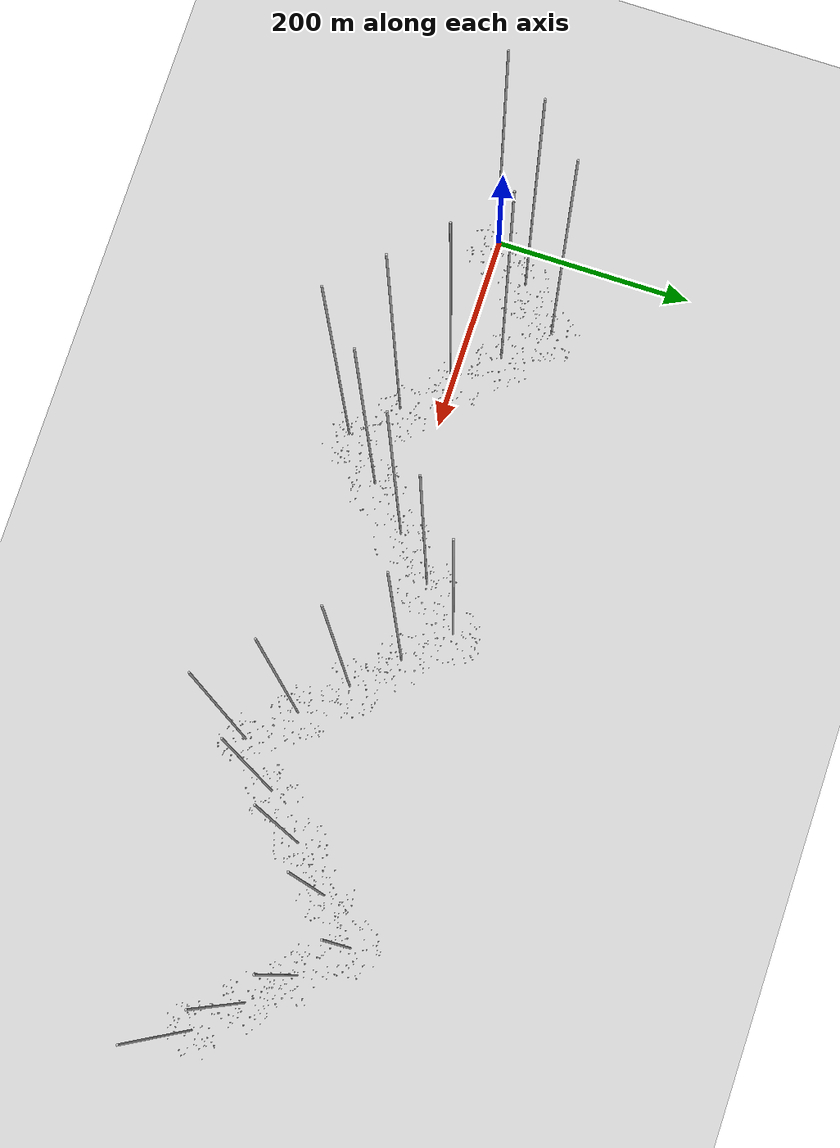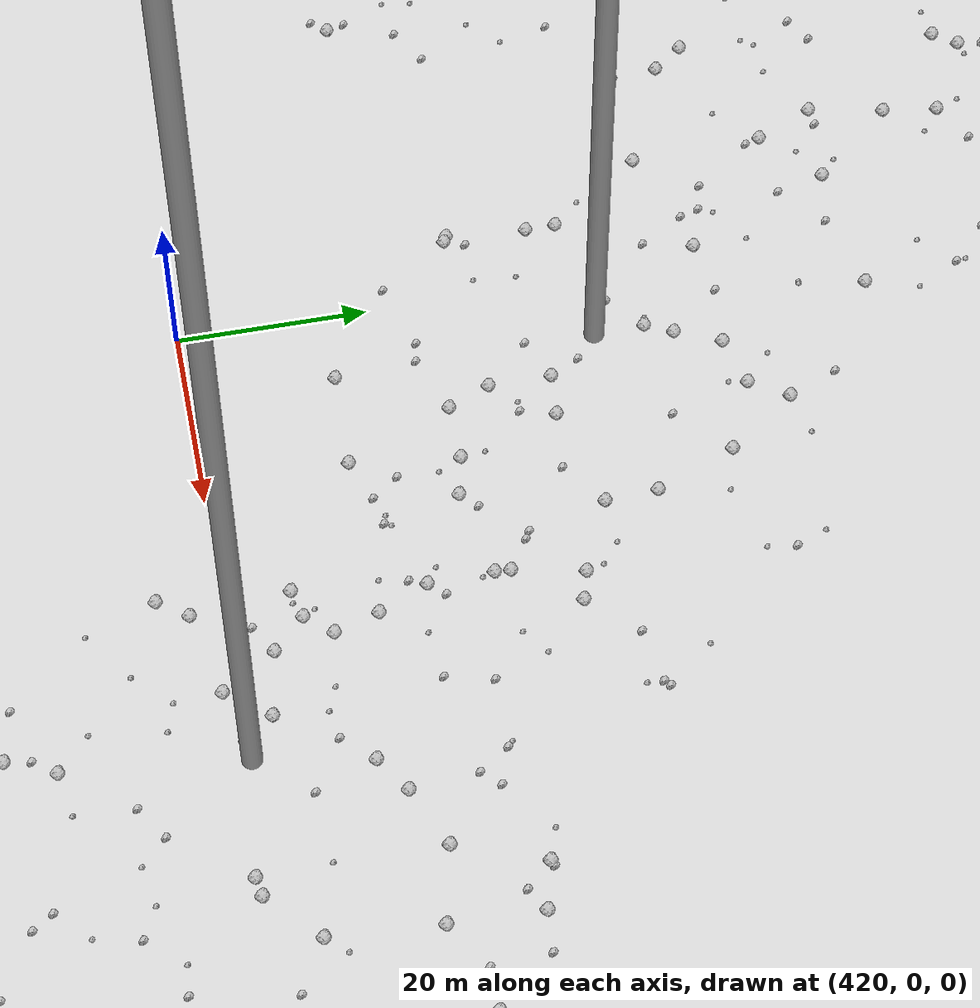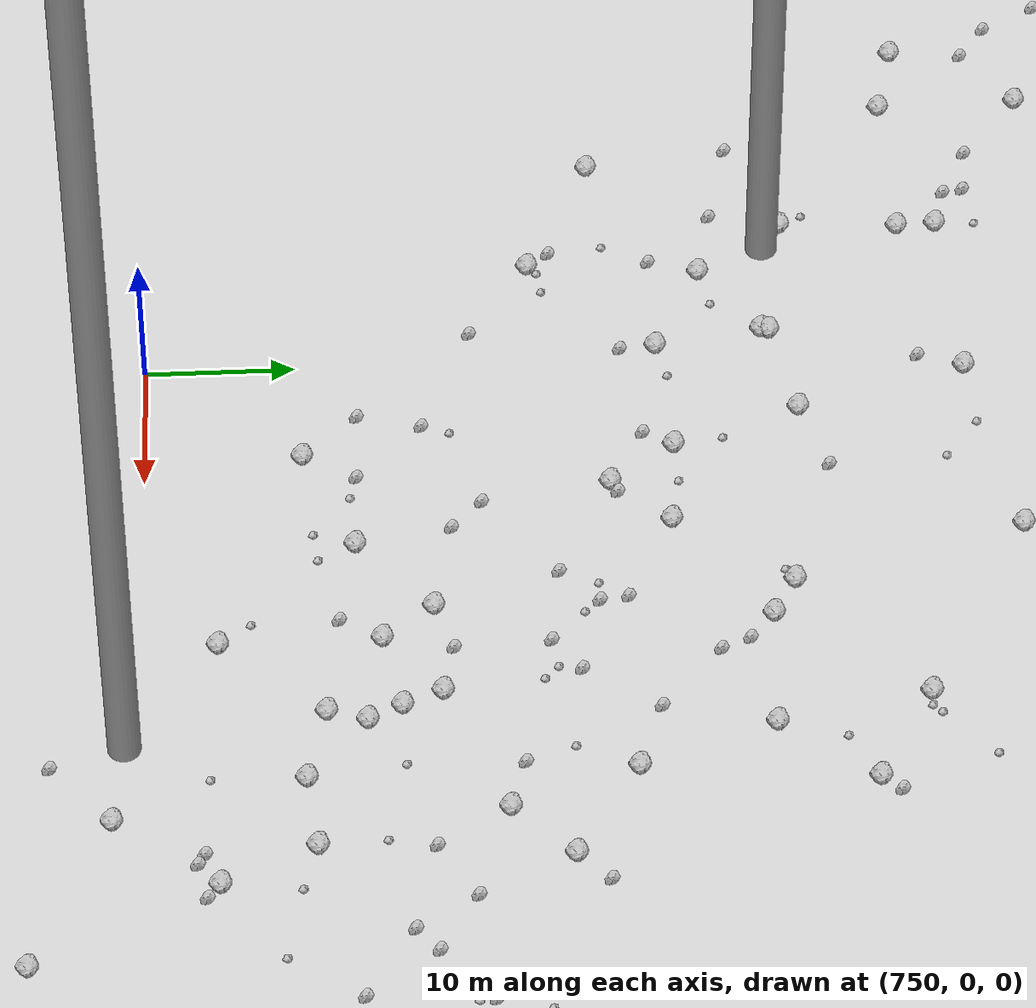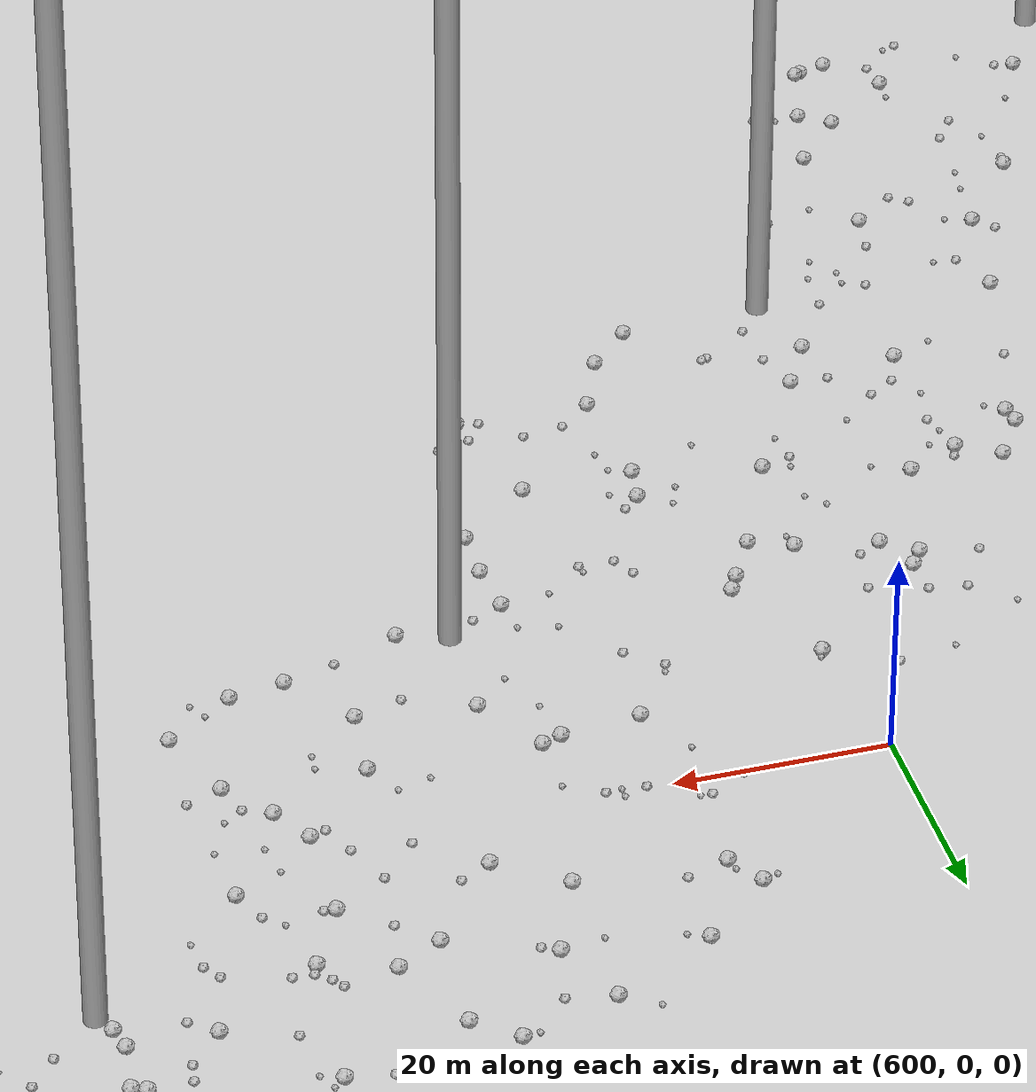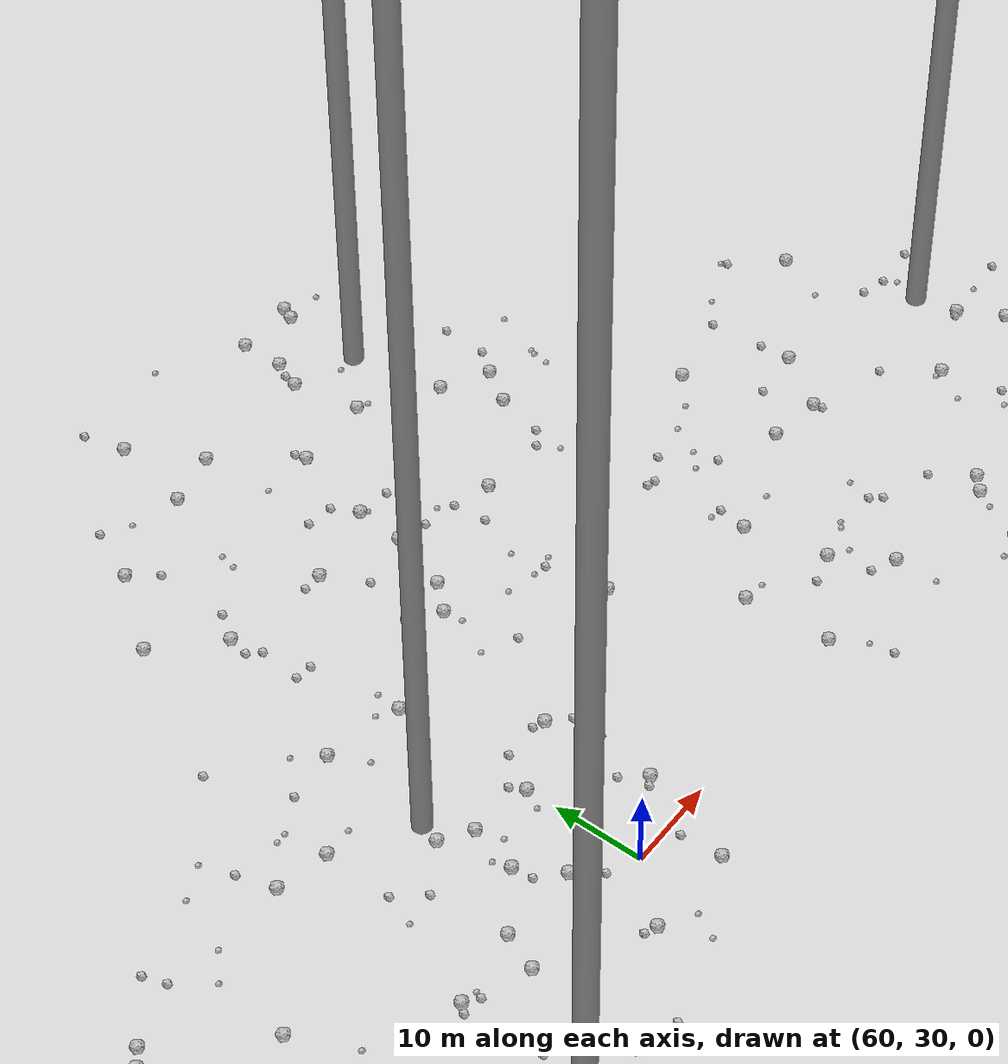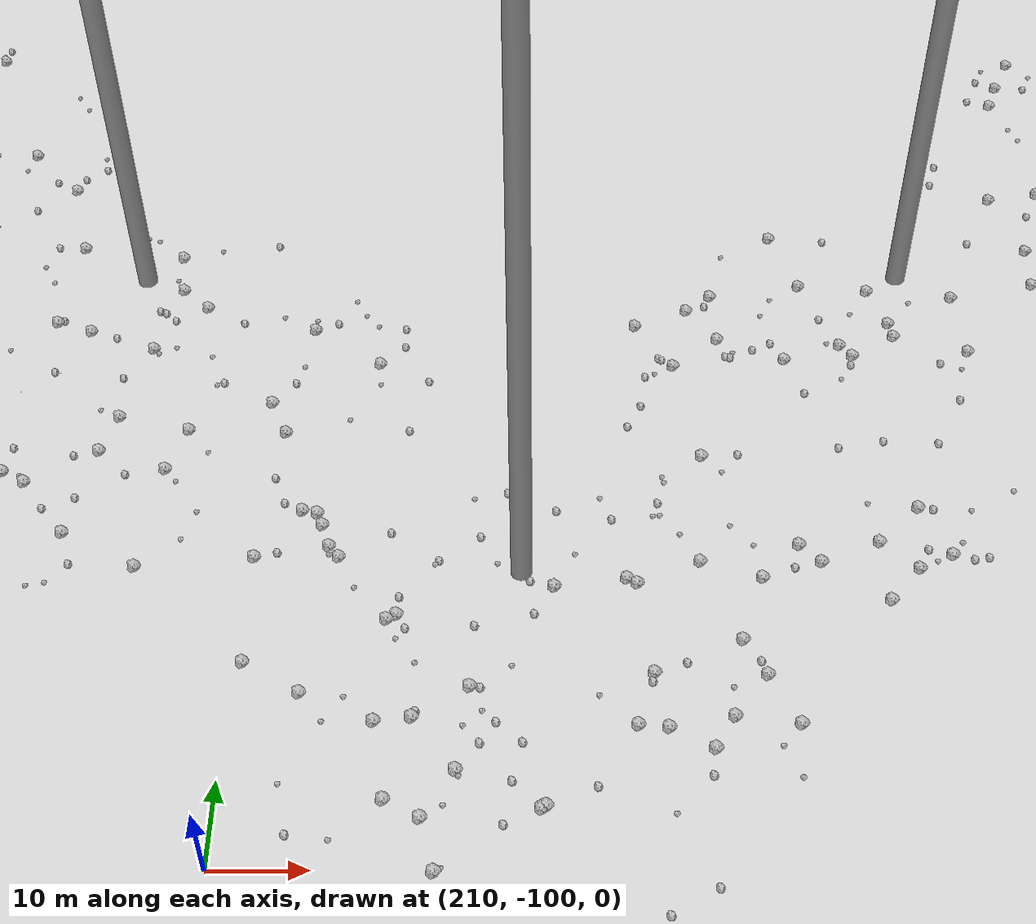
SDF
<sdf version="1.6">
 <world name="default">
  <include><uri>model://custom_ground</uri></include>
  <include><uri>model://sun</uri></include>
  <spherical_coordinates>
   <surface_model>EARTH_WGS84</surface_model>
   <latitude_deg>38.161479</latitude_deg>
   <longitude_deg>-122.454630</longitude_deg>
   <elevation>488.0</elevation>
   <heading_deg>90</heading_deg>
  </spherical_coordinates>
  <model name="rock1_0_0">
   <include><uri>model://rock1</uri><pose>-0.13717001291943376 25.787154543660918 0.5 0 0 0</pose></include>
  </model>
  <model name="rock1_0_1">
   <include><uri>model://rock1</uri><pose>4.755294397749029 17.537682692599823 0.5 0 0 0</pose></include>
  </model>
  <model name="rock1_0_2">
   <include><uri>model://rock1</uri><pose>14.438561846816263 -14.088238945821857 0.5 0 0 0</pose></include>
  </model>
  <model name="rock1_0_3">
   <include><uri>model://rock1</uri><pose>18.343334891461048 0.8101133850448186 0.5 0 0 0</pose></include>
  </model>
  <model name="rock1_0_4">
   <include><uri>model://rock1</uri><pose>7.934947623881193 29.443009117658633 0.5 0 0 0</pose></include>
  </model>
  <model name="rock1_0_5">
   <include><uri>model://rock1</uri><pose>6.005714709265444 -13.76198931600267 0.5 0 0 0</pose></include>
  </model>
  <model name="rock1_0_6">
   <include><uri>model://rock1</uri><pose>6.742528823899189 16.622186876741225 0.5 0 0 0</pose></include>
  </model>
  <model name="rock1_0_7">
   <include><uri>model://rock1</uri><pose>3.082100766277584 2.6522618058660825 0.5 0 0 0</pose></include>
  </model>
  <model name="rock1_0_8">
   <include><uri>model://rock1</uri><pose>9.127228379113777 -5.91440779899375 0.5 0 0 0</pose></include>
  </model>
  <model name="rock1_0_9">
   <include><uri>model://rock1</uri><pose>19.98494203032096 -22.07028369685764 0.5 0 0 0</pose></include>
  </model>
  <model name="rock1_0_10">
   <include><uri>model://rock1</uri><pose>24.811240526510602 -9.189557394420866 0.5 0 0 0</pose></include>
  </model>
  <model name="rock1_0_11">
   <include><uri>model://rock1</uri><pose>7.872476988000852 -11.043745803397222 0.5 0 0 0</pose></include>
  </model>
  <model name="rock1_0_12">
   <include><uri>model://rock1</uri><pose>12.601587128168205 7.579184512274907 0.5 0 0 0</pose></include>
  </model>
  <model name="rock1_0_13">
   <include><uri>model://rock1</uri><pose>17.61642601987898 -1.388534608510696 0.5 0 0 0</pose></include>
  </model>
  <model name="rock1_0_14">
   <include><uri>model://rock1</uri><pose>0.4175088909901419 -15.674244092253709 0.5 0 0 0</pose></include>
  </model>
  <model name="rock1_0_15">
   <include><uri>model://rock1</uri><pose>15.86766222540777 -22.288233859832335 0.5 0 0 0</pose></include>
  </model>
  <model name="rock1_0_16">
   <include><uri>model://rock1</uri><pose>26.712938988913102 15.159791982546686 0.5 0 0 0</pose></include>
  </model>
  <model name="rock1_0_17">
   <include><uri>model://rock1</uri><pose>13.399954540065664 -24.73991786673274 0.5 0 0 0</pose></include>
  </model>
  <model name="rock1_0_18">
   <include><uri>model://rock1</uri><pose>17.841486683517367 3.8988279427927566 0.5 0 0 0</pose></include>
  </model>
  <model name="rock1_0_19">
   <include><uri>model://rock1</uri><pose>-9.06617865886642 -14.71626676128436 0.5 0 0 0</pose></include>
  </model>
  <model name="rock1_0_20">
   <include><uri>model://rock1</uri><pose>-7.199097823117505 -20.317903175617555 0.5 0 0 0</pose></include>
  </model>
  <model name="rock1_0_21">
   <include><uri>model://rock1</uri><pose>28.329822835398595 -22.413514123052458 0.5 0 0 0</pose></include>
  </model>
  <model name="rock1_0_22">
   <include><uri>model://rock1</uri><pose>7.1317383234388885 19.758631122728573 0.5 0 0 0</pose></include>
  </model>
  <model name="rock1_0_23">
   <include><uri>model://rock1</uri><pose>-1.9601667741429623 4.525267203646457 0.5 0 0 0</pose></include>
  </model>
  <model name="rock1_0_24">
   <include><uri>model://rock1</uri><pose>37.107611091518855 -6.110001650317422 0.5 0 0 0</pose></include>
  </model>
  <model name="rock1_0_25">
   <include><uri>model://rock1</uri><pose>-5.1066198707219925 -24.76074350758809 0.5 0 0 0</pose></include>
  </model>
  <model name="rock1_0_26">
   <include><uri>model://rock1</uri><pose>31.873386687712788 3.7615670159366275 0.5 0 0 0</pose></include>
  </model>
  <model name="rock2_0_0">
   <include><uri>model://rock2</uri><pose>-15.505533679320898 -4.191615136256125 0.3 0 0 0</pose></include>
  </model>
  <model name="rock2_0_1">
   <include><uri>model://rock2</uri><pose>15.664136243920538 29.156066775808462 0.3 0 0 0</pose></include>
  </model>
  <model name="rock2_0_2">
   <include><uri>model://rock2</uri><pose>24.83080728630417 -10.860275217173086 0.3 0 0 0</pose></include>
  </model>
  <model name="rock2_0_3">
   <include><uri>model://rock2</uri><pose>11.888701404437157 26.08027218640691 0.3 0 0 0</pose></include>
  </model>
  <model name="rock2_0_4">
   <include><uri>model://rock2</uri><pose>-3.441075141844351 2.9077247807568725 0.3 0 0 0</pose></include>
  </model>
  <model name="rock2_0_5">
   <include><uri>model://rock2</uri><pose>-5.1742602773557085 1.6482350600616194 0.3 0 0 0</pose></include>
  </model>
  <model name="rock2_0_6">
   <include><uri>model://rock2</uri><pose>22.09416843919969 -1.9194810866440513 0.3 0 0 0</pose></include>
  </model>
  <model name="rock2_0_7">
   <include><uri>model://rock2</uri><pose>-1.7261564692264777 -15.651298210043453 0.3 0 0 0</pose></include>
  </model>
  <model name="rock2_0_8">
   <include><uri>model://rock2</uri><pose>18.810477787363226 3.952699722879295 0.3 0 0 0</pose></include>
  </model>
  <model name="rock2_0_9">
   <include><uri>model://rock2</uri><pose>4.8237271269217175 -12.893000180496863 0.3 0 0 0</pose></include>
  </model>
  <model name="rock2_0_10">
   <include><uri>model://rock2</uri><pose>33.85915778559707 5.227087870460387 0.3 0 0 0</pose></include>
  </model>
  <model name="rock2_0_11">
   <include><uri>model://rock2</uri><pose>-9.158188849551571 -9.604825247174823 0.3 0 0 0</pose></include>
  </model>
  <model name="rock2_0_12">
   <include><uri>model://rock2</uri><pose>24.746320326775454 4.7264321363283415 0.3 0 0 0</pose></include>
  </model>
  <model name="rock2_0_13">
   <include><uri>model://rock2</uri><pose>25.593575124300436 13.959871537229454 0.3 0 0 0</pose></include>
  </model>
  <model name="rock2_0_14">
   <include><uri>model://rock2</uri><pose>-3.6651809263949247 -8.7746673910484 0.3 0 0 0</pose></include>
  </model>
  <model name="rock2_0_15">
   <include><uri>model://rock2</uri><pose>-7.056426561365296 -21.63155775140372 0.3 0 0 0</pose></include>
  </model>
  <model name="rock2_0_16">
   <include><uri>model://rock2</uri><pose>-2.557756205376453 10.60147358255351 0.3 0 0 0</pose></include>
  </model>
  <model name="rock2_0_17">
   <include><uri>model://rock2</uri><pose>-14.983702069043488 -14.078534943867325 0.3 0 0 0</pose></include>
  </model>
  <model name="rock2_0_18">
   <include><uri>model://rock2</uri><pose>33.404064493828024 8.494527970908209 0.3 0 0 0</pose></include>
  </model>
  <model name="rock2_0_19">
   <include><uri>model://rock2</uri><pose>7.22022324230435 -9.043388758126007 0.3 0 0 0</pose></include>
  </model>
  <model name="rock2_0_20">
   <include><uri>model://rock2</uri><pose>16.8429033490402 -11.51908300537459 0.3 0 0 0</pose></include>
  </model>
  <model name="rock2_0_21">
   <include><uri>model://rock2</uri><pose>10.154396560830591 5.790304456932901 0.3 0 0 0</pose></include>
  </model>
  <model name="rock2_0_22">
   <include><uri>model://rock2</uri><pose>34.792454512386506 -5.523801355680217 0.3 0 0 0</pose></include>
  </model>
  <model name="rock2_0_23">
   <include><uri>model://rock2</uri><pose>11.30826156618097 -4.278075563324979 0.3 0 0 0</pose></include>
  </model>
  <model name="rock2_0_24">
   <include><uri>model://rock2</uri><pose>10.545027435177538 2.2303641010759208 0.3 0 0 0</pose></include>
  </model>
  <model name="rock2_0_25">
   <include><uri>model://rock2</uri><pose>18.183104315695147 -28.235213348727687 0.3 0 0 0</pose></include>
  </model>
  <model name="rock2_0_26">
   <include><uri>model://rock2</uri><pose>27.465588843426367 -22.727763470628506 0.3 0 0 0</pose></include>
  </model>
  <model name="rock3_0_0">
   <include><uri>model://rock3</uri><pose>15.487844069862561 20.854846258581567 0.2 0 0 0</pose></include>
  </model>
  <model name="rock3_0_1">
   <include><uri>model://rock3</uri><pose>-8.066230140236584 -23.26952898099539 0.2 0 0 0</pose></include>
  </model>
  <model name="rock3_0_2">
   <include><uri>model://rock3</uri><pose>5.932372791855535 -3.139069074772884 0.2 0 0 0</pose></include>
  </model>
  <model name="rock3_0_3">
   <include><uri>model://rock3</uri><pose>-15.98691062097917 -9.142206645270488 0.2 0 0 0</pose></include>
  </model>
  <model name="rock3_0_4">
   <include><uri>model://rock3</uri><pose>12.25000197345905 4.086588101150674 0.2 0 0 0</pose></include>
  </model>
  <model name="rock3_0_5">
   <include><uri>model://rock3</uri><pose>10.43956074592272 -4.778884660912098 0.2 0 0 0</pose></include>
  </model>
  <model name="rock3_0_6">
   <include><uri>model://rock3</uri><pose>3.2538648692890106 12.45356676171648 0.2 0 0 0</pose></include>
  </model>
  <model name="rock3_0_7">
   <include><uri>model://rock3</uri><pose>27.234893838302547 -3.8115623460461947 0.2 0 0 0</pose></include>
  </model>
  <model name="rock3_0_8">
   <include><uri>model://rock3</uri><pose>17.144603735362182 -23.267474388527987 0.2 0 0 0</pose></include>
  </model>
  <model name="rock3_0_9">
   <include><uri>model://rock3</uri><pose>14.898834381864674 -0.8614510669448947 0.2 0 0 0</pose></include>
  </model>
  <model name="rock3_0_10">
   <include><uri>model://rock3</uri><pose>20.85345015404593 1.2873101796112891 0.2 0 0 0</pose></include>
  </model>
  <model name="rock3_0_11">
   <include><uri>model://rock3</uri><pose>18.95676849258794 -3.0279579448304474 0.2 0 0 0</pose></include>
  </model>
  <model name="rock3_0_12">
   <include><uri>model://rock3</uri><pose>-5.990392371813037 -6.0257033381111285 0.2 0 0 0</pose></include>
  </model>
  <model name="rock3_0_13">
   <include><uri>model://rock3</uri><pose>-8.389499141703096 -8.695819333944993 0.2 0 0 0</pose></include>
  </model>
  <model name="rock3_0_14">
   <include><uri>model://rock3</uri><pose>-1.3312696448307477 -26.725218350943468 0.2 0 0 0</pose></include>
  </model>
  <model name="rock3_0_15">
   <include><uri>model://rock3</uri><pose>12.8793686960353 -25.98012282919061 0.2 0 0 0</pose></include>
  </model>
  <model name="rock3_0_16">
   <include><uri>model://rock3</uri><pose>10.63190867702086 7.677399371812882 0.2 0 0 0</pose></include>
  </model>
  <model name="rock3_0_17">
   <include><uri>model://rock3</uri><pose>8.773986495483609 -21.14648841953849 0.2 0 0 0</pose></include>
  </model>
  <model name="rock3_0_18">
   <include><uri>model://rock3</uri><pose>-7.200519934584504 2.076336080617878 0.2 0 0 0</pose></include>
  </model>
  <model name="rock3_0_19">
   <include><uri>model://rock3</uri><pose>23.06161502410209 -26.98256478762666 0.2 0 0 0</pose></include>
  </model>
  <model name="rock3_0_20">
   <include><uri>model://rock3</uri><pose>-15.197779873212111 13.489364984868736 0.2 0 0 0</pose></include>
  </model>
  <model name="rock3_0_21">
   <include><uri>model://rock3</uri><pose>36.515777992466845 -7.592490453515651 0.2 0 0 0</pose></include>
  </model>
  <model name="rock3_0_22">
   <include><uri>model://rock3</uri><pose>24.964432495781907 -17.912921524379378 0.2 0 0 0</pose></include>
  </model>
  <model name="rock3_0_23">
   <include><uri>model://rock3</uri><pose>10.013068781697882 2.04366345565375 0.2 0 0 0</pose></include>
  </model>
  <model name="rock3_0_24">
   <include><uri>model://rock3</uri><pose>8.75638242068326 -4.4908168960194885 0.2 0 0 0</pose></include>
  </model>
  <model name="rock3_0_25">
   <include><uri>model://rock3</uri><pose>16.324807333512496 14.034982565989502 0.2 0 0 0</pose></include>
  </model>
  <model name="rock3_0_26">
   <include><uri>model://rock3</uri><pose>-17.275398737585256 -4.579955712274554 0.2 0 0 0</pose></include>
  </model>
  <model name="rock1_1_0">
   <include><uri>model://rock1</uri><pose>45.55258266848267 34.77889553607032 0.5 0 0 0</pose></include>
  </model>
  <model name="rock1_1_1">
   <include><uri>model://rock1</uri><pose>51.73630597369085 39.05026022234132 0.5 0 0 0</pose></include>
  </model>
  <model name="rock1_1_2">
   <include><uri>model://rock1</uri><pose>15.47447588088736 54.43507939025542 0.5 0 0 0</pose></include>
  </model>
  <model name="rock1_1_3">
   <include><uri>model://rock1</uri><pose>54.49477960420282 34.38815743683681 0.5 0 0 0</pose></include>
  </model>
  <model name="rock1_1_4">
   <include><uri>model://rock1</uri><pose>33.90942909422158 14.395877958456325 0.5 0 0 0</pose></include>
  </model>
  <model name="rock1_1_5">
   <include><uri>model://rock1</uri><pose>18.15003278893964 35.99577690287157 0.5 0 0 0</pose></include>
  </model>
  <model name="rock1_1_6">
   <include><uri>model://rock1</uri><pose>49.88557759409116 46.6100395372739 0.5 0 0 0</pose></include>
  </model>
  <model name="rock1_1_7">
   <include><uri>model://rock1</uri><pose>54.68225582907178 24.127790943672828 0.5 0 0 0</pose></include>
  </model>
  <model name="rock1_1_8">
   <include><uri>model://rock1</uri><pose>68.27837523983104 34.81964194122463 0.5 0 0 0</pose></include>
  </model>
  <model name="rock1_1_9">
   <include><uri>model://rock1</uri><pose>59.7781675955145 43.34950680349461 0.5 0 0 0</pose></include>
  </model>
  <model name="rock1_1_10">
   <include><uri>model://rock1</uri><pose>12.297138220239248 39.897392149340675 0.5 0 0 0</pose></include>
  </model>
  <model name="rock1_1_11">
   <include><uri>model://rock1</uri><pose>36.57702703909166 55.31514145252223 0.5 0 0 0</pose></include>
  </model>
  <model name="rock1_1_12">
   <include><uri>model://rock1</uri><pose>21.359918092771302 18.570470406299123 0.5 0 0 0</pose></include>
  </model>
  <model name="rock1_1_13">
   <include><uri>model://rock1</uri><pose>42.431362751952925 54.00353779554088 0.5 0 0 0</pose></include>
  </model>
  <model name="rock1_1_14">
   <include><uri>model://rock1</uri><pose>53.09091663960263 44.44276289270666 0.5 0 0 0</pose></include>
  </model>
  <model name="rock1_1_15">
   <include><uri>model://rock1</uri><pose>24.809961088213846 35.50181838239283 0.5 0 0 0</pose></include>
  </model>
  <model name="rock1_1_16">
   <include><uri>model://rock1</uri><pose>43.903095663852675 30.706785908392614 0.5 0 0 0</pose></include>
  </model>
  <model name="rock1_1_17">
   <include><uri>model://rock1</uri><pose>40.78481409477696 12.226887849661466 0.5 0 0 0</pose></include>
  </model>
  <model name="rock1_1_18">
   <include><uri>model://rock1</uri><pose>29.24077382657228 18.968516881097955 0.5 0 0 0</pose></include>
  </model>
  <model name="rock1_1_19">
   <include><uri>model://rock1</uri><pose>64.78614778818684 23.88343544185287 0.5 0 0 0</pose></include>
  </model>
  <model name="rock1_1_20">
   <include><uri>model://rock1</uri><pose>14.332843373043504 26.050699589935768 0.5 0 0 0</pose></include>
  </model>
  <model name="rock1_1_21">
   <include><uri>model://rock1</uri><pose>51.39545583141105 61.23737167869599 0.5 0 0 0</pose></include>
  </model>
  <model name="rock1_1_22">
   <include><uri>model://rock1</uri><pose>37.030448643221995 33.659427228384295 0.5 0 0 0</pose></include>
  </model>
  <model name="rock1_1_23">
   <include><uri>model://rock1</uri><pose>24.496441931905387 44.588959569295405 0.5 0 0 0</pose></include>
  </model>
  <model name="rock1_1_24">
   <include><uri>model://rock1</uri><pose>13.749135162061483 53.05707131124527 0.5 0 0 0</pose></include>
  </model>
  <model name="rock1_1_25">
   <include><uri>model://rock1</uri><pose>67.3403467713135 46.85825383203224 0.5 0 0 0</pose></include>
  </model>
  <model name="rock1_1_26">
   <include><uri>model://rock1</uri><pose>60.01142392579244 59.178410918405625 0.5 0 0 0</pose></include>
  </model>
  <model name="rock2_1_0">
   <include><uri>model://rock2</uri><pose>66.0648578299654 47.443321887049166 0.3 0 0 0</pose></include>
  </model>
  <model name="rock2_1_1">
   <include><uri>model://rock2</uri><pose>36.23072920107947 32.81709410494782 0.3 0 0 0</pose></include>
  </model>
  <model name="rock2_1_2">
   <include><uri>model://rock2</uri><pose>67.25166029662533 34.249414654080404 0.3 0 0 0</pose></include>
  </model>
  <model name="rock2_1_3">
   <include><uri>model://rock2</uri><pose>17.248296060775722 31.587895263013483 0.3 0 0 0</pose></include>
  </model>
  <model name="rock2_1_4">
   <include><uri>model://rock2</uri><pose>56.61088949733275 31.582624968779715 0.3 0 0 0</pose></include>
  </model>
  <model name="rock2_1_5">
   <include><uri>model://rock2</uri><pose>47.3270140313262 16.564533235891286 0.3 0 0 0</pose></include>
  </model>
  <model name="rock2_1_6">
   <include><uri>model://rock2</uri><pose>69.31870614990785 41.526900140396535 0.3 0 0 0</pose></include>
  </model>
  <model name="rock2_1_7">
   <include><uri>model://rock2</uri><pose>52.005840594429465 36.7984049578611 0.3 0 0 0</pose></include>
  </model>
  <model name="rock2_1_8">
   <include><uri>model://rock2</uri><pose>42.290134929616194 69.35017522676753 0.3 0 0 0</pose></include>
  </model>
  <model name="rock2_1_9">
   <include><uri>model://rock2</uri><pose>22.31039640800588 56.76116730941329 0.3 0 0 0</pose></include>
  </model>
  <model name="rock2_1_10">
   <include><uri>model://rock2</uri><pose>45.685518930515535 60.76645457024678 0.3 0 0 0</pose></include>
  </model>
  <model name="rock2_1_11">
   <include><uri>model://rock2</uri><pose>44.66319651453999 43.37013715201766 0.3 0 0 0</pose></include>
  </model>
  <model name="rock2_1_12">
   <include><uri>model://rock2</uri><pose>42.16247031407833 46.338540329346294 0.3 0 0 0</pose></include>
  </model>
  <model name="rock2_1_13">
   <include><uri>model://rock2</uri><pose>58.97413989914958 44.997596435827305 0.3 0 0 0</pose></include>
  </model>
  <model name="rock2_1_14">
   <include><uri>model://rock2</uri><pose>37.14847699174116 24.392177362389177 0.3 0 0 0</pose></include>
  </model>
  <model name="rock2_1_15">
   <include><uri>model://rock2</uri><pose>69.35518207888768 44.96902634526827 0.3 0 0 0</pose></include>
  </model>
  <model name="rock2_1_16">
   <include><uri>model://rock2</uri><pose>66.2326263754149 37.31627940649189 0.3 0 0 0</pose></include>
  </model>
  <model name="rock2_1_17">
   <include><uri>model://rock2</uri><pose>38.52831076676693 32.5992997174417 0.3 0 0 0</pose></include>
  </model>
  <model name="rock2_1_18">
   <include><uri>model://rock2</uri><pose>62.030350401322174 47.276706756799406 0.3 0 0 0</pose></include>
  </model>
  <model name="rock2_1_19">
   <include><uri>model://rock2</uri><pose>64.4095693236441 28.48657356358062 0.3 0 0 0</pose></include>
  </model>
  <model name="rock2_1_20">
   <include><uri>model://rock2</uri><pose>11.836993941749023 33.21663505032206 0.3 0 0 0</pose></include>
  </model>
  <model name="rock2_1_21">
   <include><uri>model://rock2</uri><pose>57.57163818883914 55.3557036175545 0.3 0 0 0</pose></include>
  </model>
  <model name="rock2_1_22">
   <include><uri>model://rock2</uri><pose>35.34783412415478 59.51176985872065 0.3 0 0 0</pose></include>
  </model>
  <model name="rock2_1_23">
   <include><uri>model://rock2</uri><pose>21.794382335269496 27.564260927502573 0.3 0 0 0</pose></include>
  </model>
  <model name="rock2_1_24">
   <include><uri>model://rock2</uri><pose>53.314187557135625 24.705779910082256 0.3 0 0 0</pose></include>
  </model>
  <model name="rock2_1_25">
   <include><uri>model://rock2</uri><pose>21.51186297323065 59.22444095820904 0.3 0 0 0</pose></include>
  </model>
  <model name="rock2_1_26">
   <include><uri>model://rock2</uri><pose>17.65178523495088 26.00483483568064 0.3 0 0 0</pose></include>
  </model>
  <model name="rock3_1_0">
   <include><uri>model://rock3</uri><pose>24.397347314786686 27.34658014530144 0.2 0 0 0</pose></include>
  </model>
  <model name="rock3_1_1">
   <include><uri>model://rock3</uri><pose>60.14267034141315 61.96852630685089 0.2 0 0 0</pose></include>
  </model>
  <model name="rock3_1_2">
   <include><uri>model://rock3</uri><pose>58.16443318360488 21.9350860596401 0.2 0 0 0</pose></include>
  </model>
  <model name="rock3_1_3">
   <include><uri>model://rock3</uri><pose>40.98705543665719 42.86782004302439 0.2 0 0 0</pose></include>
  </model>
  <model name="rock3_1_4">
   <include><uri>model://rock3</uri><pose>11.144654381214343 42.45707017319161 0.2 0 0 0</pose></include>
  </model>
  <model name="rock3_1_5">
   <include><uri>model://rock3</uri><pose>49.02698599191754 63.994875978083286 0.2 0 0 0</pose></include>
  </model>
  <model name="rock3_1_6">
   <include><uri>model://rock3</uri><pose>24.62380313391173 32.24355742482582 0.2 0 0 0</pose></include>
  </model>
  <model name="rock3_1_7">
   <include><uri>model://rock3</uri><pose>40.65160272498032 58.708445531979166 0.2 0 0 0</pose></include>
  </model>
  <model name="rock3_1_8">
   <include><uri>model://rock3</uri><pose>36.419990455018805 17.414819918031057 0.2 0 0 0</pose></include>
  </model>
  <model name="rock3_1_9">
   <include><uri>model://rock3</uri><pose>42.40986032271867 17.69426340403048 0.2 0 0 0</pose></include>
  </model>
  <model name="rock3_1_10">
   <include><uri>model://rock3</uri><pose>30.394094211787703 61.330243359778144 0.2 0 0 0</pose></include>
  </model>
  <model name="rock3_1_11">
   <include><uri>model://rock3</uri><pose>38.83312688970721 33.3226624533975 0.2 0 0 0</pose></include>
  </model>
  <model name="rock3_1_12">
   <include><uri>model://rock3</uri><pose>53.344302269992596 57.41934648225475 0.2 0 0 0</pose></include>
  </model>
  <model name="rock3_1_13">
   <include><uri>model://rock3</uri><pose>18.03385990948813 40.00656819980307 0.2 0 0 0</pose></include>
  </model>
  <model name="rock3_1_14">
   <include><uri>model://rock3</uri><pose>27.550145788393177 37.866776591270764 0.2 0 0 0</pose></include>
  </model>
  <model name="rock3_1_15">
   <include><uri>model://rock3</uri><pose>34.14139338635481 63.003558624983405 0.2 0 0 0</pose></include>
  </model>
  <model name="rock3_1_16">
   <include><uri>model://rock3</uri><pose>25.208939407433768 52.94275721130521 0.2 0 0 0</pose></include>
  </model>
  <model name="rock3_1_17">
   <include><uri>model://rock3</uri><pose>12.069746105694412 31.24371708360486 0.2 0 0 0</pose></include>
  </model>
  <model name="rock3_1_18">
   <include><uri>model://rock3</uri><pose>56.7568457040128 19.268225514269922 0.2 0 0 0</pose></include>
  </model>
  <model name="rock3_1_19">
   <include><uri>model://rock3</uri><pose>20.69934328754959 22.389749103125283 0.2 0 0 0</pose></include>
  </model>
  <model name="rock3_1_20">
   <include><uri>model://rock3</uri><pose>41.839011808980544 58.745510761734025 0.2 0 0 0</pose></include>
  </model>
  <model name="rock3_1_21">
   <include><uri>model://rock3</uri><pose>36.07324906142658 19.38375361487397 0.2 0 0 0</pose></include>
  </model>
  <model name="rock3_1_22">
   <include><uri>model://rock3</uri><pose>51.18466150935942 40.97169919770529 0.2 0 0 0</pose></include>
  </model>
  <model name="rock3_1_23">
   <include><uri>model://rock3</uri><pose>58.69485228974764 41.28680427172051 0.2 0 0 0</pose></include>
  </model>
  <model name="rock3_1_24">
   <include><uri>model://rock3</uri><pose>53.96687105300779 41.67304930439509 0.2 0 0 0</pose></include>
  </model>
  <model name="rock3_1_25">
   <include><uri>model://rock3</uri><pose>45.79192926495005 54.11254699947239 0.2 0 0 0</pose></include>
  </model>
  <model name="rock3_1_26">
   <include><uri>model://rock3</uri><pose>27.995173212708593 55.352905213760565 0.2 0 0 0</pose></include>
  </model>
  <model name="rock1_2_0">
   <include><uri>model://rock1</uri><pose>98.05241247324965 75.3827248007902 0.5 0 0 0</pose></include>
  </model>
  <model name="rock1_2_1">
   <include><uri>model://rock1</uri><pose>88.04478143431916 86.95321251007533 0.5 0 0 0</pose></include>
  </model>
  <model name="rock1_2_2">
   <include><uri>model://rock1</uri><pose>95.59855750793145 86.14958774133609 0.5 0 0 0</pose></include>
  </model>
  <model name="rock1_2_3">
   <include><uri>model://rock1</uri><pose>87.83597735504607 97.30873567272914 0.5 0 0 0</pose></include>
  </model>
  <model name="rock1_2_4">
   <include><uri>model://rock1</uri><pose>56.68801266138935 77.87107888184204 0.5 0 0 0</pose></include>
  </model>
  <model name="rock1_2_5">
   <include><uri>model://rock1</uri><pose>56.48582041002379 91.56694956544675 0.5 0 0 0</pose></include>
  </model>
  <model name="rock1_2_6">
   <include><uri>model://rock1</uri><pose>67.28977345381905 93.84529915279514 0.5 0 0 0</pose></include>
  </model>
  <model name="rock1_2_7">
   <include><uri>model://rock1</uri><pose>60.58519141260925 57.726266071521835 0.5 0 0 0</pose></include>
  </model>
  <model name="rock1_2_8">
   <include><uri>model://rock1</uri><pose>76.82192999460287 72.53744719247493 0.5 0 0 0</pose></include>
  </model>
  <model name="rock1_2_9">
   <include><uri>model://rock1</uri><pose>87.75459053086836 101.91033171500307 0.5 0 0 0</pose></include>
  </model>
  <model name="rock1_2_10">
   <include><uri>model://rock1</uri><pose>79.48630348367398 86.78875956587248 0.5 0 0 0</pose></include>
  </model>
  <model name="rock1_2_11">
   <include><uri>model://rock1</uri><pose>74.67077790998624 65.87989196317233 0.5 0 0 0</pose></include>
  </model>
  <model name="rock1_2_12">
   <include><uri>model://rock1</uri><pose>72.15550270729076 63.10857396123264 0.5 0 0 0</pose></include>
  </model>
  <model name="rock1_2_13">
   <include><uri>model://rock1</uri><pose>50.53208092365196 83.94159086374658 0.5 0 0 0</pose></include>
  </model>
  <model name="rock1_2_14">
   <include><uri>model://rock1</uri><pose>107.07852695048851 70.26118599352796 0.5 0 0 0</pose></include>
  </model>
  <model name="rock1_2_15">
   <include><uri>model://rock1</uri><pose>77.18243252233893 77.83996227037595 0.5 0 0 0</pose></include>
  </model>
  <model name="rock1_2_16">
   <include><uri>model://rock1</uri><pose>94.28535940739403 101.95408761910682 0.5 0 0 0</pose></include>
  </model>
  <model name="rock1_2_17">
   <include><uri>model://rock1</uri><pose>84.30678774116784 51.74792294538359 0.5 0 0 0</pose></include>
  </model>
  <model name="rock1_2_18">
   <include><uri>model://rock1</uri><pose>86.63037658007947 94.21364355766602 0.5 0 0 0</pose></include>
  </model>
  <model name="rock1_2_19">
   <include><uri>model://rock1</uri><pose>104.66461314885828 68.12817373455046 0.5 0 0 0</pose></include>
  </model>
  <model name="rock1_2_20">
   <include><uri>model://rock1</uri><pose>68.25685805206221 75.92837788648093 0.5 0 0 0</pose></include>
  </model>
  <model name="rock1_2_21">
   <include><uri>model://rock1</uri><pose>87.82676848442262 69.48789394651929 0.5 0 0 0</pose></include>
  </model>
  <model name="rock1_2_22">
   <include><uri>model://rock1</uri><pose>93.72215156564086 100.59955460137253 0.5 0 0 0</pose></include>
  </model>
  <model name="rock1_2_23">
   <include><uri>model://rock1</uri><pose>73.19750802810779 95.00796948002636 0.5 0 0 0</pose></include>
  </model>
  <model name="rock1_2_24">
   <include><uri>model://rock1</uri><pose>95.48930995540748 81.72607696047888 0.5 0 0 0</pose></include>
  </model>
  <model name="rock1_2_25">
   <include><uri>model://rock1</uri><pose>100.32121321871048 78.92861635055215 0.5 0 0 0</pose></include>
  </model>
  <model name="rock1_2_26">
   <include><uri>model://rock1</uri><pose>69.07371915066261 102.63496338028088 0.5 0 0 0</pose></include>
  </model>
  <model name="rock2_2_0">
   <include><uri>model://rock2</uri><pose>79.16929954975484 88.13014387574583 0.3 0 0 0</pose></include>
  </model>
  <model name="rock2_2_1">
   <include><uri>model://rock2</uri><pose>75.75300554170092 80.66925719841753 0.3 0 0 0</pose></include>
  </model>
  <model name="rock2_2_2">
   <include><uri>model://rock2</uri><pose>95.14866605849929 68.93773717896389 0.3 0 0 0</pose></include>
  </model>
  <model name="rock2_2_3">
   <include><uri>model://rock2</uri><pose>86.94115502720251 95.8072534975331 0.3 0 0 0</pose></include>
  </model>
  <model name="rock2_2_4">
   <include><uri>model://rock2</uri><pose>102.09930989683698 81.37401723027946 0.3 0 0 0</pose></include>
  </model>
  <model name="rock2_2_5">
   <include><uri>model://rock2</uri><pose>72.83638555877087 81.12419409245095 0.3 0 0 0</pose></include>
  </model>
  <model name="rock2_2_6">
   <include><uri>model://rock2</uri><pose>102.20785227352634 86.23004396744551 0.3 0 0 0</pose></include>
  </model>
  <model name="rock2_2_7">
   <include><uri>model://rock2</uri><pose>97.73216728635789 56.56607317637865 0.3 0 0 0</pose></include>
  </model>
  <model name="rock2_2_8">
   <include><uri>model://rock2</uri><pose>58.73279406529555 88.77518658513281 0.3 0 0 0</pose></include>
  </model>
  <model name="rock2_2_9">
   <include><uri>model://rock2</uri><pose>84.04868689762421 67.08322437290948 0.3 0 0 0</pose></include>
  </model>
  <model name="rock2_2_10">
   <include><uri>model://rock2</uri><pose>70.68140157246543 71.34487218784687 0.3 0 0 0</pose></include>
  </model>
  <model name="rock2_2_11">
   <include><uri>model://rock2</uri><pose>67.94015037807749 107.19182032421622 0.3 0 0 0</pose></include>
  </model>
  <model name="rock2_2_12">
   <include><uri>model://rock2</uri><pose>66.07692261142711 76.07278267042226 0.3 0 0 0</pose></include>
  </model>
  <model name="rock2_2_13">
   <include><uri>model://rock2</uri><pose>69.02837163997455 65.64618448910781 0.3 0 0 0</pose></include>
  </model>
  <model name="rock2_2_14">
   <include><uri>model://rock2</uri><pose>56.90089372860568 69.68451298350728 0.3 0 0 0</pose></include>
  </model>
  <model name="rock2_2_15">
   <include><uri>model://rock2</uri><pose>56.1962069251443 75.65177468819232 0.3 0 0 0</pose></include>
  </model>
  <model name="rock2_2_16">
   <include><uri>model://rock2</uri><pose>96.81050719538699 70.23663928029548 0.3 0 0 0</pose></include>
  </model>
  <model name="rock2_2_17">
   <include><uri>model://rock2</uri><pose>58.58449902309009 80.64435314109369 0.3 0 0 0</pose></include>
  </model>
  <model name="rock2_2_18">
   <include><uri>model://rock2</uri><pose>63.91685850960663 59.682449964445055 0.3 0 0 0</pose></include>
  </model>
  <model name="rock2_2_19">
   <include><uri>model://rock2</uri><pose>80.8100054534165 77.37653826006826 0.3 0 0 0</pose></include>
  </model>
  <model name="rock2_2_20">
   <include><uri>model://rock2</uri><pose>79.93564981553753 71.6216396448349 0.3 0 0 0</pose></include>
  </model>
  <model name="rock2_2_21">
   <include><uri>model://rock2</uri><pose>82.89331992407679 58.51765791649338 0.3 0 0 0</pose></include>
  </model>
  <model name="rock2_2_22">
   <include><uri>model://rock2</uri><pose>59.01578893617729 97.2148979016942 0.3 0 0 0</pose></include>
  </model>
  <model name="rock2_2_23">
   <include><uri>model://rock2</uri><pose>83.6822114190775 70.78995076318014 0.3 0 0 0</pose></include>
  </model>
  <model name="rock2_2_24">
   <include><uri>model://rock2</uri><pose>58.817676885350686 69.45281427681805 0.3 0 0 0</pose></include>
  </model>
  <model name="rock2_2_25">
   <include><uri>model://rock2</uri><pose>74.00106564921614 55.21338861595176 0.3 0 0 0</pose></include>
  </model>
  <model name="rock2_2_26">
   <include><uri>model://rock2</uri><pose>57.3594766023277 74.37358268198486 0.3 0 0 0</pose></include>
  </model>
  <model name="rock3_2_0">
   <include><uri>model://rock3</uri><pose>82.39791354910382 71.97696714110722 0.2 0 0 0</pose></include>
  </model>
  <model name="rock3_2_1">
   <include><uri>model://rock3</uri><pose>105.26068464267185 76.81168395142075 0.2 0 0 0</pose></include>
  </model>
  <model name="rock3_2_2">
   <include><uri>model://rock3</uri><pose>70.38031067798016 57.075458222294536 0.2 0 0 0</pose></include>
  </model>
  <model name="rock3_2_3">
   <include><uri>model://rock3</uri><pose>61.93462906439768 95.37168670084239 0.2 0 0 0</pose></include>
  </model>
  <model name="rock3_2_4">
   <include><uri>model://rock3</uri><pose>82.16878113850538 62.28227544105597 0.2 0 0 0</pose></include>
  </model>
  <model name="rock3_2_5">
   <include><uri>model://rock3</uri><pose>77.76860796951618 77.34571383264797 0.2 0 0 0</pose></include>
  </model>
  <model name="rock3_2_6">
   <include><uri>model://rock3</uri><pose>64.30763796974 85.42312026673073 0.2 0 0 0</pose></include>
  </model>
  <model name="rock3_2_7">
   <include><uri>model://rock3</uri><pose>90.13822020902431 83.34935553504425 0.2 0 0 0</pose></include>
  </model>
  <model name="rock3_2_8">
   <include><uri>model://rock3</uri><pose>89.22725593185952 86.49750253295542 0.2 0 0 0</pose></include>
  </model>
  <model name="rock3_2_9">
   <include><uri>model://rock3</uri><pose>79.08631779244946 107.09174919415983 0.2 0 0 0</pose></include>
  </model>
  <model name="rock3_2_10">
   <include><uri>model://rock3</uri><pose>87.09169247758231 55.8445230283309 0.2 0 0 0</pose></include>
  </model>
  <model name="rock3_2_11">
   <include><uri>model://rock3</uri><pose>107.30616526894259 82.34210703006029 0.2 0 0 0</pose></include>
  </model>
  <model name="rock3_2_12">
   <include><uri>model://rock3</uri><pose>63.93682128682565 83.65674252825832 0.2 0 0 0</pose></include>
  </model>
  <model name="rock3_2_13">
   <include><uri>model://rock3</uri><pose>91.20982910612538 91.73053757571054 0.2 0 0 0</pose></include>
  </model>
  <model name="rock3_2_14">
   <include><uri>model://rock3</uri><pose>78.15066646069278 59.560173457184106 0.2 0 0 0</pose></include>
  </model>
  <model name="rock3_2_15">
   <include><uri>model://rock3</uri><pose>72.42451707685137 61.00501130159922 0.2 0 0 0</pose></include>
  </model>
  <model name="rock3_2_16">
   <include><uri>model://rock3</uri><pose>105.04267822534197 75.07386050101542 0.2 0 0 0</pose></include>
  </model>
  <model name="rock3_2_17">
   <include><uri>model://rock3</uri><pose>73.80522253969023 87.24000962986264 0.2 0 0 0</pose></include>
  </model>
  <model name="rock3_2_18">
   <include><uri>model://rock3</uri><pose>84.93931267579543 78.93025615332871 0.2 0 0 0</pose></include>
  </model>
  <model name="rock3_2_19">
   <include><uri>model://rock3</uri><pose>84.04179976998628 59.02705235046405 0.2 0 0 0</pose></include>
  </model>
  <model name="rock3_2_20">
   <include><uri>model://rock3</uri><pose>96.42692252389126 66.71234533081241 0.2 0 0 0</pose></include>
  </model>
  <model name="rock3_2_21">
   <include><uri>model://rock3</uri><pose>98.52717433813251 89.54890099378557 0.2 0 0 0</pose></include>
  </model>
  <model name="rock3_2_22">
   <include><uri>model://rock3</uri><pose>97.72448884350297 100.4324196559457 0.2 0 0 0</pose></include>
  </model>
  <model name="rock3_2_23">
   <include><uri>model://rock3</uri><pose>105.47939840945031 77.35272228550056 0.2 0 0 0</pose></include>
  </model>
  <model name="rock3_2_24">
   <include><uri>model://rock3</uri><pose>81.47040630568983 58.80426828829882 0.2 0 0 0</pose></include>
  </model>
  <model name="rock3_2_25">
   <include><uri>model://rock3</uri><pose>72.37196116152892 66.44185889133576 0.2 0 0 0</pose></include>
  </model>
  <model name="rock3_2_26">
   <include><uri>model://rock3</uri><pose>57.9532393941525 60.530904708427386 0.2 0 0 0</pose></include>
  </model>
  <model name="rock1_3_0">
   <include><uri>model://rock1</uri><pose>101.1430492743002 36.519761752287245 0.5 0 0 0</pose></include>
  </model>
  <model name="rock1_3_1">
   <include><uri>model://rock1</uri><pose>99.10864231842501 45.40173350885012 0.5 0 0 0</pose></include>
  </model>
  <model name="rock1_3_2">
   <include><uri>model://rock1</uri><pose>110.35080533750504 16.71444975063893 0.5 0 0 0</pose></include>
  </model>
  <model name="rock1_3_3">
   <include><uri>model://rock1</uri><pose>129.08406804936814 40.99711025449037 0.5 0 0 0</pose></include>
  </model>
  <model name="rock1_3_4">
   <include><uri>model://rock1</uri><pose>139.70585748233526 39.816064964104086 0.5 0 0 0</pose></include>
  </model>
  <model name="rock1_3_5">
   <include><uri>model://rock1</uri><pose>111.34248854439103 49.91540665188744 0.5 0 0 0</pose></include>
  </model>
  <model name="rock1_3_6">
   <include><uri>model://rock1</uri><pose>122.56485100840268 17.35330738736054 0.5 0 0 0</pose></include>
  </model>
  <model name="rock1_3_7">
   <include><uri>model://rock1</uri><pose>119.09884736846222 30.166887699385104 0.5 0 0 0</pose></include>
  </model>
  <model name="rock1_3_8">
   <include><uri>model://rock1</uri><pose>132.88200844740203 30.798166741895326 0.5 0 0 0</pose></include>
  </model>
  <model name="rock1_3_9">
   <include><uri>model://rock1</uri><pose>116.88028294125951 13.448863073246137 0.5 0 0 0</pose></include>
  </model>
  <model name="rock1_3_10">
   <include><uri>model://rock1</uri><pose>120.87381862197357 54.87821356022597 0.5 0 0 0</pose></include>
  </model>
  <model name="rock1_3_11">
   <include><uri>model://rock1</uri><pose>112.13124486617534 62.45577168668013 0.5 0 0 0</pose></include>
  </model>
  <model name="rock1_3_12">
   <include><uri>model://rock1</uri><pose>132.32211078625426 63.13981783335209 0.5 0 0 0</pose></include>
  </model>
  <model name="rock1_3_13">
   <include><uri>model://rock1</uri><pose>113.7413774341329 14.466392337361313 0.5 0 0 0</pose></include>
  </model>
  <model name="rock1_3_14">
   <include><uri>model://rock1</uri><pose>92.34105736416674 30.398148436987395 0.5 0 0 0</pose></include>
  </model>
  <model name="rock1_3_15">
   <include><uri>model://rock1</uri><pose>138.96758749751464 21.723529706491544 0.5 0 0 0</pose></include>
  </model>
  <model name="rock1_3_16">
   <include><uri>model://rock1</uri><pose>117.55974291251763 28.771479929485725 0.5 0 0 0</pose></include>
  </model>
  <model name="rock1_3_17">
   <include><uri>model://rock1</uri><pose>117.04808192778115 49.09065304799852 0.5 0 0 0</pose></include>
  </model>
  <model name="rock1_3_18">
   <include><uri>model://rock1</uri><pose>117.64534034206915 17.63748460232704 0.5 0 0 0</pose></include>
  </model>
  <model name="rock1_3_19">
   <include><uri>model://rock1</uri><pose>91.69595203541105 39.983087472970354 0.5 0 0 0</pose></include>
  </model>
  <model name="rock1_3_20">
   <include><uri>model://rock1</uri><pose>131.98219024175137 12.680498274232379 0.5 0 0 0</pose></include>
  </model>
  <model name="rock1_3_21">
   <include><uri>model://rock1</uri><pose>137.16365721870667 44.37103354226348 0.5 0 0 0</pose></include>
  </model>
  <model name="rock1_3_22">
   <include><uri>model://rock1</uri><pose>132.57523844229735 13.80145605398611 0.5 0 0 0</pose></include>
  </model>
  <model name="rock1_3_23">
   <include><uri>model://rock1</uri><pose>104.86223445402217 30.64286038725526 0.5 0 0 0</pose></include>
  </model>
  <model name="rock1_3_24">
   <include><uri>model://rock1</uri><pose>126.27985918114453 19.732536410088116 0.5 0 0 0</pose></include>
  </model>
  <model name="rock1_3_25">
   <include><uri>model://rock1</uri><pose>134.63270858697103 19.615307721653824 0.5 0 0 0</pose></include>
  </model>
  <model name="rock1_3_26">
   <include><uri>model://rock1</uri><pose>128.51019776745176 18.237521656507823 0.5 0 0 0</pose></include>
  </model>
  <model name="rock2_3_0">
   <include><uri>model://rock2</uri><pose>117.25451838105732 48.204071102005244 0.3 0 0 0</pose></include>
  </model>
  <model name="rock2_3_1">
   <include><uri>model://rock2</uri><pose>136.53134741089352 44.20123324998989 0.3 0 0 0</pose></include>
  </model>
  <model name="rock2_3_2">
   <include><uri>model://rock2</uri><pose>128.10666736714293 67.98204399364779 0.3 0 0 0</pose></include>
  </model>
  <model name="rock2_3_3">
   <include><uri>model://rock2</uri><pose>114.69403725605954 23.144817510597264 0.3 0 0 0</pose></include>
  </model>
  <model name="rock2_3_4">
   <include><uri>model://rock2</uri><pose>148.8374409838318 42.5947611361608 0.3 0 0 0</pose></include>
  </model>
  <model name="rock2_3_5">
   <include><uri>model://rock2</uri><pose>140.85646739502025 53.47950401450738 0.3 0 0 0</pose></include>
  </model>
  <model name="rock2_3_6">
   <include><uri>model://rock2</uri><pose>116.249332570012 34.34649810757411 0.3 0 0 0</pose></include>
  </model>
  <model name="rock2_3_7">
   <include><uri>model://rock2</uri><pose>133.50914862860884 53.88795699255686 0.3 0 0 0</pose></include>
  </model>
  <model name="rock2_3_8">
   <include><uri>model://rock2</uri><pose>107.20147370788571 16.696646405194507 0.3 0 0 0</pose></include>
  </model>
  <model name="rock2_3_9">
   <include><uri>model://rock2</uri><pose>119.9724135749083 64.10022490619127 0.3 0 0 0</pose></include>
  </model>
  <model name="rock2_3_10">
   <include><uri>model://rock2</uri><pose>136.1357088358346 53.10624013579107 0.3 0 0 0</pose></include>
  </model>
  <model name="rock2_3_11">
   <include><uri>model://rock2</uri><pose>115.39758384327556 54.43898964308816 0.3 0 0 0</pose></include>
  </model>
  <model name="rock2_3_12">
   <include><uri>model://rock2</uri><pose>145.00018014874973 44.924103133794326 0.3 0 0 0</pose></include>
  </model>
  <model name="rock2_3_13">
   <include><uri>model://rock2</uri><pose>110.9285214355256 36.29678236859352 0.3 0 0 0</pose></include>
  </model>
  <model name="rock2_3_14">
   <include><uri>model://rock2</uri><pose>131.9435017090899 20.82452912890306 0.3 0 0 0</pose></include>
  </model>
  <model name="rock2_3_15">
   <include><uri>model://rock2</uri><pose>130.5282438471098 34.47243514810404 0.3 0 0 0</pose></include>
  </model>
  <model name="rock2_3_16">
   <include><uri>model://rock2</uri><pose>101.45305740673767 57.92947786526041 0.3 0 0 0</pose></include>
  </model>
  <model name="rock2_3_17">
   <include><uri>model://rock2</uri><pose>125.09337352233399 46.248180232662754 0.3 0 0 0</pose></include>
  </model>
  <model name="rock2_3_18">
   <include><uri>model://rock2</uri><pose>137.9865824152974 26.682390336373054 0.3 0 0 0</pose></include>
  </model>
  <model name="rock2_3_19">
   <include><uri>model://rock2</uri><pose>99.53395532336619 48.646071055962594 0.3 0 0 0</pose></include>
  </model>
  <model name="rock2_3_20">
   <include><uri>model://rock2</uri><pose>98.65064465782356 56.305168545112174 0.3 0 0 0</pose></include>
  </model>
  <model name="rock2_3_21">
   <include><uri>model://rock2</uri><pose>102.19169065030458 31.937982338441806 0.3 0 0 0</pose></include>
  </model>
  <model name="rock2_3_22">
   <include><uri>model://rock2</uri><pose>109.97842102670107 37.46052107514511 0.3 0 0 0</pose></include>
  </model>
  <model name="rock2_3_23">
   <include><uri>model://rock2</uri><pose>94.88055754666345 24.261513192902804 0.3 0 0 0</pose></include>
  </model>
  <model name="rock2_3_24">
   <include><uri>model://rock2</uri><pose>120.52187453023076 58.269864403307515 0.3 0 0 0</pose></include>
  </model>
  <model name="rock2_3_25">
   <include><uri>model://rock2</uri><pose>104.83104133869274 52.75069247606409 0.3 0 0 0</pose></include>
  </model>
  <model name="rock2_3_26">
   <include><uri>model://rock2</uri><pose>97.7670480449595 35.55492588513279 0.3 0 0 0</pose></include>
  </model>
  <model name="rock3_3_0">
   <include><uri>model://rock3</uri><pose>98.2612002387334 48.86425134783658 0.2 0 0 0</pose></include>
  </model>
  <model name="rock3_3_1">
   <include><uri>model://rock3</uri><pose>104.25913193822889 55.41213634355081 0.2 0 0 0</pose></include>
  </model>
  <model name="rock3_3_2">
   <include><uri>model://rock3</uri><pose>135.2969314679139 32.633087485659054 0.2 0 0 0</pose></include>
  </model>
  <model name="rock3_3_3">
   <include><uri>model://rock3</uri><pose>126.88721672501815 37.54464857096143 0.2 0 0 0</pose></include>
  </model>
  <model name="rock3_3_4">
   <include><uri>model://rock3</uri><pose>105.63865015446653 37.95475744402734 0.2 0 0 0</pose></include>
  </model>
  <model name="rock3_3_5">
   <include><uri>model://rock3</uri><pose>123.66160586975352 12.477185627632185 0.2 0 0 0</pose></include>
  </model>
  <model name="rock3_3_6">
   <include><uri>model://rock3</uri><pose>136.96982026910564 51.82867386447869 0.2 0 0 0</pose></include>
  </model>
  <model name="rock3_3_7">
   <include><uri>model://rock3</uri><pose>108.90902349363077 59.7615996380134 0.2 0 0 0</pose></include>
  </model>
  <model name="rock3_3_8">
   <include><uri>model://rock3</uri><pose>105.05664919423762 37.484699295261606 0.2 0 0 0</pose></include>
  </model>
  <model name="rock3_3_9">
   <include><uri>model://rock3</uri><pose>105.85367760360863 58.54680532532893 0.2 0 0 0</pose></include>
  </model>
  <model name="rock3_3_10">
   <include><uri>model://rock3</uri><pose>128.1472235158446 41.12218505166538 0.2 0 0 0</pose></include>
  </model>
  <model name="rock3_3_11">
   <include><uri>model://rock3</uri><pose>110.58788062153661 40.12869143549755 0.2 0 0 0</pose></include>
  </model>
  <model name="rock3_3_12">
   <include><uri>model://rock3</uri><pose>129.06892214265105 33.19132621328469 0.2 0 0 0</pose></include>
  </model>
  <model name="rock3_3_13">
   <include><uri>model://rock3</uri><pose>105.02503576336656 25.922784679034613 0.2 0 0 0</pose></include>
  </model>
  <model name="rock3_3_14">
   <include><uri>model://rock3</uri><pose>116.48990476601881 26.900260597038145 0.2 0 0 0</pose></include>
  </model>
  <model name="rock3_3_15">
   <include><uri>model://rock3</uri><pose>103.13365497366078 35.19813629878098 0.2 0 0 0</pose></include>
  </model>
  <model name="rock3_3_16">
   <include><uri>model://rock3</uri><pose>114.61107599452419 14.103163806361763 0.2 0 0 0</pose></include>
  </model>
  <model name="rock3_3_17">
   <include><uri>model://rock3</uri><pose>141.05145426839883 44.709950738332154 0.2 0 0 0</pose></include>
  </model>
  <model name="rock3_3_18">
   <include><uri>model://rock3</uri><pose>94.0988238446235 39.67957825506042 0.2 0 0 0</pose></include>
  </model>
  <model name="rock3_3_19">
   <include><uri>model://rock3</uri><pose>94.42631093378172 26.89248669310866 0.2 0 0 0</pose></include>
  </model>
  <model name="rock3_3_20">
   <include><uri>model://rock3</uri><pose>103.91639103974181 45.95932681797086 0.2 0 0 0</pose></include>
  </model>
  <model name="rock3_3_21">
   <include><uri>model://rock3</uri><pose>130.10053615059354 57.80753194095843 0.2 0 0 0</pose></include>
  </model>
  <model name="rock3_3_22">
   <include><uri>model://rock3</uri><pose>111.86539500659119 22.237646419891473 0.2 0 0 0</pose></include>
  </model>
  <model name="rock3_3_23">
   <include><uri>model://rock3</uri><pose>137.0650723583434 35.65572095601376 0.2 0 0 0</pose></include>
  </model>
  <model name="rock3_3_24">
   <include><uri>model://rock3</uri><pose>122.67949198241658 66.11853883831628 0.2 0 0 0</pose></include>
  </model>
  <model name="rock3_3_25">
   <include><uri>model://rock3</uri><pose>127.80449409139587 68.59786149297459 0.2 0 0 0</pose></include>
  </model>
  <model name="rock3_3_26">
   <include><uri>model://rock3</uri><pose>102.61379824906015 53.94212855070211 0.2 0 0 0</pose></include>
  </model>
  <model name="rock1_4_0">
   <include><uri>model://rock1</uri><pose>176.83016426584905 5.089977169436835 0.5 0 0 0</pose></include>
  </model>
  <model name="rock1_4_1">
   <include><uri>model://rock1</uri><pose>183.05703313225897 -1.8967313314378806 0.5 0 0 0</pose></include>
  </model>
  <model name="rock1_4_2">
   <include><uri>model://rock1</uri><pose>143.51014805563446 5.016420752145194 0.5 0 0 0</pose></include>
  </model>
  <model name="rock1_4_3">
   <include><uri>model://rock1</uri><pose>170.8578367880244 -3.149506183332683 0.5 0 0 0</pose></include>
  </model>
  <model name="rock1_4_4">
   <include><uri>model://rock1</uri><pose>140.57607064838362 12.3348396507077 0.5 0 0 0</pose></include>
  </model>
  <model name="rock1_4_5">
   <include><uri>model://rock1</uri><pose>136.42900978651386 12.049801055597449 0.5 0 0 0</pose></include>
  </model>
  <model name="rock1_4_6">
   <include><uri>model://rock1</uri><pose>163.75702598012705 25.16250592080069 0.5 0 0 0</pose></include>
  </model>
  <model name="rock1_4_7">
   <include><uri>model://rock1</uri><pose>143.3825758662695 -4.391469482176078 0.5 0 0 0</pose></include>
  </model>
  <model name="rock1_4_8">
   <include><uri>model://rock1</uri><pose>131.07032872320838 3.235529562305821 0.5 0 0 0</pose></include>
  </model>
  <model name="rock1_4_9">
   <include><uri>model://rock1</uri><pose>139.3436693755805 19.486059855640505 0.5 0 0 0</pose></include>
  </model>
  <model name="rock1_4_10">
   <include><uri>model://rock1</uri><pose>142.80912220576673 -2.9604191597337817 0.5 0 0 0</pose></include>
  </model>
  <model name="rock1_4_11">
   <include><uri>model://rock1</uri><pose>144.1149449514508 3.317030348351139 0.5 0 0 0</pose></include>
  </model>
  <model name="rock1_4_12">
   <include><uri>model://rock1</uri><pose>133.27815929344038 1.2567772095427472 0.5 0 0 0</pose></include>
  </model>
  <model name="rock1_4_13">
   <include><uri>model://rock1</uri><pose>144.98189438539745 -8.801110709634589 0.5 0 0 0</pose></include>
  </model>
  <model name="rock1_4_14">
   <include><uri>model://rock1</uri><pose>156.36877567372233 1.0593602633803698 0.5 0 0 0</pose></include>
  </model>
  <model name="rock1_4_15">
   <include><uri>model://rock1</uri><pose>167.94347064733944 4.5242794624924585 0.5 0 0 0</pose></include>
  </model>
  <model name="rock1_4_16">
   <include><uri>model://rock1</uri><pose>164.08301449894765 -6.6685418712460205 0.5 0 0 0</pose></include>
  </model>
  <model name="rock1_4_17">
   <include><uri>model://rock1</uri><pose>161.3223189070573 -16.432626966088662 0.5 0 0 0</pose></include>
  </model>
  <model name="rock1_4_18">
   <include><uri>model://rock1</uri><pose>167.42412462391982 -14.524097073220387 0.5 0 0 0</pose></include>
  </model>
  <model name="rock1_4_19">
   <include><uri>model://rock1</uri><pose>138.15510209858036 0.7935613185565096 0.5 0 0 0</pose></include>
  </model>
  <model name="rock1_4_20">
   <include><uri>model://rock1</uri><pose>156.76094325866688 27.5939037729907 0.5 0 0 0</pose></include>
  </model>
  <model name="rock1_4_21">
   <include><uri>model://rock1</uri><pose>185.79481274732134 -12.941725250611494 0.5 0 0 0</pose></include>
  </model>
  <model name="rock1_4_22">
   <include><uri>model://rock1</uri><pose>146.05177100094025 -17.32643920124154 0.5 0 0 0</pose></include>
  </model>
  <model name="rock1_4_23">
   <include><uri>model://rock1</uri><pose>160.53853951610387 11.032958484193792 0.5 0 0 0</pose></include>
  </model>
  <model name="rock1_4_24">
   <include><uri>model://rock1</uri><pose>139.29568673362675 15.726027384990623 0.5 0 0 0</pose></include>
  </model>
  <model name="rock1_4_25">
   <include><uri>model://rock1</uri><pose>171.24926413296998 5.174284361732788 0.5 0 0 0</pose></include>
  </model>
  <model name="rock1_4_26">
   <include><uri>model://rock1</uri><pose>169.1028883708278 25.32584142011565 0.5 0 0 0</pose></include>
  </model>
  <model name="rock2_4_0">
   <include><uri>model://rock2</uri><pose>180.34000969201637 -0.18440839468071246 0.3 0 0 0</pose></include>
  </model>
  <model name="rock2_4_1">
   <include><uri>model://rock2</uri><pose>142.95954157302282 5.219085020846094 0.3 0 0 0</pose></include>
  </model>
  <model name="rock2_4_2">
   <include><uri>model://rock2</uri><pose>182.51106028858712 -12.637947351043625 0.3 0 0 0</pose></include>
  </model>
  <model name="rock2_4_3">
   <include><uri>model://rock2</uri><pose>165.29958886742642 21.604712993386457 0.3 0 0 0</pose></include>
  </model>
  <model name="rock2_4_4">
   <include><uri>model://rock2</uri><pose>141.65432235788998 3.726934638115594 0.3 0 0 0</pose></include>
  </model>
  <model name="rock2_4_5">
   <include><uri>model://rock2</uri><pose>183.8630748376286 0.45004303359057474 0.3 0 0 0</pose></include>
  </model>
  <model name="rock2_4_6">
   <include><uri>model://rock2</uri><pose>161.85519948045854 -14.632638402180193 0.3 0 0 0</pose></include>
  </model>
  <model name="rock2_4_7">
   <include><uri>model://rock2</uri><pose>168.18258483889235 9.215054987622715 0.3 0 0 0</pose></include>
  </model>
  <model name="rock2_4_8">
   <include><uri>model://rock2</uri><pose>159.7966920225989 27.568530028766588 0.3 0 0 0</pose></include>
  </model>
  <model name="rock2_4_9">
   <include><uri>model://rock2</uri><pose>164.888376523441 3.562112148567863 0.3 0 0 0</pose></include>
  </model>
  <model name="rock2_4_10">
   <include><uri>model://rock2</uri><pose>143.14017786590148 17.1705378294498 0.3 0 0 0</pose></include>
  </model>
  <model name="rock2_4_11">
   <include><uri>model://rock2</uri><pose>178.56713741061424 -5.579925260524345 0.3 0 0 0</pose></include>
  </model>
  <model name="rock2_4_12">
   <include><uri>model://rock2</uri><pose>169.37041161355782 27.828465239361798 0.3 0 0 0</pose></include>
  </model>
  <model name="rock2_4_13">
   <include><uri>model://rock2</uri><pose>136.25523938603976 -13.975410772649933 0.3 0 0 0</pose></include>
  </model>
  <model name="rock2_4_14">
   <include><uri>model://rock2</uri><pose>161.0948563144104 -12.276291484655527 0.3 0 0 0</pose></include>
  </model>
  <model name="rock2_4_15">
   <include><uri>model://rock2</uri><pose>186.3216853087303 2.297003284995192 0.3 0 0 0</pose></include>
  </model>
  <model name="rock2_4_16">
   <include><uri>model://rock2</uri><pose>187.77017621691454 5.3935536224856975 0.3 0 0 0</pose></include>
  </model>
  <model name="rock2_4_17">
   <include><uri>model://rock2</uri><pose>166.98950786414366 9.740913079897219 0.3 0 0 0</pose></include>
  </model>
  <model name="rock2_4_18">
   <include><uri>model://rock2</uri><pose>167.32237741325014 -20.977582474391088 0.3 0 0 0</pose></include>
  </model>
  <model name="rock2_4_19">
   <include><uri>model://rock2</uri><pose>140.93200359522885 -4.355359658861147 0.3 0 0 0</pose></include>
  </model>
  <model name="rock2_4_20">
   <include><uri>model://rock2</uri><pose>155.06422036107725 -4.874995761205906 0.3 0 0 0</pose></include>
  </model>
  <model name="rock2_4_21">
   <include><uri>model://rock2</uri><pose>166.9843873411537 -6.163300440137608 0.3 0 0 0</pose></include>
  </model>
  <model name="rock2_4_22">
   <include><uri>model://rock2</uri><pose>145.05234779948728 -11.635780366037228 0.3 0 0 0</pose></include>
  </model>
  <model name="rock2_4_23">
   <include><uri>model://rock2</uri><pose>172.34424182261597 -6.899458742129308 0.3 0 0 0</pose></include>
  </model>
  <model name="rock2_4_24">
   <include><uri>model://rock2</uri><pose>168.52660367179064 -12.453855571552758 0.3 0 0 0</pose></include>
  </model>
  <model name="rock2_4_25">
   <include><uri>model://rock2</uri><pose>152.02280609671362 -7.141186833041285 0.3 0 0 0</pose></include>
  </model>
  <model name="rock2_4_26">
   <include><uri>model://rock2</uri><pose>156.18710121510222 -23.374047429103335 0.3 0 0 0</pose></include>
  </model>
  <model name="rock3_4_0">
   <include><uri>model://rock3</uri><pose>172.024633407598 -21.8426256679177 0.2 0 0 0</pose></include>
  </model>
  <model name="rock3_4_1">
   <include><uri>model://rock3</uri><pose>157.95471610966788 -11.643895335796394 0.2 0 0 0</pose></include>
  </model>
  <model name="rock3_4_2">
   <include><uri>model://rock3</uri><pose>175.89632934372878 2.355665188968601 0.2 0 0 0</pose></include>
  </model>
  <model name="rock3_4_3">
   <include><uri>model://rock3</uri><pose>167.16077069897278 -12.227906833440006 0.2 0 0 0</pose></include>
  </model>
  <model name="rock3_4_4">
   <include><uri>model://rock3</uri><pose>185.80402761019258 4.605347390738153 0.2 0 0 0</pose></include>
  </model>
  <model name="rock3_4_5">
   <include><uri>model://rock3</uri><pose>152.2132919096616 -9.180921369760043 0.2 0 0 0</pose></include>
  </model>
  <model name="rock3_4_6">
   <include><uri>model://rock3</uri><pose>181.94973060837626 14.917544637032428 0.2 0 0 0</pose></include>
  </model>
  <model name="rock3_4_7">
   <include><uri>model://rock3</uri><pose>180.36398338915268 17.502122584182146 0.2 0 0 0</pose></include>
  </model>
  <model name="rock3_4_8">
   <include><uri>model://rock3</uri><pose>150.76665575187025 28.453585320554225 0.2 0 0 0</pose></include>
  </model>
  <model name="rock3_4_9">
   <include><uri>model://rock3</uri><pose>181.2650355979234 -16.091417317072832 0.2 0 0 0</pose></include>
  </model>
  <model name="rock3_4_10">
   <include><uri>model://rock3</uri><pose>155.17822749819322 -14.624239971196356 0.2 0 0 0</pose></include>
  </model>
  <model name="rock3_4_11">
   <include><uri>model://rock3</uri><pose>150.30763959329747 -1.184681454781753 0.2 0 0 0</pose></include>
  </model>
  <model name="rock3_4_12">
   <include><uri>model://rock3</uri><pose>170.43640680703345 3.6010132437652373 0.2 0 0 0</pose></include>
  </model>
  <model name="rock3_4_13">
   <include><uri>model://rock3</uri><pose>173.98193633701317 -8.528393047743059 0.2 0 0 0</pose></include>
  </model>
  <model name="rock3_4_14">
   <include><uri>model://rock3</uri><pose>160.9406624547369 9.549015802902815 0.2 0 0 0</pose></include>
  </model>
  <model name="rock3_4_15">
   <include><uri>model://rock3</uri><pose>143.89316462730216 -7.724267367776367 0.2 0 0 0</pose></include>
  </model>
  <model name="rock3_4_16">
   <include><uri>model://rock3</uri><pose>152.60807106569825 25.887083338567287 0.2 0 0 0</pose></include>
  </model>
  <model name="rock3_4_17">
   <include><uri>model://rock3</uri><pose>151.6629186610573 -11.41399682316666 0.2 0 0 0</pose></include>
  </model>
  <model name="rock3_4_18">
   <include><uri>model://rock3</uri><pose>168.5723049965394 26.811012793728068 0.2 0 0 0</pose></include>
  </model>
  <model name="rock3_4_19">
   <include><uri>model://rock3</uri><pose>182.7874803303078 -18.888298697396323 0.2 0 0 0</pose></include>
  </model>
  <model name="rock3_4_20">
   <include><uri>model://rock3</uri><pose>131.84075255747993 3.6167236225853117 0.2 0 0 0</pose></include>
  </model>
  <model name="rock3_4_21">
   <include><uri>model://rock3</uri><pose>169.96407277097433 9.979818283303999 0.2 0 0 0</pose></include>
  </model>
  <model name="rock3_4_22">
   <include><uri>model://rock3</uri><pose>164.78433120795168 -9.382073632714771 0.2 0 0 0</pose></include>
  </model>
  <model name="rock3_4_23">
   <include><uri>model://rock3</uri><pose>169.63446256200237 -16.6071990685588 0.2 0 0 0</pose></include>
  </model>
  <model name="rock3_4_24">
   <include><uri>model://rock3</uri><pose>169.09398094941545 -15.644555728473275 0.2 0 0 0</pose></include>
  </model>
  <model name="rock3_4_25">
   <include><uri>model://rock3</uri><pose>138.02544459608382 -6.135702266937447 0.2 0 0 0</pose></include>
  </model>
  <model name="rock3_4_26">
   <include><uri>model://rock3</uri><pose>162.09758283875502 -14.224470367647623 0.2 0 0 0</pose></include>
  </model>
  <model name="rock1_5_0">
   <include><uri>model://rock1</uri><pose>218.22373194628764 -57.74660638800462 0.5 0 0 0</pose></include>
  </model>
  <model name="rock1_5_1">
   <include><uri>model://rock1</uri><pose>223.36491308549626 -33.21468656024576 0.5 0 0 0</pose></include>
  </model>
  <model name="rock1_5_2">
   <include><uri>model://rock1</uri><pose>200.09616878441886 -49.54523478014035 0.5 0 0 0</pose></include>
  </model>
  <model name="rock1_5_3">
   <include><uri>model://rock1</uri><pose>198.46651395507604 -63.4371035835149 0.5 0 0 0</pose></include>
  </model>
  <model name="rock1_5_4">
   <include><uri>model://rock1</uri><pose>211.2173053903568 -39.41821559766992 0.5 0 0 0</pose></include>
  </model>
  <model name="rock1_5_5">
   <include><uri>model://rock1</uri><pose>215.89593199310406 -55.695632935274276 0.5 0 0 0</pose></include>
  </model>
  <model name="rock1_5_6">
   <include><uri>model://rock1</uri><pose>198.16046896198682 -14.70654310046838 0.5 0 0 0</pose></include>
  </model>
  <model name="rock1_5_7">
   <include><uri>model://rock1</uri><pose>174.09669429308258 -44.64036284840457 0.5 0 0 0</pose></include>
  </model>
  <model name="rock1_5_8">
   <include><uri>model://rock1</uri><pose>196.47691557514742 -30.58271267811913 0.5 0 0 0</pose></include>
  </model>
  <model name="rock1_5_9">
   <include><uri>model://rock1</uri><pose>211.2069720239966 -62.223784217222274 0.5 0 0 0</pose></include>
  </model>
  <model name="rock1_5_10">
   <include><uri>model://rock1</uri><pose>172.30487075181043 -47.18267705284629 0.5 0 0 0</pose></include>
  </model>
  <model name="rock1_5_11">
   <include><uri>model://rock1</uri><pose>175.9731053902192 -32.8267185801215 0.5 0 0 0</pose></include>
  </model>
  <model name="rock1_5_12">
   <include><uri>model://rock1</uri><pose>173.3381800840852 -36.832339738395945 0.5 0 0 0</pose></include>
  </model>
  <model name="rock1_5_13">
   <include><uri>model://rock1</uri><pose>217.54751232152995 -56.066285788441704 0.5 0 0 0</pose></include>
  </model>
  <model name="rock1_5_14">
   <include><uri>model://rock1</uri><pose>190.00203525297292 -58.69566932269563 0.5 0 0 0</pose></include>
  </model>
  <model name="rock1_5_15">
   <include><uri>model://rock1</uri><pose>202.0860413652495 -43.608092917177956 0.5 0 0 0</pose></include>
  </model>
  <model name="rock1_5_16">
   <include><uri>model://rock1</uri><pose>215.39587880206722 -27.5266657451838 0.5 0 0 0</pose></include>
  </model>
  <model name="rock1_5_17">
   <include><uri>model://rock1</uri><pose>198.91043222604205 -20.55049181707814 0.5 0 0 0</pose></include>
  </model>
  <model name="rock1_5_18">
   <include><uri>model://rock1</uri><pose>193.90979215296065 -41.54946997001291 0.5 0 0 0</pose></include>
  </model>
  <model name="rock1_5_19">
   <include><uri>model://rock1</uri><pose>219.129700193818 -60.71210900428392 0.5 0 0 0</pose></include>
  </model>
  <model name="rock1_5_20">
   <include><uri>model://rock1</uri><pose>184.62648850201126 -51.37881109588861 0.5 0 0 0</pose></include>
  </model>
  <model name="rock1_5_21">
   <include><uri>model://rock1</uri><pose>192.30800890420593 -46.77070832118453 0.5 0 0 0</pose></include>
  </model>
  <model name="rock1_5_22">
   <include><uri>model://rock1</uri><pose>213.16939771291078 -44.07752861065668 0.5 0 0 0</pose></include>
  </model>
  <model name="rock1_5_23">
   <include><uri>model://rock1</uri><pose>181.94501424943226 -49.82971429693013 0.5 0 0 0</pose></include>
  </model>
  <model name="rock1_5_24">
   <include><uri>model://rock1</uri><pose>202.12606499365322 -23.61301738504143 0.5 0 0 0</pose></include>
  </model>
  <model name="rock1_5_25">
   <include><uri>model://rock1</uri><pose>188.6446672835286 -27.600261332804614 0.5 0 0 0</pose></include>
  </model>
  <model name="rock1_5_26">
   <include><uri>model://rock1</uri><pose>184.43376740094163 -26.065323317072185 0.5 0 0 0</pose></include>
  </model>
  <model name="rock2_5_0">
   <include><uri>model://rock2</uri><pose>189.5490450481677 -47.364887270770154 0.3 0 0 0</pose></include>
  </model>
  <model name="rock2_5_1">
   <include><uri>model://rock2</uri><pose>218.03199913818756 -26.30179497420771 0.3 0 0 0</pose></include>
  </model>
  <model name="rock2_5_2">
   <include><uri>model://rock2</uri><pose>195.6830502687121 -50.2067485229516 0.3 0 0 0</pose></include>
  </model>
  <model name="rock2_5_3">
   <include><uri>model://rock2</uri><pose>213.85324177728253 -54.50964069170274 0.3 0 0 0</pose></include>
  </model>
  <model name="rock2_5_4">
   <include><uri>model://rock2</uri><pose>212.52593937262378 -50.85981476651244 0.3 0 0 0</pose></include>
  </model>
  <model name="rock2_5_5">
   <include><uri>model://rock2</uri><pose>229.104905087999 -35.936214826587026 0.3 0 0 0</pose></include>
  </model>
  <model name="rock2_5_6">
   <include><uri>model://rock2</uri><pose>226.10987541825267 -27.252441511048296 0.3 0 0 0</pose></include>
  </model>
  <model name="rock2_5_7">
   <include><uri>model://rock2</uri><pose>197.17567078515683 -24.395784042940008 0.3 0 0 0</pose></include>
  </model>
  <model name="rock2_5_8">
   <include><uri>model://rock2</uri><pose>174.22757505365763 -36.56819641006673 0.3 0 0 0</pose></include>
  </model>
  <model name="rock2_5_9">
   <include><uri>model://rock2</uri><pose>213.59175464237353 -61.49455893682866 0.3 0 0 0</pose></include>
  </model>
  <model name="rock2_5_10">
   <include><uri>model://rock2</uri><pose>227.15131720687535 -43.75956687054568 0.3 0 0 0</pose></include>
  </model>
  <model name="rock2_5_11">
   <include><uri>model://rock2</uri><pose>226.15127736199435 -30.254282650688545 0.3 0 0 0</pose></include>
  </model>
  <model name="rock2_5_12">
   <include><uri>model://rock2</uri><pose>190.6320441140032 -53.63469438306067 0.3 0 0 0</pose></include>
  </model>
  <model name="rock2_5_13">
   <include><uri>model://rock2</uri><pose>193.48644486393385 -35.23352940578096 0.3 0 0 0</pose></include>
  </model>
  <model name="rock2_5_14">
   <include><uri>model://rock2</uri><pose>206.7517538886253 -26.1477815640051 0.3 0 0 0</pose></include>
  </model>
  <model name="rock2_5_15">
   <include><uri>model://rock2</uri><pose>213.70449436263195 -36.17743606648584 0.3 0 0 0</pose></include>
  </model>
  <model name="rock2_5_16">
   <include><uri>model://rock2</uri><pose>187.2007444086171 -55.136365710084654 0.3 0 0 0</pose></include>
  </model>
  <model name="rock2_5_17">
   <include><uri>model://rock2</uri><pose>196.41150894698873 -24.035944834175048 0.3 0 0 0</pose></include>
  </model>
  <model name="rock2_5_18">
   <include><uri>model://rock2</uri><pose>182.61116772583736 -46.201614559230094 0.3 0 0 0</pose></include>
  </model>
  <model name="rock2_5_19">
   <include><uri>model://rock2</uri><pose>191.3240182811858 -62.970364825454574 0.3 0 0 0</pose></include>
  </model>
  <model name="rock2_5_20">
   <include><uri>model://rock2</uri><pose>198.48122733248644 -25.672995227223325 0.3 0 0 0</pose></include>
  </model>
  <model name="rock2_5_21">
   <include><uri>model://rock2</uri><pose>191.8131014550687 -28.599371309961427 0.3 0 0 0</pose></include>
  </model>
  <model name="rock2_5_22">
   <include><uri>model://rock2</uri><pose>205.32145761089888 -36.05257071837213 0.3 0 0 0</pose></include>
  </model>
  <model name="rock2_5_23">
   <include><uri>model://rock2</uri><pose>185.34649167653845 -34.22738455674627 0.3 0 0 0</pose></include>
  </model>
  <model name="rock2_5_24">
   <include><uri>model://rock2</uri><pose>173.16537766149392 -28.926645724252054 0.3 0 0 0</pose></include>
  </model>
  <model name="rock2_5_25">
   <include><uri>model://rock2</uri><pose>209.79749000054593 -12.509815431395864 0.3 0 0 0</pose></include>
  </model>
  <model name="rock2_5_26">
   <include><uri>model://rock2</uri><pose>185.155548653133 -25.66468519649679 0.3 0 0 0</pose></include>
  </model>
  <model name="rock3_5_0">
   <include><uri>model://rock3</uri><pose>197.05884681410143 -31.192471775816287 0.2 0 0 0</pose></include>
  </model>
  <model name="rock3_5_1">
   <include><uri>model://rock3</uri><pose>202.80375157945832 -13.298066451257846 0.2 0 0 0</pose></include>
  </model>
  <model name="rock3_5_2">
   <include><uri>model://rock3</uri><pose>220.27654534723095 -41.971078737687215 0.2 0 0 0</pose></include>
  </model>
  <model name="rock3_5_3">
   <include><uri>model://rock3</uri><pose>175.62009610001982 -27.571101362074266 0.2 0 0 0</pose></include>
  </model>
  <model name="rock3_5_4">
   <include><uri>model://rock3</uri><pose>204.5694813679192 -46.879287517174745 0.2 0 0 0</pose></include>
  </model>
  <model name="rock3_5_5">
   <include><uri>model://rock3</uri><pose>221.25289992277726 -24.857392007052013 0.2 0 0 0</pose></include>
  </model>
  <model name="rock3_5_6">
   <include><uri>model://rock3</uri><pose>199.03713729604206 -30.172564518144398 0.2 0 0 0</pose></include>
  </model>
  <model name="rock3_5_7">
   <include><uri>model://rock3</uri><pose>206.4716460298576 -25.95628544959513 0.2 0 0 0</pose></include>
  </model>
  <model name="rock3_5_8">
   <include><uri>model://rock3</uri><pose>194.71301623204226 -11.395353917541001 0.2 0 0 0</pose></include>
  </model>
  <model name="rock3_5_9">
   <include><uri>model://rock3</uri><pose>211.45949045876654 -25.147410667422527 0.2 0 0 0</pose></include>
  </model>
  <model name="rock3_5_10">
   <include><uri>model://rock3</uri><pose>219.98001357901833 -22.412378462866855 0.2 0 0 0</pose></include>
  </model>
  <model name="rock3_5_11">
   <include><uri>model://rock3</uri><pose>203.42385126252103 -31.707937221807363 0.2 0 0 0</pose></include>
  </model>
  <model name="rock3_5_12">
   <include><uri>model://rock3</uri><pose>179.47162599038964 -30.51840377055958 0.2 0 0 0</pose></include>
  </model>
  <model name="rock3_5_13">
   <include><uri>model://rock3</uri><pose>202.94680752153815 -59.554160169175304 0.2 0 0 0</pose></include>
  </model>
  <model name="rock3_5_14">
   <include><uri>model://rock3</uri><pose>187.19621193062693 -65.81168632566713 0.2 0 0 0</pose></include>
  </model>
  <model name="rock3_5_15">
   <include><uri>model://rock3</uri><pose>204.24188961650935 -55.656595009954195 0.2 0 0 0</pose></include>
  </model>
  <model name="rock3_5_16">
   <include><uri>model://rock3</uri><pose>214.48198792872796 -33.451281712606566 0.2 0 0 0</pose></include>
  </model>
  <model name="rock3_5_17">
   <include><uri>model://rock3</uri><pose>201.39918737469262 -51.1990382576369 0.2 0 0 0</pose></include>
  </model>
  <model name="rock3_5_18">
   <include><uri>model://rock3</uri><pose>183.8605940360712 -50.2761719694181 0.2 0 0 0</pose></include>
  </model>
  <model name="rock3_5_19">
   <include><uri>model://rock3</uri><pose>215.42444030034423 -25.766291984775464 0.2 0 0 0</pose></include>
  </model>
  <model name="rock3_5_20">
   <include><uri>model://rock3</uri><pose>223.51894820845473 -36.33590334966565 0.2 0 0 0</pose></include>
  </model>
  <model name="rock3_5_21">
   <include><uri>model://rock3</uri><pose>191.52319775756482 -40.27872676065017 0.2 0 0 0</pose></include>
  </model>
  <model name="rock3_5_22">
   <include><uri>model://rock3</uri><pose>197.91723129048083 -18.606361207368323 0.2 0 0 0</pose></include>
  </model>
  <model name="rock3_5_23">
   <include><uri>model://rock3</uri><pose>222.81863003555623 -26.74250410333608 0.2 0 0 0</pose></include>
  </model>
  <model name="rock3_5_24">
   <include><uri>model://rock3</uri><pose>193.33181414317514 -10.979673550323469 0.2 0 0 0</pose></include>
  </model>
  <model name="rock3_5_25">
   <include><uri>model://rock3</uri><pose>189.1341831837139 -65.4218760174801 0.2 0 0 0</pose></include>
  </model>
  <model name="rock3_5_26">
   <include><uri>model://rock3</uri><pose>204.4652879289514 -36.352423871333094 0.2 0 0 0</pose></include>
  </model>
  <model name="rock1_6_0">
   <include><uri>model://rock1</uri><pose>225.05849672306576 -83.34275812715114 0.5 0 0 0</pose></include>
  </model>
  <model name="rock1_6_1">
   <include><uri>model://rock1</uri><pose>225.7799573591592 -70.60930136852511 0.5 0 0 0</pose></include>
  </model>
  <model name="rock1_6_2">
   <include><uri>model://rock1</uri><pose>253.5111766105049 -77.54027143406522 0.5 0 0 0</pose></include>
  </model>
  <model name="rock1_6_3">
   <include><uri>model://rock1</uri><pose>233.39967712312804 -89.08897873469884 0.5 0 0 0</pose></include>
  </model>
  <model name="rock1_6_4">
   <include><uri>model://rock1</uri><pose>242.32464003808792 -93.22090473462461 0.5 0 0 0</pose></include>
  </model>
  <model name="rock1_6_5">
   <include><uri>model://rock1</uri><pose>234.6230029570038 -79.15783177152565 0.5 0 0 0</pose></include>
  </model>
  <model name="rock1_6_6">
   <include><uri>model://rock1</uri><pose>211.24217739322646 -76.04588412179223 0.5 0 0 0</pose></include>
  </model>
  <model name="rock1_6_7">
   <include><uri>model://rock1</uri><pose>226.79805273582824 -69.99524560638946 0.5 0 0 0</pose></include>
  </model>
  <model name="rock1_6_8">
   <include><uri>model://rock1</uri><pose>220.26532525931552 -62.21542090221093 0.5 0 0 0</pose></include>
  </model>
  <model name="rock1_6_9">
   <include><uri>model://rock1</uri><pose>265.05665697986956 -77.8239921259753 0.5 0 0 0</pose></include>
  </model>
  <model name="rock1_6_10">
   <include><uri>model://rock1</uri><pose>226.43334159652085 -92.42783369179105 0.5 0 0 0</pose></include>
  </model>
  <model name="rock1_6_11">
   <include><uri>model://rock1</uri><pose>251.10137763498335 -65.27303285250787 0.5 0 0 0</pose></include>
  </model>
  <model name="rock1_6_12">
   <include><uri>model://rock1</uri><pose>267.9501034799993 -83.82716901340002 0.5 0 0 0</pose></include>
  </model>
  <model name="rock1_6_13">
   <include><uri>model://rock1</uri><pose>254.68362787239204 -84.20707677642304 0.5 0 0 0</pose></include>
  </model>
  <model name="rock1_6_14">
   <include><uri>model://rock1</uri><pose>262.85113365419704 -73.40285355470206 0.5 0 0 0</pose></include>
  </model>
  <model name="rock1_6_15">
   <include><uri>model://rock1</uri><pose>230.09791856733418 -94.47873565094224 0.5 0 0 0</pose></include>
  </model>
  <model name="rock1_6_16">
   <include><uri>model://rock1</uri><pose>241.8726403700108 -93.50410831688299 0.5 0 0 0</pose></include>
  </model>
  <model name="rock1_6_17">
   <include><uri>model://rock1</uri><pose>259.0205713347072 -63.035801586851875 0.5 0 0 0</pose></include>
  </model>
  <model name="rock1_6_18">
   <include><uri>model://rock1</uri><pose>243.36297429413747 -66.3176803583271 0.5 0 0 0</pose></include>
  </model>
  <model name="rock1_6_19">
   <include><uri>model://rock1</uri><pose>228.8597011361689 -82.86504434786508 0.5 0 0 0</pose></include>
  </model>
  <model name="rock1_6_20">
   <include><uri>model://rock1</uri><pose>251.60989985526143 -83.88659339818611 0.5 0 0 0</pose></include>
  </model>
  <model name="rock1_6_21">
   <include><uri>model://rock1</uri><pose>217.35029965555668 -79.85409957813448 0.5 0 0 0</pose></include>
  </model>
  <model name="rock1_6_22">
   <include><uri>model://rock1</uri><pose>231.5995456318271 -100.37249499543586 0.5 0 0 0</pose></include>
  </model>
  <model name="rock1_6_23">
   <include><uri>model://rock1</uri><pose>252.16565744774476 -65.92132100643926 0.5 0 0 0</pose></include>
  </model>
  <model name="rock1_6_24">
   <include><uri>model://rock1</uri><pose>261.3707437795058 -82.89103724477155 0.5 0 0 0</pose></include>
  </model>
  <model name="rock1_6_25">
   <include><uri>model://rock1</uri><pose>259.18284200379924 -86.6902181755517 0.5 0 0 0</pose></include>
  </model>
  <model name="rock1_6_26">
   <include><uri>model://rock1</uri><pose>265.5531277995086 -65.24287309192425 0.5 0 0 0</pose></include>
  </model>
  <model name="rock2_6_0">
   <include><uri>model://rock2</uri><pose>231.0381213994933 -62.70269430096628 0.3 0 0 0</pose></include>
  </model>
  <model name="rock2_6_1">
   <include><uri>model://rock2</uri><pose>225.76399647650263 -58.832215481601196 0.3 0 0 0</pose></include>
  </model>
  <model name="rock2_6_2">
   <include><uri>model://rock2</uri><pose>229.19671905016426 -82.09885050999272 0.3 0 0 0</pose></include>
  </model>
  <model name="rock2_6_3">
   <include><uri>model://rock2</uri><pose>240.0022653348861 -85.81558652152968 0.3 0 0 0</pose></include>
  </model>
  <model name="rock2_6_4">
   <include><uri>model://rock2</uri><pose>238.35752453894142 -53.1886471031851 0.3 0 0 0</pose></include>
  </model>
  <model name="rock2_6_5">
   <include><uri>model://rock2</uri><pose>264.52472041046065 -76.05803754636585 0.3 0 0 0</pose></include>
  </model>
  <model name="rock2_6_6">
   <include><uri>model://rock2</uri><pose>226.95497172070247 -67.55881116860903 0.3 0 0 0</pose></include>
  </model>
  <model name="rock2_6_7">
   <include><uri>model://rock2</uri><pose>234.96590006665755 -71.40621263069998 0.3 0 0 0</pose></include>
  </model>
  <model name="rock2_6_8">
   <include><uri>model://rock2</uri><pose>253.80603104283048 -104.97831169143849 0.3 0 0 0</pose></include>
  </model>
  <model name="rock2_6_9">
   <include><uri>model://rock2</uri><pose>258.57255677285593 -102.1189643098287 0.3 0 0 0</pose></include>
  </model>
  <model name="rock2_6_10">
   <include><uri>model://rock2</uri><pose>247.39842434720325 -90.99341560927778 0.3 0 0 0</pose></include>
  </model>
  <model name="rock2_6_11">
   <include><uri>model://rock2</uri><pose>237.33373204811312 -83.4177092945333 0.3 0 0 0</pose></include>
  </model>
  <model name="rock2_6_12">
   <include><uri>model://rock2</uri><pose>235.69656272340683 -85.89003587799478 0.3 0 0 0</pose></include>
  </model>
  <model name="rock2_6_13">
   <include><uri>model://rock2</uri><pose>238.13189194095474 -95.22839664226255 0.3 0 0 0</pose></include>
  </model>
  <model name="rock2_6_14">
   <include><uri>model://rock2</uri><pose>238.96964303417383 -90.3210140497078 0.3 0 0 0</pose></include>
  </model>
  <model name="rock2_6_15">
   <include><uri>model://rock2</uri><pose>256.90859010487026 -76.22614191087071 0.3 0 0 0</pose></include>
  </model>
  <model name="rock2_6_16">
   <include><uri>model://rock2</uri><pose>253.255375168637 -78.5584627706495 0.3 0 0 0</pose></include>
  </model>
  <model name="rock2_6_17">
   <include><uri>model://rock2</uri><pose>249.6812939914188 -57.01794486796966 0.3 0 0 0</pose></include>
  </model>
  <model name="rock2_6_18">
   <include><uri>model://rock2</uri><pose>235.67863281593088 -79.20408409478328 0.3 0 0 0</pose></include>
  </model>
  <model name="rock2_6_19">
   <include><uri>model://rock2</uri><pose>258.7728863184716 -89.76047584747879 0.3 0 0 0</pose></include>
  </model>
  <model name="rock2_6_20">
   <include><uri>model://rock2</uri><pose>235.47975355996033 -59.412570656344926 0.3 0 0 0</pose></include>
  </model>
  <model name="rock2_6_21">
   <include><uri>model://rock2</uri><pose>241.2057936956685 -69.85471185399203 0.3 0 0 0</pose></include>
  </model>
  <model name="rock2_6_22">
   <include><uri>model://rock2</uri><pose>254.7909740230982 -54.69130491073569 0.3 0 0 0</pose></include>
  </model>
  <model name="rock2_6_23">
   <include><uri>model://rock2</uri><pose>243.67405694649628 -55.774122771464725 0.3 0 0 0</pose></include>
  </model>
  <model name="rock2_6_24">
   <include><uri>model://rock2</uri><pose>240.77402175383796 -65.48739580130199 0.3 0 0 0</pose></include>
  </model>
  <model name="rock2_6_25">
   <include><uri>model://rock2</uri><pose>227.74018346222337 -71.68856438162726 0.3 0 0 0</pose></include>
  </model>
  <model name="rock2_6_26">
   <include><uri>model://rock2</uri><pose>217.192376430393 -96.2484883974827 0.3 0 0 0</pose></include>
  </model>
  <model name="rock3_6_0">
   <include><uri>model://rock3</uri><pose>230.61966144466749 -63.16471597362414 0.2 0 0 0</pose></include>
  </model>
  <model name="rock3_6_1">
   <include><uri>model://rock3</uri><pose>222.10899841399274 -66.26879304926678 0.2 0 0 0</pose></include>
  </model>
  <model name="rock3_6_2">
   <include><uri>model://rock3</uri><pose>219.78460127555584 -83.25550317309359 0.2 0 0 0</pose></include>
  </model>
  <model name="rock3_6_3">
   <include><uri>model://rock3</uri><pose>261.4640182650369 -79.28129174689815 0.2 0 0 0</pose></include>
  </model>
  <model name="rock3_6_4">
   <include><uri>model://rock3</uri><pose>233.98045503330138 -83.7955479962767 0.2 0 0 0</pose></include>
  </model>
  <model name="rock3_6_5">
   <include><uri>model://rock3</uri><pose>237.30514267698993 -63.07306962885046 0.2 0 0 0</pose></include>
  </model>
  <model name="rock3_6_6">
   <include><uri>model://rock3</uri><pose>254.92498537730415 -94.06365503558823 0.2 0 0 0</pose></include>
  </model>
  <model name="rock3_6_7">
   <include><uri>model://rock3</uri><pose>254.20486553818546 -56.49459896414089 0.2 0 0 0</pose></include>
  </model>
  <model name="rock3_6_8">
   <include><uri>model://rock3</uri><pose>232.24811820209524 -93.00573083795312 0.2 0 0 0</pose></include>
  </model>
  <model name="rock3_6_9">
   <include><uri>model://rock3</uri><pose>221.82498046959367 -80.25576426382393 0.2 0 0 0</pose></include>
  </model>
  <model name="rock3_6_10">
   <include><uri>model://rock3</uri><pose>233.66164457449395 -89.6867230199008 0.2 0 0 0</pose></include>
  </model>
  <model name="rock3_6_11">
   <include><uri>model://rock3</uri><pose>234.70575478413144 -53.96754214535849 0.2 0 0 0</pose></include>
  </model>
  <model name="rock3_6_12">
   <include><uri>model://rock3</uri><pose>245.60026146173902 -61.83365271596702 0.2 0 0 0</pose></include>
  </model>
  <model name="rock3_6_13">
   <include><uri>model://rock3</uri><pose>226.78271027623185 -72.97096977504626 0.2 0 0 0</pose></include>
  </model>
  <model name="rock3_6_14">
   <include><uri>model://rock3</uri><pose>216.03578586686908 -90.53372642379418 0.2 0 0 0</pose></include>
  </model>
  <model name="rock3_6_15">
   <include><uri>model://rock3</uri><pose>265.90369217886837 -86.34065511044159 0.2 0 0 0</pose></include>
  </model>
  <model name="rock3_6_16">
   <include><uri>model://rock3</uri><pose>240.49283972991176 -58.91409416759065 0.2 0 0 0</pose></include>
  </model>
  <model name="rock3_6_17">
   <include><uri>model://rock3</uri><pose>254.9624761772364 -56.42370408681 0.2 0 0 0</pose></include>
  </model>
  <model name="rock3_6_18">
   <include><uri>model://rock3</uri><pose>232.2014572596058 -99.91011405952756 0.2 0 0 0</pose></include>
  </model>
  <model name="rock3_6_19">
   <include><uri>model://rock3</uri><pose>235.91584210286763 -82.03393444265656 0.2 0 0 0</pose></include>
  </model>
  <model name="rock3_6_20">
   <include><uri>model://rock3</uri><pose>238.8821912386227 -76.50112995323049 0.2 0 0 0</pose></include>
  </model>
  <model name="rock3_6_21">
   <include><uri>model://rock3</uri><pose>267.5191754835027 -89.99562842737443 0.2 0 0 0</pose></include>
  </model>
  <model name="rock3_6_22">
   <include><uri>model://rock3</uri><pose>247.7610392997961 -80.21452313844006 0.2 0 0 0</pose></include>
  </model>
  <model name="rock3_6_23">
   <include><uri>model://rock3</uri><pose>228.89390607630375 -76.08008179451939 0.2 0 0 0</pose></include>
  </model>
  <model name="rock3_6_24">
   <include><uri>model://rock3</uri><pose>219.1548649931588 -61.73393882363752 0.2 0 0 0</pose></include>
  </model>
  <model name="rock3_6_25">
   <include><uri>model://rock3</uri><pose>221.38106049455206 -96.83008891879253 0.2 0 0 0</pose></include>
  </model>
  <model name="rock3_6_26">
   <include><uri>model://rock3</uri><pose>248.48447182887958 -53.92099728700083 0.2 0 0 0</pose></include>
  </model>
  <model name="rock1_7_0">
   <include><uri>model://rock1</uri><pose>270.69396066629685 -32.69760580110325 0.5 0 0 0</pose></include>
  </model>
  <model name="rock1_7_1">
   <include><uri>model://rock1</uri><pose>253.3706612213363 -27.028210756371386 0.5 0 0 0</pose></include>
  </model>
  <model name="rock1_7_2">
   <include><uri>model://rock1</uri><pose>273.4722978715709 -20.222501058036528 0.5 0 0 0</pose></include>
  </model>
  <model name="rock1_7_3">
   <include><uri>model://rock1</uri><pose>283.62873848654124 -26.720172866544182 0.5 0 0 0</pose></include>
  </model>
  <model name="rock1_7_4">
   <include><uri>model://rock1</uri><pose>282.4495649840865 -64.0919004671137 0.5 0 0 0</pose></include>
  </model>
  <model name="rock1_7_5">
   <include><uri>model://rock1</uri><pose>297.1478692370871 -55.78353178564305 0.5 0 0 0</pose></include>
  </model>
  <model name="rock1_7_6">
   <include><uri>model://rock1</uri><pose>260.0599478760181 -47.86934454042654 0.5 0 0 0</pose></include>
  </model>
  <model name="rock1_7_7">
   <include><uri>model://rock1</uri><pose>278.9154133274014 -68.30804456824293 0.5 0 0 0</pose></include>
  </model>
  <model name="rock1_7_8">
   <include><uri>model://rock1</uri><pose>291.7875223191064 -22.276798099948238 0.5 0 0 0</pose></include>
  </model>
  <model name="rock1_7_9">
   <include><uri>model://rock1</uri><pose>278.5555381847433 -60.42339220723807 0.5 0 0 0</pose></include>
  </model>
  <model name="rock1_7_10">
   <include><uri>model://rock1</uri><pose>272.0217026893067 -63.1455403299106 0.5 0 0 0</pose></include>
  </model>
  <model name="rock1_7_11">
   <include><uri>model://rock1</uri><pose>286.2384953040139 -62.2220377807424 0.5 0 0 0</pose></include>
  </model>
  <model name="rock1_7_12">
   <include><uri>model://rock1</uri><pose>277.4314260793408 -30.340744527120904 0.5 0 0 0</pose></include>
  </model>
  <model name="rock1_7_13">
   <include><uri>model://rock1</uri><pose>263.0053099482589 -29.304419358721105 0.5 0 0 0</pose></include>
  </model>
  <model name="rock1_7_14">
   <include><uri>model://rock1</uri><pose>284.0161990058189 -28.874820399742923 0.5 0 0 0</pose></include>
  </model>
  <model name="rock1_7_15">
   <include><uri>model://rock1</uri><pose>281.7088160709053 -21.11479092223754 0.5 0 0 0</pose></include>
  </model>
  <model name="rock1_7_16">
   <include><uri>model://rock1</uri><pose>257.5681647838877 -33.69160089911119 0.5 0 0 0</pose></include>
  </model>
  <model name="rock1_7_17">
   <include><uri>model://rock1</uri><pose>270.60782443590716 -11.540859851357517 0.5 0 0 0</pose></include>
  </model>
  <model name="rock1_7_18">
   <include><uri>model://rock1</uri><pose>292.4879027897627 -31.465040130102544 0.5 0 0 0</pose></include>
  </model>
  <model name="rock1_7_19">
   <include><uri>model://rock1</uri><pose>259.6213442795285 -24.395958582814536 0.5 0 0 0</pose></include>
  </model>
  <model name="rock1_7_20">
   <include><uri>model://rock1</uri><pose>278.77796328132825 -32.06824196851679 0.5 0 0 0</pose></include>
  </model>
  <model name="rock1_7_21">
   <include><uri>model://rock1</uri><pose>305.3397480612459 -45.17462973433323 0.5 0 0 0</pose></include>
  </model>
  <model name="rock1_7_22">
   <include><uri>model://rock1</uri><pose>269.81140599389767 -60.76556115703985 0.5 0 0 0</pose></include>
  </model>
  <model name="rock1_7_23">
   <include><uri>model://rock1</uri><pose>306.83041924346236 -46.9597068618705 0.5 0 0 0</pose></include>
  </model>
  <model name="rock1_7_24">
   <include><uri>model://rock1</uri><pose>302.00049355593444 -20.02743284223199 0.5 0 0 0</pose></include>
  </model>
  <model name="rock1_7_25">
   <include><uri>model://rock1</uri><pose>262.60765050349477 -21.949648042571816 0.5 0 0 0</pose></include>
  </model>
  <model name="rock1_7_26">
   <include><uri>model://rock1</uri><pose>283.37260178083903 -55.59502890463466 0.5 0 0 0</pose></include>
  </model>
  <model name="rock2_7_0">
   <include><uri>model://rock2</uri><pose>280.76018693488953 -45.61111250601516 0.3 0 0 0</pose></include>
  </model>
  <model name="rock2_7_1">
   <include><uri>model://rock2</uri><pose>275.4270054021066 -25.854983599893842 0.3 0 0 0</pose></include>
  </model>
  <model name="rock2_7_2">
   <include><uri>model://rock2</uri><pose>288.97952231640784 -33.26082943435212 0.3 0 0 0</pose></include>
  </model>
  <model name="rock2_7_3">
   <include><uri>model://rock2</uri><pose>275.5786779329592 -46.60479370689117 0.3 0 0 0</pose></include>
  </model>
  <model name="rock2_7_4">
   <include><uri>model://rock2</uri><pose>290.42961056903414 -39.17506415761941 0.3 0 0 0</pose></include>
  </model>
  <model name="rock2_7_5">
   <include><uri>model://rock2</uri><pose>269.104983714944 -63.81083090189402 0.3 0 0 0</pose></include>
  </model>
  <model name="rock2_7_6">
   <include><uri>model://rock2</uri><pose>301.144598432388 -34.12940054204312 0.3 0 0 0</pose></include>
  </model>
  <model name="rock2_7_7">
   <include><uri>model://rock2</uri><pose>286.9712281155781 -45.96247645718194 0.3 0 0 0</pose></include>
  </model>
  <model name="rock2_7_8">
   <include><uri>model://rock2</uri><pose>277.22128726231654 -12.008905812151994 0.3 0 0 0</pose></include>
  </model>
  <model name="rock2_7_9">
   <include><uri>model://rock2</uri><pose>288.50324896563677 -62.79032232593268 0.3 0 0 0</pose></include>
  </model>
  <model name="rock2_7_10">
   <include><uri>model://rock2</uri><pose>261.81399208097804 -23.52875863528901 0.3 0 0 0</pose></include>
  </model>
  <model name="rock2_7_11">
   <include><uri>model://rock2</uri><pose>253.5353584113975 -39.971793532556276 0.3 0 0 0</pose></include>
  </model>
  <model name="rock2_7_12">
   <include><uri>model://rock2</uri><pose>264.3465028982729 -32.18716390514012 0.3 0 0 0</pose></include>
  </model>
  <model name="rock2_7_13">
   <include><uri>model://rock2</uri><pose>301.46082365243143 -59.380583186215574 0.3 0 0 0</pose></include>
  </model>
  <model name="rock2_7_14">
   <include><uri>model://rock2</uri><pose>251.90164673047948 -43.2075099548825 0.3 0 0 0</pose></include>
  </model>
  <model name="rock2_7_15">
   <include><uri>model://rock2</uri><pose>256.27606598379094 -32.52168963009993 0.3 0 0 0</pose></include>
  </model>
  <model name="rock2_7_16">
   <include><uri>model://rock2</uri><pose>264.1188644887992 -47.544873683424875 0.3 0 0 0</pose></include>
  </model>
  <model name="rock2_7_17">
   <include><uri>model://rock2</uri><pose>278.435306065536 -33.472380553485266 0.3 0 0 0</pose></include>
  </model>
  <model name="rock2_7_18">
   <include><uri>model://rock2</uri><pose>254.2260052529217 -35.31790686223487 0.3 0 0 0</pose></include>
  </model>
  <model name="rock2_7_19">
   <include><uri>model://rock2</uri><pose>267.07712429827643 -30.926936509713535 0.3 0 0 0</pose></include>
  </model>
  <model name="rock2_7_20">
   <include><uri>model://rock2</uri><pose>272.55509408908307 -38.02076300513393 0.3 0 0 0</pose></include>
  </model>
  <model name="rock2_7_21">
   <include><uri>model://rock2</uri><pose>269.254353903679 -29.880668606554785 0.3 0 0 0</pose></include>
  </model>
  <model name="rock2_7_22">
   <include><uri>model://rock2</uri><pose>290.0902990612827 -62.504695234202956 0.3 0 0 0</pose></include>
  </model>
  <model name="rock2_7_23">
   <include><uri>model://rock2</uri><pose>283.7192828922162 -61.397306296540584 0.3 0 0 0</pose></include>
  </model>
  <model name="rock2_7_24">
   <include><uri>model://rock2</uri><pose>255.91090639255097 -32.285011001404 0.3 0 0 0</pose></include>
  </model>
  <model name="rock2_7_25">
   <include><uri>model://rock2</uri><pose>284.99355436866745 -55.738765095393276 0.3 0 0 0</pose></include>
  </model>
  <model name="rock2_7_26">
   <include><uri>model://rock2</uri><pose>263.76912385774506 -31.99674014150756 0.3 0 0 0</pose></include>
  </model>
  <model name="rock3_7_0">
   <include><uri>model://rock3</uri><pose>309.1268737174849 -39.29201377906816 0.2 0 0 0</pose></include>
  </model>
  <model name="rock3_7_1">
   <include><uri>model://rock3</uri><pose>255.6638093095481 -51.645423435846205 0.2 0 0 0</pose></include>
  </model>
  <model name="rock3_7_2">
   <include><uri>model://rock3</uri><pose>287.56590289884946 -60.425025332322356 0.2 0 0 0</pose></include>
  </model>
  <model name="rock3_7_3">
   <include><uri>model://rock3</uri><pose>277.1105154732347 -35.73205593344289 0.2 0 0 0</pose></include>
  </model>
  <model name="rock3_7_4">
   <include><uri>model://rock3</uri><pose>255.35504155151241 -34.75964721723625 0.2 0 0 0</pose></include>
  </model>
  <model name="rock3_7_5">
   <include><uri>model://rock3</uri><pose>262.182735631401 -50.1335895693726 0.2 0 0 0</pose></include>
  </model>
  <model name="rock3_7_6">
   <include><uri>model://rock3</uri><pose>268.4640431122539 -25.071723411228376 0.2 0 0 0</pose></include>
  </model>
  <model name="rock3_7_7">
   <include><uri>model://rock3</uri><pose>269.84324940840736 -60.83617999935079 0.2 0 0 0</pose></include>
  </model>
  <model name="rock3_7_8">
   <include><uri>model://rock3</uri><pose>262.5482334248753 -57.90404482526981 0.2 0 0 0</pose></include>
  </model>
  <model name="rock3_7_9">
   <include><uri>model://rock3</uri><pose>286.5629942186022 -22.991754304453124 0.2 0 0 0</pose></include>
  </model>
  <model name="rock3_7_10">
   <include><uri>model://rock3</uri><pose>275.9656883814356 -29.834287692538666 0.2 0 0 0</pose></include>
  </model>
  <model name="rock3_7_11">
   <include><uri>model://rock3</uri><pose>257.0166513819561 -59.126900036613776 0.2 0 0 0</pose></include>
  </model>
  <model name="rock3_7_12">
   <include><uri>model://rock3</uri><pose>308.86873496503256 -34.81401124757295 0.2 0 0 0</pose></include>
  </model>
  <model name="rock3_7_13">
   <include><uri>model://rock3</uri><pose>264.416417182907 -14.716303715126934 0.2 0 0 0</pose></include>
  </model>
  <model name="rock3_7_14">
   <include><uri>model://rock3</uri><pose>285.8659583606928 -16.809306525730165 0.2 0 0 0</pose></include>
  </model>
  <model name="rock3_7_15">
   <include><uri>model://rock3</uri><pose>284.50577590580406 -62.970028646949615 0.2 0 0 0</pose></include>
  </model>
  <model name="rock3_7_16">
   <include><uri>model://rock3</uri><pose>277.9126389949413 -54.812642329626655 0.2 0 0 0</pose></include>
  </model>
  <model name="rock3_7_17">
   <include><uri>model://rock3</uri><pose>269.8264912103771 -22.371285339582094 0.2 0 0 0</pose></include>
  </model>
  <model name="rock3_7_18">
   <include><uri>model://rock3</uri><pose>299.54085022915626 -49.10656796721743 0.2 0 0 0</pose></include>
  </model>
  <model name="rock3_7_19">
   <include><uri>model://rock3</uri><pose>255.4674808912574 -50.84709379464432 0.2 0 0 0</pose></include>
  </model>
  <model name="rock3_7_20">
   <include><uri>model://rock3</uri><pose>291.3958990406583 -34.144710091427186 0.2 0 0 0</pose></include>
  </model>
  <model name="rock3_7_21">
   <include><uri>model://rock3</uri><pose>289.20482430811603 -55.88218661586119 0.2 0 0 0</pose></include>
  </model>
  <model name="rock3_7_22">
   <include><uri>model://rock3</uri><pose>305.6686696353289 -38.13387837273288 0.2 0 0 0</pose></include>
  </model>
  <model name="rock3_7_23">
   <include><uri>model://rock3</uri><pose>279.2977103930877 -24.87923880187605 0.2 0 0 0</pose></include>
  </model>
  <model name="rock3_7_24">
   <include><uri>model://rock3</uri><pose>294.28632876641126 -53.09541431773304 0.2 0 0 0</pose></include>
  </model>
  <model name="rock3_7_25">
   <include><uri>model://rock3</uri><pose>264.72203420488256 -31.31660158508938 0.2 0 0 0</pose></include>
  </model>
  <model name="rock3_7_26">
   <include><uri>model://rock3</uri><pose>264.92519092315814 -60.67570352032444 0.2 0 0 0</pose></include>
  </model>
  <model name="rock1_8_0">
   <include><uri>model://rock1</uri><pose>330.17972694202444 17.88030845222545 0.5 0 0 0</pose></include>
  </model>
  <model name="rock1_8_1">
   <include><uri>model://rock1</uri><pose>338.1808628779448 11.920673181808674 0.5 0 0 0</pose></include>
  </model>
  <model name="rock1_8_2">
   <include><uri>model://rock1</uri><pose>346.28149812395174 4.5183632103263065 0.5 0 0 0</pose></include>
  </model>
  <model name="rock1_8_3">
   <include><uri>model://rock1</uri><pose>325.5885314529703 26.491360533833557 0.5 0 0 0</pose></include>
  </model>
  <model name="rock1_8_4">
   <include><uri>model://rock1</uri><pose>303.7758642577042 18.767811867858832 0.5 0 0 0</pose></include>
  </model>
  <model name="rock1_8_5">
   <include><uri>model://rock1</uri><pose>333.7825137821586 6.595164235011893 0.5 0 0 0</pose></include>
  </model>
  <model name="rock1_8_6">
   <include><uri>model://rock1</uri><pose>326.6197091113706 22.43353303418251 0.5 0 0 0</pose></include>
  </model>
  <model name="rock1_8_7">
   <include><uri>model://rock1</uri><pose>347.38235303566216 0.9754602647451094 0.5 0 0 0</pose></include>
  </model>
  <model name="rock1_8_8">
   <include><uri>model://rock1</uri><pose>321.03084902916135 29.895996114684834 0.5 0 0 0</pose></include>
  </model>
  <model name="rock1_8_9">
   <include><uri>model://rock1</uri><pose>338.33575314657094 4.702899496476498 0.5 0 0 0</pose></include>
  </model>
  <model name="rock1_8_10">
   <include><uri>model://rock1</uri><pose>325.56424085614947 2.6587691107757365 0.5 0 0 0</pose></include>
  </model>
  <model name="rock1_8_11">
   <include><uri>model://rock1</uri><pose>332.1879537368844 -4.07892552268213 0.5 0 0 0</pose></include>
  </model>
  <model name="rock1_8_12">
   <include><uri>model://rock1</uri><pose>302.38983365520113 14.96507970287724 0.5 0 0 0</pose></include>
  </model>
  <model name="rock1_8_13">
   <include><uri>model://rock1</uri><pose>305.9785938126547 -15.29896942033047 0.5 0 0 0</pose></include>
  </model>
  <model name="rock1_8_14">
   <include><uri>model://rock1</uri><pose>302.24175221182554 -13.93377054290238 0.5 0 0 0</pose></include>
  </model>
  <model name="rock1_8_15">
   <include><uri>model://rock1</uri><pose>314.3038066858509 20.603538207184087 0.5 0 0 0</pose></include>
  </model>
  <model name="rock1_8_16">
   <include><uri>model://rock1</uri><pose>305.4437600851191 -3.1990002617714453 0.5 0 0 0</pose></include>
  </model>
  <model name="rock1_8_17">
   <include><uri>model://rock1</uri><pose>330.51506776429375 15.931033824971905 0.5 0 0 0</pose></include>
  </model>
  <model name="rock1_8_18">
   <include><uri>model://rock1</uri><pose>313.63590061125984 5.453749498421594 0.5 0 0 0</pose></include>
  </model>
  <model name="rock1_8_19">
   <include><uri>model://rock1</uri><pose>341.2908902133145 17.050963998160654 0.5 0 0 0</pose></include>
  </model>
  <model name="rock1_8_20">
   <include><uri>model://rock1</uri><pose>340.8601937110085 10.83711336154417 0.5 0 0 0</pose></include>
  </model>
  <model name="rock1_8_21">
   <include><uri>model://rock1</uri><pose>344.1130750986124 -17.495397521023925 0.5 0 0 0</pose></include>
  </model>
  <model name="rock1_8_22">
   <include><uri>model://rock1</uri><pose>306.085121326623 23.82365802609049 0.5 0 0 0</pose></include>
  </model>
  <model name="rock1_8_23">
   <include><uri>model://rock1</uri><pose>315.8407089744437 -26.566848072826485 0.5 0 0 0</pose></include>
  </model>
  <model name="rock1_8_24">
   <include><uri>model://rock1</uri><pose>299.21386856009116 -4.285038019786988 0.5 0 0 0</pose></include>
  </model>
  <model name="rock1_8_25">
   <include><uri>model://rock1</uri><pose>316.91652546214806 3.1537791118629244 0.5 0 0 0</pose></include>
  </model>
  <model name="rock1_8_26">
   <include><uri>model://rock1</uri><pose>340.1582604603895 -20.503288005033756 0.5 0 0 0</pose></include>
  </model>
  <model name="rock2_8_0">
   <include><uri>model://rock2</uri><pose>346.9210719511615 -2.216539638982983 0.3 0 0 0</pose></include>
  </model>
  <model name="rock2_8_1">
   <include><uri>model://rock2</uri><pose>295.24389978786166 -12.377170079808081 0.3 0 0 0</pose></include>
  </model>
  <model name="rock2_8_2">
   <include><uri>model://rock2</uri><pose>292.1570978435798 -1.1333963646422625 0.3 0 0 0</pose></include>
  </model>
  <model name="rock2_8_3">
   <include><uri>model://rock2</uri><pose>328.18384837833605 -26.043921253703985 0.3 0 0 0</pose></include>
  </model>
  <model name="rock2_8_4">
   <include><uri>model://rock2</uri><pose>309.9884339502866 18.614219790636774 0.3 0 0 0</pose></include>
  </model>
  <model name="rock2_8_5">
   <include><uri>model://rock2</uri><pose>299.5831012560268 16.079077407672585 0.3 0 0 0</pose></include>
  </model>
  <model name="rock2_8_6">
   <include><uri>model://rock2</uri><pose>310.2844840706184 14.266287142882803 0.3 0 0 0</pose></include>
  </model>
  <model name="rock2_8_7">
   <include><uri>model://rock2</uri><pose>303.5580997521739 -7.2837124508672915 0.3 0 0 0</pose></include>
  </model>
  <model name="rock2_8_8">
   <include><uri>model://rock2</uri><pose>325.5666735378863 -0.2146659234491466 0.3 0 0 0</pose></include>
  </model>
  <model name="rock2_8_9">
   <include><uri>model://rock2</uri><pose>311.39884712766116 15.500789650181716 0.3 0 0 0</pose></include>
  </model>
  <model name="rock2_8_10">
   <include><uri>model://rock2</uri><pose>322.1581558103512 24.499911310130955 0.3 0 0 0</pose></include>
  </model>
  <model name="rock2_8_11">
   <include><uri>model://rock2</uri><pose>305.29807452272064 -7.714315265693013 0.3 0 0 0</pose></include>
  </model>
  <model name="rock2_8_12">
   <include><uri>model://rock2</uri><pose>304.11923208877715 -17.068288216667543 0.3 0 0 0</pose></include>
  </model>
  <model name="rock2_8_13">
   <include><uri>model://rock2</uri><pose>317.8354088130878 -0.7027736963032929 0.3 0 0 0</pose></include>
  </model>
  <model name="rock2_8_14">
   <include><uri>model://rock2</uri><pose>306.72483520901886 -10.826062500404518 0.3 0 0 0</pose></include>
  </model>
  <model name="rock2_8_15">
   <include><uri>model://rock2</uri><pose>329.6087564520607 8.548775361115496 0.3 0 0 0</pose></include>
  </model>
  <model name="rock2_8_16">
   <include><uri>model://rock2</uri><pose>316.6678858681818 -5.5998111055607005 0.3 0 0 0</pose></include>
  </model>
  <model name="rock2_8_17">
   <include><uri>model://rock2</uri><pose>314.36180437252045 -28.986333420427126 0.3 0 0 0</pose></include>
  </model>
  <model name="rock2_8_18">
   <include><uri>model://rock2</uri><pose>330.6983064928986 3.6653809757219165 0.3 0 0 0</pose></include>
  </model>
  <model name="rock2_8_19">
   <include><uri>model://rock2</uri><pose>338.50889292049163 17.419949891130045 0.3 0 0 0</pose></include>
  </model>
  <model name="rock2_8_20">
   <include><uri>model://rock2</uri><pose>293.22479364319423 2.4061904300578405 0.3 0 0 0</pose></include>
  </model>
  <model name="rock2_8_21">
   <include><uri>model://rock2</uri><pose>323.48357350439187 -10.513730683609833 0.3 0 0 0</pose></include>
  </model>
  <model name="rock2_8_22">
   <include><uri>model://rock2</uri><pose>314.5816118381493 -8.294302850439372 0.3 0 0 0</pose></include>
  </model>
  <model name="rock2_8_23">
   <include><uri>model://rock2</uri><pose>301.3530273619281 20.26043381334192 0.3 0 0 0</pose></include>
  </model>
  <model name="rock2_8_24">
   <include><uri>model://rock2</uri><pose>307.4826241185685 18.70501307933425 0.3 0 0 0</pose></include>
  </model>
  <model name="rock2_8_25">
   <include><uri>model://rock2</uri><pose>329.1770141445272 7.437451306593005 0.3 0 0 0</pose></include>
  </model>
  <model name="rock2_8_26">
   <include><uri>model://rock2</uri><pose>312.8956576557569 -19.37274134426358 0.3 0 0 0</pose></include>
  </model>
  <model name="rock3_8_0">
   <include><uri>model://rock3</uri><pose>311.4017020313562 3.8296982594234734 0.2 0 0 0</pose></include>
  </model>
  <model name="rock3_8_1">
   <include><uri>model://rock3</uri><pose>306.91321497367966 2.16715852120749 0.2 0 0 0</pose></include>
  </model>
  <model name="rock3_8_2">
   <include><uri>model://rock3</uri><pose>323.5622844683419 -18.389174993289878 0.2 0 0 0</pose></include>
  </model>
  <model name="rock3_8_3">
   <include><uri>model://rock3</uri><pose>346.389194598468 -2.4664181789301196 0.2 0 0 0</pose></include>
  </model>
  <model name="rock3_8_4">
   <include><uri>model://rock3</uri><pose>316.9028144812214 19.468289043971453 0.2 0 0 0</pose></include>
  </model>
  <model name="rock3_8_5">
   <include><uri>model://rock3</uri><pose>323.7879136929124 26.731910143205198 0.2 0 0 0</pose></include>
  </model>
  <model name="rock3_8_6">
   <include><uri>model://rock3</uri><pose>308.7297728285984 21.357869225674747 0.2 0 0 0</pose></include>
  </model>
  <model name="rock3_8_7">
   <include><uri>model://rock3</uri><pose>290.88316483840083 -0.23308382052507426 0.2 0 0 0</pose></include>
  </model>
  <model name="rock3_8_8">
   <include><uri>model://rock3</uri><pose>313.9597966774188 24.12836772736769 0.2 0 0 0</pose></include>
  </model>
  <model name="rock3_8_9">
   <include><uri>model://rock3</uri><pose>338.104709501574 4.6262482352044 0.2 0 0 0</pose></include>
  </model>
  <model name="rock3_8_10">
   <include><uri>model://rock3</uri><pose>318.84312263590317 -2.910815208914226 0.2 0 0 0</pose></include>
  </model>
  <model name="rock3_8_11">
   <include><uri>model://rock3</uri><pose>311.8074222759015 -2.746013778260604 0.2 0 0 0</pose></include>
  </model>
  <model name="rock3_8_12">
   <include><uri>model://rock3</uri><pose>305.05430655818276 7.923729155196725 0.2 0 0 0</pose></include>
  </model>
  <model name="rock3_8_13">
   <include><uri>model://rock3</uri><pose>315.6747228171126 0.8280119346300943 0.2 0 0 0</pose></include>
  </model>
  <model name="rock3_8_14">
   <include><uri>model://rock3</uri><pose>302.52320072273517 22.783405200294474 0.2 0 0 0</pose></include>
  </model>
  <model name="rock3_8_15">
   <include><uri>model://rock3</uri><pose>323.9713573038328 -4.944253718013108 0.2 0 0 0</pose></include>
  </model>
  <model name="rock3_8_16">
   <include><uri>model://rock3</uri><pose>339.9452769346915 8.59612018224324 0.2 0 0 0</pose></include>
  </model>
  <model name="rock3_8_17">
   <include><uri>model://rock3</uri><pose>336.3201880713624 11.989983666962004 0.2 0 0 0</pose></include>
  </model>
  <model name="rock3_8_18">
   <include><uri>model://rock3</uri><pose>326.05836656029334 7.383513981321769 0.2 0 0 0</pose></include>
  </model>
  <model name="rock3_8_19">
   <include><uri>model://rock3</uri><pose>317.29515937743156 23.134710612381994 0.2 0 0 0</pose></include>
  </model>
  <model name="rock3_8_20">
   <include><uri>model://rock3</uri><pose>320.531481765719 4.425370209794984 0.2 0 0 0</pose></include>
  </model>
  <model name="rock3_8_21">
   <include><uri>model://rock3</uri><pose>338.1184057745833 18.19528633073478 0.2 0 0 0</pose></include>
  </model>
  <model name="rock3_8_22">
   <include><uri>model://rock3</uri><pose>338.1923439895042 -20.343037375758758 0.2 0 0 0</pose></include>
  </model>
  <model name="rock3_8_23">
   <include><uri>model://rock3</uri><pose>327.7509218138507 19.428445279554232 0.2 0 0 0</pose></include>
  </model>
  <model name="rock3_8_24">
   <include><uri>model://rock3</uri><pose>304.13095001740794 10.13491464256358 0.2 0 0 0</pose></include>
  </model>
  <model name="rock3_8_25">
   <include><uri>model://rock3</uri><pose>327.0360669017439 -6.7902225997209875 0.2 0 0 0</pose></include>
  </model>
  <model name="rock3_8_26">
   <include><uri>model://rock3</uri><pose>322.4785375797593 -28.42913586609067 0.2 0 0 0</pose></include>
  </model>
  <model name="rock1_9_0">
   <include><uri>model://rock1</uri><pose>362.31404175547584 39.654295451194244 0.5 0 0 0</pose></include>
  </model>
  <model name="rock1_9_1">
   <include><uri>model://rock1</uri><pose>347.7098473730257 60.45505480962356 0.5 0 0 0</pose></include>
  </model>
  <model name="rock1_9_2">
   <include><uri>model://rock1</uri><pose>344.22676518491204 38.71025560137963 0.5 0 0 0</pose></include>
  </model>
  <model name="rock1_9_3">
   <include><uri>model://rock1</uri><pose>372.56338472210587 23.15352633489603 0.5 0 0 0</pose></include>
  </model>
  <model name="rock1_9_4">
   <include><uri>model://rock1</uri><pose>382.8668958565862 21.876624361581673 0.5 0 0 0</pose></include>
  </model>
  <model name="rock1_9_5">
   <include><uri>model://rock1</uri><pose>371.88155002060546 34.95728162622045 0.5 0 0 0</pose></include>
  </model>
  <model name="rock1_9_6">
   <include><uri>model://rock1</uri><pose>373.20992093371893 52.114304034845404 0.5 0 0 0</pose></include>
  </model>
  <model name="rock1_9_7">
   <include><uri>model://rock1</uri><pose>358.1647692788127 48.19264002767283 0.5 0 0 0</pose></include>
  </model>
  <model name="rock1_9_8">
   <include><uri>model://rock1</uri><pose>346.98365064915725 65.96746071427481 0.5 0 0 0</pose></include>
  </model>
  <model name="rock1_9_9">
   <include><uri>model://rock1</uri><pose>352.4415012406132 42.03108522017251 0.5 0 0 0</pose></include>
  </model>
  <model name="rock1_9_10">
   <include><uri>model://rock1</uri><pose>346.60143287842527 35.46536900054524 0.5 0 0 0</pose></include>
  </model>
  <model name="rock1_9_11">
   <include><uri>model://rock1</uri><pose>361.616937939494 11.947498104285224 0.5 0 0 0</pose></include>
  </model>
  <model name="rock1_9_12">
   <include><uri>model://rock1</uri><pose>332.42854083490244 51.797863706722275 0.5 0 0 0</pose></include>
  </model>
  <model name="rock1_9_13">
   <include><uri>model://rock1</uri><pose>358.57748782122735 24.94565051563935 0.5 0 0 0</pose></include>
  </model>
  <model name="rock1_9_14">
   <include><uri>model://rock1</uri><pose>352.710487835852 44.71120495902546 0.5 0 0 0</pose></include>
  </model>
  <model name="rock1_9_15">
   <include><uri>model://rock1</uri><pose>346.47722229765765 15.50040745956048 0.5 0 0 0</pose></include>
  </model>
  <model name="rock1_9_16">
   <include><uri>model://rock1</uri><pose>343.8764112019527 41.75987635474192 0.5 0 0 0</pose></include>
  </model>
  <model name="rock1_9_17">
   <include><uri>model://rock1</uri><pose>355.6821927231437 18.8661520220294 0.5 0 0 0</pose></include>
  </model>
  <model name="rock1_9_18">
   <include><uri>model://rock1</uri><pose>381.8229590613469 44.822588045348205 0.5 0 0 0</pose></include>
  </model>
  <model name="rock1_9_19">
   <include><uri>model://rock1</uri><pose>355.81287796395804 16.726941555778794 0.5 0 0 0</pose></include>
  </model>
  <model name="rock1_9_20">
   <include><uri>model://rock1</uri><pose>376.986312928006 40.1604086735442 0.5 0 0 0</pose></include>
  </model>
  <model name="rock1_9_21">
   <include><uri>model://rock1</uri><pose>341.17002818252854 58.39548844472854 0.5 0 0 0</pose></include>
  </model>
  <model name="rock1_9_22">
   <include><uri>model://rock1</uri><pose>352.3697494321051 33.40239294990732 0.5 0 0 0</pose></include>
  </model>
  <model name="rock1_9_23">
   <include><uri>model://rock1</uri><pose>339.4799200984425 35.0377833322476 0.5 0 0 0</pose></include>
  </model>
  <model name="rock1_9_24">
   <include><uri>model://rock1</uri><pose>354.4200402500615 47.87799535688732 0.5 0 0 0</pose></include>
  </model>
  <model name="rock1_9_25">
   <include><uri>model://rock1</uri><pose>359.7978723737366 26.38771716756515 0.5 0 0 0</pose></include>
  </model>
  <model name="rock1_9_26">
   <include><uri>model://rock1</uri><pose>338.6664164563103 26.90754023649135 0.5 0 0 0</pose></include>
  </model>
  <model name="rock2_9_0">
   <include><uri>model://rock2</uri><pose>382.23603922753574 23.816116940919514 0.3 0 0 0</pose></include>
  </model>
  <model name="rock2_9_1">
   <include><uri>model://rock2</uri><pose>351.34028103289546 20.827357053752912 0.3 0 0 0</pose></include>
  </model>
  <model name="rock2_9_2">
   <include><uri>model://rock2</uri><pose>362.23837402671575 63.137928217655336 0.3 0 0 0</pose></include>
  </model>
  <model name="rock2_9_3">
   <include><uri>model://rock2</uri><pose>354.3633472230124 58.41697921106762 0.3 0 0 0</pose></include>
  </model>
  <model name="rock2_9_4">
   <include><uri>model://rock2</uri><pose>372.4323622007662 54.08317187232482 0.3 0 0 0</pose></include>
  </model>
  <model name="rock2_9_5">
   <include><uri>model://rock2</uri><pose>370.39112941253865 13.266832755368043 0.3 0 0 0</pose></include>
  </model>
  <model name="rock2_9_6">
   <include><uri>model://rock2</uri><pose>372.2676979853753 57.13620714151202 0.3 0 0 0</pose></include>
  </model>
  <model name="rock2_9_7">
   <include><uri>model://rock2</uri><pose>374.7704308048895 32.632705393162 0.3 0 0 0</pose></include>
  </model>
  <model name="rock2_9_8">
   <include><uri>model://rock2</uri><pose>346.4883719766178 53.041891391584954 0.3 0 0 0</pose></include>
  </model>
  <model name="rock2_9_9">
   <include><uri>model://rock2</uri><pose>352.30946695627676 42.18077561393381 0.3 0 0 0</pose></include>
  </model>
  <model name="rock2_9_10">
   <include><uri>model://rock2</uri><pose>386.58341490881924 45.66037177431744 0.3 0 0 0</pose></include>
  </model>
  <model name="rock2_9_11">
   <include><uri>model://rock2</uri><pose>372.9429183906754 55.13695157408051 0.3 0 0 0</pose></include>
  </model>
  <model name="rock2_9_12">
   <include><uri>model://rock2</uri><pose>355.20074686180385 65.6806798195687 0.3 0 0 0</pose></include>
  </model>
  <model name="rock2_9_13">
   <include><uri>model://rock2</uri><pose>388.47813878246416 31.483185729460942 0.3 0 0 0</pose></include>
  </model>
  <model name="rock2_9_14">
   <include><uri>model://rock2</uri><pose>351.64764888108743 24.96436279471485 0.3 0 0 0</pose></include>
  </model>
  <model name="rock2_9_15">
   <include><uri>model://rock2</uri><pose>346.98985765750194 19.532319551028607 0.3 0 0 0</pose></include>
  </model>
  <model name="rock2_9_16">
   <include><uri>model://rock2</uri><pose>348.3789344823708 60.70719198223097 0.3 0 0 0</pose></include>
  </model>
  <model name="rock2_9_17">
   <include><uri>model://rock2</uri><pose>344.0721996796546 19.61817165004737 0.3 0 0 0</pose></include>
  </model>
  <model name="rock2_9_18">
   <include><uri>model://rock2</uri><pose>339.665216409597 39.885498815347574 0.3 0 0 0</pose></include>
  </model>
  <model name="rock2_9_19">
   <include><uri>model://rock2</uri><pose>348.4245788084306 28.995155789565914 0.3 0 0 0</pose></include>
  </model>
  <model name="rock2_9_20">
   <include><uri>model://rock2</uri><pose>346.1516034644133 38.982239451371356 0.3 0 0 0</pose></include>
  </model>
  <model name="rock2_9_21">
   <include><uri>model://rock2</uri><pose>359.26190015922333 63.16188570094176 0.3 0 0 0</pose></include>
  </model>
  <model name="rock2_9_22">
   <include><uri>model://rock2</uri><pose>374.5548518727375 23.866694404087124 0.3 0 0 0</pose></include>
  </model>
  <model name="rock2_9_23">
   <include><uri>model://rock2</uri><pose>345.4263071620918 55.983924524189206 0.3 0 0 0</pose></include>
  </model>
  <model name="rock2_9_24">
   <include><uri>model://rock2</uri><pose>360.60943428522006 44.900566281539724 0.3 0 0 0</pose></include>
  </model>
  <model name="rock2_9_25">
   <include><uri>model://rock2</uri><pose>384.56302398363937 29.05947311252718 0.3 0 0 0</pose></include>
  </model>
  <model name="rock2_9_26">
   <include><uri>model://rock2</uri><pose>381.3763142572729 20.301755732383118 0.3 0 0 0</pose></include>
  </model>
  <model name="rock3_9_0">
   <include><uri>model://rock3</uri><pose>338.6064921610493 55.53336805909769 0.2 0 0 0</pose></include>
  </model>
  <model name="rock3_9_1">
   <include><uri>model://rock3</uri><pose>387.63409215238255 40.39592302536148 0.2 0 0 0</pose></include>
  </model>
  <model name="rock3_9_2">
   <include><uri>model://rock3</uri><pose>356.4135167881813 52.849105006113696 0.2 0 0 0</pose></include>
  </model>
  <model name="rock3_9_3">
   <include><uri>model://rock3</uri><pose>337.584415676213 57.085537961084796 0.2 0 0 0</pose></include>
  </model>
  <model name="rock3_9_4">
   <include><uri>model://rock3</uri><pose>374.30683903089374 13.830686431703603 0.2 0 0 0</pose></include>
  </model>
  <model name="rock3_9_5">
   <include><uri>model://rock3</uri><pose>367.98359838548737 13.47334519090655 0.2 0 0 0</pose></include>
  </model>
  <model name="rock3_9_6">
   <include><uri>model://rock3</uri><pose>353.9452115971423 19.255921862803653 0.2 0 0 0</pose></include>
  </model>
  <model name="rock3_9_7">
   <include><uri>model://rock3</uri><pose>361.25150549862667 18.24245243168074 0.2 0 0 0</pose></include>
  </model>
  <model name="rock3_9_8">
   <include><uri>model://rock3</uri><pose>350.7899693906511 64.64713369906926 0.2 0 0 0</pose></include>
  </model>
  <model name="rock3_9_9">
   <include><uri>model://rock3</uri><pose>377.56130131503687 43.059319194782915 0.2 0 0 0</pose></include>
  </model>
  <model name="rock3_9_10">
   <include><uri>model://rock3</uri><pose>375.1478405991134 63.607420341538976 0.2 0 0 0</pose></include>
  </model>
  <model name="rock3_9_11">
   <include><uri>model://rock3</uri><pose>380.6981356051869 53.80565549943077 0.2 0 0 0</pose></include>
  </model>
  <model name="rock3_9_12">
   <include><uri>model://rock3</uri><pose>358.6946033833144 44.678730444130316 0.2 0 0 0</pose></include>
  </model>
  <model name="rock3_9_13">
   <include><uri>model://rock3</uri><pose>352.95777709809056 45.84464107133014 0.2 0 0 0</pose></include>
  </model>
  <model name="rock3_9_14">
   <include><uri>model://rock3</uri><pose>384.58581086927154 37.14227768450573 0.2 0 0 0</pose></include>
  </model>
  <model name="rock3_9_15">
   <include><uri>model://rock3</uri><pose>332.73170416949165 35.160590010105494 0.2 0 0 0</pose></include>
  </model>
  <model name="rock3_9_16">
   <include><uri>model://rock3</uri><pose>380.10645312362857 28.450280357041883 0.2 0 0 0</pose></include>
  </model>
  <model name="rock3_9_17">
   <include><uri>model://rock3</uri><pose>378.29611405957775 38.27313590619247 0.2 0 0 0</pose></include>
  </model>
  <model name="rock3_9_18">
   <include><uri>model://rock3</uri><pose>339.1715944144641 39.406799163292256 0.2 0 0 0</pose></include>
  </model>
  <model name="rock3_9_19">
   <include><uri>model://rock3</uri><pose>364.2313658207379 55.9756235310223 0.2 0 0 0</pose></include>
  </model>
  <model name="rock3_9_20">
   <include><uri>model://rock3</uri><pose>339.6222922444197 35.00586295662379 0.2 0 0 0</pose></include>
  </model>
  <model name="rock3_9_21">
   <include><uri>model://rock3</uri><pose>373.93222184216944 61.554870750889194 0.2 0 0 0</pose></include>
  </model>
  <model name="rock3_9_22">
   <include><uri>model://rock3</uri><pose>380.5103228408038 31.552455137127637 0.2 0 0 0</pose></include>
  </model>
  <model name="rock3_9_23">
   <include><uri>model://rock3</uri><pose>350.0967743608974 48.74448198779461 0.2 0 0 0</pose></include>
  </model>
  <model name="rock3_9_24">
   <include><uri>model://rock3</uri><pose>338.8149060526083 40.03607071056363 0.2 0 0 0</pose></include>
  </model>
  <model name="rock3_9_25">
   <include><uri>model://rock3</uri><pose>351.07360581222196 64.34006245759562 0.2 0 0 0</pose></include>
  </model>
  <model name="rock3_9_26">
   <include><uri>model://rock3</uri><pose>334.2324579914811 30.442000066405395 0.2 0 0 0</pose></include>
  </model>
  <model name="rock1_10_0">
   <include><uri>model://rock1</uri><pose>413.6658556357945 103.28929331266477 0.5 0 0 0</pose></include>
  </model>
  <model name="rock1_10_1">
   <include><uri>model://rock1</uri><pose>381.9860620807353 65.14774469303381 0.5 0 0 0</pose></include>
  </model>
  <model name="rock1_10_2">
   <include><uri>model://rock1</uri><pose>405.24489958159654 104.1620003193836 0.5 0 0 0</pose></include>
  </model>
  <model name="rock1_10_3">
   <include><uri>model://rock1</uri><pose>405.55914380982307 85.35780579407452 0.5 0 0 0</pose></include>
  </model>
  <model name="rock1_10_4">
   <include><uri>model://rock1</uri><pose>394.6822095127848 56.39441639959315 0.5 0 0 0</pose></include>
  </model>
  <model name="rock1_10_5">
   <include><uri>model://rock1</uri><pose>406.3476771484128 51.43959892090532 0.5 0 0 0</pose></include>
  </model>
  <model name="rock1_10_6">
   <include><uri>model://rock1</uri><pose>403.17881785983496 71.59319937588191 0.5 0 0 0</pose></include>
  </model>
  <model name="rock1_10_7">
   <include><uri>model://rock1</uri><pose>394.5525242417683 98.33853368868756 0.5 0 0 0</pose></include>
  </model>
  <model name="rock1_10_8">
   <include><uri>model://rock1</uri><pose>397.69280248481715 103.10309174688123 0.5 0 0 0</pose></include>
  </model>
  <model name="rock1_10_9">
   <include><uri>model://rock1</uri><pose>392.30817622029 59.556696240953364 0.5 0 0 0</pose></include>
  </model>
  <model name="rock1_10_10">
   <include><uri>model://rock1</uri><pose>404.73946856739485 79.5264016491665 0.5 0 0 0</pose></include>
  </model>
  <model name="rock1_10_11">
   <include><uri>model://rock1</uri><pose>415.41681808107455 105.4114114899287 0.5 0 0 0</pose></include>
  </model>
  <model name="rock1_10_12">
   <include><uri>model://rock1</uri><pose>411.9095386590011 71.07796353932306 0.5 0 0 0</pose></include>
  </model>
  <model name="rock1_10_13">
   <include><uri>model://rock1</uri><pose>420.747722540616 99.36488976271113 0.5 0 0 0</pose></include>
  </model>
  <model name="rock1_10_14">
   <include><uri>model://rock1</uri><pose>395.09897816793045 51.305156107104416 0.5 0 0 0</pose></include>
  </model>
  <model name="rock1_10_15">
   <include><uri>model://rock1</uri><pose>397.28678274755487 89.80814607754803 0.5 0 0 0</pose></include>
  </model>
  <model name="rock1_10_16">
   <include><uri>model://rock1</uri><pose>394.48080663480926 101.26521289766569 0.5 0 0 0</pose></include>
  </model>
  <model name="rock1_10_17">
   <include><uri>model://rock1</uri><pose>394.5622072332361 105.7348414625092 0.5 0 0 0</pose></include>
  </model>
  <model name="rock1_10_18">
   <include><uri>model://rock1</uri><pose>403.6577199298202 103.80523202827526 0.5 0 0 0</pose></include>
  </model>
  <model name="rock1_10_19">
   <include><uri>model://rock1</uri><pose>426.18393540077136 72.40399270238339 0.5 0 0 0</pose></include>
  </model>
  <model name="rock1_10_20">
   <include><uri>model://rock1</uri><pose>385.0880335288102 99.3785446398476 0.5 0 0 0</pose></include>
  </model>
  <model name="rock1_10_21">
   <include><uri>model://rock1</uri><pose>408.3653510378744 108.5989455621982 0.5 0 0 0</pose></include>
  </model>
  <model name="rock1_10_22">
   <include><uri>model://rock1</uri><pose>395.547205802353 87.31188336634364 0.5 0 0 0</pose></include>
  </model>
  <model name="rock1_10_23">
   <include><uri>model://rock1</uri><pose>412.5429786773929 101.84690663189583 0.5 0 0 0</pose></include>
  </model>
  <model name="rock1_10_24">
   <include><uri>model://rock1</uri><pose>392.0898781552606 95.05022064531859 0.5 0 0 0</pose></include>
  </model>
  <model name="rock1_10_25">
   <include><uri>model://rock1</uri><pose>405.88074885669437 65.48826637283304 0.5 0 0 0</pose></include>
  </model>
  <model name="rock1_10_26">
   <include><uri>model://rock1</uri><pose>386.0280602599787 66.0096084160841 0.5 0 0 0</pose></include>
  </model>
  <model name="rock2_10_0">
   <include><uri>model://rock2</uri><pose>409.7486113295693 87.91060909820737 0.3 0 0 0</pose></include>
  </model>
  <model name="rock2_10_1">
   <include><uri>model://rock2</uri><pose>372.5895618324334 89.0180930066837 0.3 0 0 0</pose></include>
  </model>
  <model name="rock2_10_2">
   <include><uri>model://rock2</uri><pose>403.13992379112733 100.29414470405229 0.3 0 0 0</pose></include>
  </model>
  <model name="rock2_10_3">
   <include><uri>model://rock2</uri><pose>421.2484413325756 86.41423844377888 0.3 0 0 0</pose></include>
  </model>
  <model name="rock2_10_4">
   <include><uri>model://rock2</uri><pose>410.7867096382822 57.817366454048866 0.3 0 0 0</pose></include>
  </model>
  <model name="rock2_10_5">
   <include><uri>model://rock2</uri><pose>410.4433760762936 93.03319394579205 0.3 0 0 0</pose></include>
  </model>
  <model name="rock2_10_6">
   <include><uri>model://rock2</uri><pose>405.03425924228924 71.86333014103616 0.3 0 0 0</pose></include>
  </model>
  <model name="rock2_10_7">
   <include><uri>model://rock2</uri><pose>380.36638730281936 83.02245721470337 0.3 0 0 0</pose></include>
  </model>
  <model name="rock2_10_8">
   <include><uri>model://rock2</uri><pose>398.4253509420182 104.54549185611293 0.3 0 0 0</pose></include>
  </model>
  <model name="rock2_10_9">
   <include><uri>model://rock2</uri><pose>378.2273679394805 72.26070443383017 0.3 0 0 0</pose></include>
  </model>
  <model name="rock2_10_10">
   <include><uri>model://rock2</uri><pose>390.7746258718343 72.11178878537623 0.3 0 0 0</pose></include>
  </model>
  <model name="rock2_10_11">
   <include><uri>model://rock2</uri><pose>425.75302429520974 89.38977289339294 0.3 0 0 0</pose></include>
  </model>
  <model name="rock2_10_12">
   <include><uri>model://rock2</uri><pose>381.99528402375165 102.16766589924987 0.3 0 0 0</pose></include>
  </model>
  <model name="rock2_10_13">
   <include><uri>model://rock2</uri><pose>413.06065196726314 65.97864646165827 0.3 0 0 0</pose></include>
  </model>
  <model name="rock2_10_14">
   <include><uri>model://rock2</uri><pose>386.18887625647494 88.2523822430777 0.3 0 0 0</pose></include>
  </model>
  <model name="rock2_10_15">
   <include><uri>model://rock2</uri><pose>376.7136420034003 93.61540894993685 0.3 0 0 0</pose></include>
  </model>
  <model name="rock2_10_16">
   <include><uri>model://rock2</uri><pose>377.8311666297282 72.07079204670207 0.3 0 0 0</pose></include>
  </model>
  <model name="rock2_10_17">
   <include><uri>model://rock2</uri><pose>375.58445384424147 73.19167704940341 0.3 0 0 0</pose></include>
  </model>
  <model name="rock2_10_18">
   <include><uri>model://rock2</uri><pose>416.1504656983665 96.91450001477988 0.3 0 0 0</pose></include>
  </model>
  <model name="rock2_10_19">
   <include><uri>model://rock2</uri><pose>397.4701988608028 92.46110128443323 0.3 0 0 0</pose></include>
  </model>
  <model name="rock2_10_20">
   <include><uri>model://rock2</uri><pose>374.3946417793633 92.6801447856892 0.3 0 0 0</pose></include>
  </model>
  <model name="rock2_10_21">
   <include><uri>model://rock2</uri><pose>413.72843476167833 57.05664129974135 0.3 0 0 0</pose></include>
  </model>
  <model name="rock2_10_22">
   <include><uri>model://rock2</uri><pose>406.2936879457906 63.917302802174206 0.3 0 0 0</pose></include>
  </model>
  <model name="rock2_10_23">
   <include><uri>model://rock2</uri><pose>372.81437875709946 85.58686713408447 0.3 0 0 0</pose></include>
  </model>
  <model name="rock2_10_24">
   <include><uri>model://rock2</uri><pose>393.5551834018986 73.82766813328935 0.3 0 0 0</pose></include>
  </model>
  <model name="rock2_10_25">
   <include><uri>model://rock2</uri><pose>417.6931817519182 70.1331563651077 0.3 0 0 0</pose></include>
  </model>
  <model name="rock2_10_26">
   <include><uri>model://rock2</uri><pose>425.2858574083796 82.61528590139163 0.3 0 0 0</pose></include>
  </model>
  <model name="rock3_10_0">
   <include><uri>model://rock3</uri><pose>401.5166336277033 61.29009102030416 0.2 0 0 0</pose></include>
  </model>
  <model name="rock3_10_1">
   <include><uri>model://rock3</uri><pose>396.95504350634604 68.00438732248756 0.2 0 0 0</pose></include>
  </model>
  <model name="rock3_10_2">
   <include><uri>model://rock3</uri><pose>393.18538873465053 67.73832436278266 0.2 0 0 0</pose></include>
  </model>
  <model name="rock3_10_3">
   <include><uri>model://rock3</uri><pose>384.06144619976396 97.20293157179955 0.2 0 0 0</pose></include>
  </model>
  <model name="rock3_10_4">
   <include><uri>model://rock3</uri><pose>409.8845623718118 72.86815948403903 0.2 0 0 0</pose></include>
  </model>
  <model name="rock3_10_5">
   <include><uri>model://rock3</uri><pose>400.2491106167763 92.61912605130081 0.2 0 0 0</pose></include>
  </model>
  <model name="rock3_10_6">
   <include><uri>model://rock3</uri><pose>381.82869927589996 92.50026699550547 0.2 0 0 0</pose></include>
  </model>
  <model name="rock3_10_7">
   <include><uri>model://rock3</uri><pose>392.1128726337818 87.00755281811608 0.2 0 0 0</pose></include>
  </model>
  <model name="rock3_10_8">
   <include><uri>model://rock3</uri><pose>398.5639310318886 90.25445395225194 0.2 0 0 0</pose></include>
  </model>
  <model name="rock3_10_9">
   <include><uri>model://rock3</uri><pose>385.99617999666816 105.40883522305607 0.2 0 0 0</pose></include>
  </model>
  <model name="rock3_10_10">
   <include><uri>model://rock3</uri><pose>413.5788596375224 93.45901439964459 0.2 0 0 0</pose></include>
  </model>
  <model name="rock3_10_11">
   <include><uri>model://rock3</uri><pose>380.5741949221339 70.8442122511856 0.2 0 0 0</pose></include>
  </model>
  <model name="rock3_10_12">
   <include><uri>model://rock3</uri><pose>404.43530065487147 87.92839619795232 0.2 0 0 0</pose></include>
  </model>
  <model name="rock3_10_13">
   <include><uri>model://rock3</uri><pose>414.2931287296658 58.58757245725827 0.2 0 0 0</pose></include>
  </model>
  <model name="rock3_10_14">
   <include><uri>model://rock3</uri><pose>382.67465548502724 57.769884369967585 0.2 0 0 0</pose></include>
  </model>
  <model name="rock3_10_15">
   <include><uri>model://rock3</uri><pose>427.6318625759449 78.03531238393415 0.2 0 0 0</pose></include>
  </model>
  <model name="rock3_10_16">
   <include><uri>model://rock3</uri><pose>421.8089616082709 79.1668475953127 0.2 0 0 0</pose></include>
  </model>
  <model name="rock3_10_17">
   <include><uri>model://rock3</uri><pose>392.2800938001864 66.4671915567823 0.2 0 0 0</pose></include>
  </model>
  <model name="rock3_10_18">
   <include><uri>model://rock3</uri><pose>425.05177439657155 83.64226607942268 0.2 0 0 0</pose></include>
  </model>
  <model name="rock3_10_19">
   <include><uri>model://rock3</uri><pose>408.12373916992175 69.11003459915491 0.2 0 0 0</pose></include>
  </model>
  <model name="rock3_10_20">
   <include><uri>model://rock3</uri><pose>390.46851224823706 92.26678332305937 0.2 0 0 0</pose></include>
  </model>
  <model name="rock3_10_21">
   <include><uri>model://rock3</uri><pose>376.96830996203437 77.55255513970548 0.2 0 0 0</pose></include>
  </model>
  <model name="rock3_10_22">
   <include><uri>model://rock3</uri><pose>414.8968736789981 95.89664363716079 0.2 0 0 0</pose></include>
  </model>
  <model name="rock3_10_23">
   <include><uri>model://rock3</uri><pose>418.2638658902863 61.3412114368662 0.2 0 0 0</pose></include>
  </model>
  <model name="rock3_10_24">
   <include><uri>model://rock3</uri><pose>380.27931002235067 67.07863384328871 0.2 0 0 0</pose></include>
  </model>
  <model name="rock3_10_25">
   <include><uri>model://rock3</uri><pose>395.4261247328046 96.47929576831547 0.2 0 0 0</pose></include>
  </model>
  <model name="rock3_10_26">
   <include><uri>model://rock3</uri><pose>407.99735493538196 83.42977834437232 0.2 0 0 0</pose></include>
  </model>
  <model name="rock1_11_0">
   <include><uri>model://rock1</uri><pose>447.2374456861158 45.688138203365284 0.5 0 0 0</pose></include>
  </model>
  <model name="rock1_11_1">
   <include><uri>model://rock1</uri><pose>413.0603026075091 41.58417355461323 0.5 0 0 0</pose></include>
  </model>
  <model name="rock1_11_2">
   <include><uri>model://rock1</uri><pose>431.71483625939084 37.55002162299732 0.5 0 0 0</pose></include>
  </model>
  <model name="rock1_11_3">
   <include><uri>model://rock1</uri><pose>436.18916347012487 57.469227384183185 0.5 0 0 0</pose></include>
  </model>
  <model name="rock1_11_4">
   <include><uri>model://rock1</uri><pose>458.42858734507087 35.73391260713933 0.5 0 0 0</pose></include>
  </model>
  <model name="rock1_11_5">
   <include><uri>model://rock1</uri><pose>456.15366417985456 15.289784767483287 0.5 0 0 0</pose></include>
  </model>
  <model name="rock1_11_6">
   <include><uri>model://rock1</uri><pose>428.69010955534327 51.222653682997105 0.5 0 0 0</pose></include>
  </model>
  <model name="rock1_11_7">
   <include><uri>model://rock1</uri><pose>444.0823605696455 25.606805642958953 0.5 0 0 0</pose></include>
  </model>
  <model name="rock1_11_8">
   <include><uri>model://rock1</uri><pose>443.8205722731985 54.21151102378497 0.5 0 0 0</pose></include>
  </model>
  <model name="rock1_11_9">
   <include><uri>model://rock1</uri><pose>413.06744326194297 29.562765553281537 0.5 0 0 0</pose></include>
  </model>
  <model name="rock1_11_10">
   <include><uri>model://rock1</uri><pose>430.7704992621761 55.980977633198606 0.5 0 0 0</pose></include>
  </model>
  <model name="rock1_11_11">
   <include><uri>model://rock1</uri><pose>418.4107060502384 55.51640796078623 0.5 0 0 0</pose></include>
  </model>
  <model name="rock1_11_12">
   <include><uri>model://rock1</uri><pose>453.66950980794593 27.4940437711938 0.5 0 0 0</pose></include>
  </model>
  <model name="rock1_11_13">
   <include><uri>model://rock1</uri><pose>433.63648399560094 26.446457767523942 0.5 0 0 0</pose></include>
  </model>
  <model name="rock1_11_14">
   <include><uri>model://rock1</uri><pose>427.8931071611814 15.437237743576219 0.5 0 0 0</pose></include>
  </model>
  <model name="rock1_11_15">
   <include><uri>model://rock1</uri><pose>436.38592034935704 37.211333026995355 0.5 0 0 0</pose></include>
  </model>
  <model name="rock1_11_16">
   <include><uri>model://rock1</uri><pose>453.78918229715686 20.6001976821913 0.5 0 0 0</pose></include>
  </model>
  <model name="rock1_11_17">
   <include><uri>model://rock1</uri><pose>412.4539443954853 29.894933439281637 0.5 0 0 0</pose></include>
  </model>
  <model name="rock1_11_18">
   <include><uri>model://rock1</uri><pose>453.77174147493906 29.148857452114953 0.5 0 0 0</pose></include>
  </model>
  <model name="rock1_11_19">
   <include><uri>model://rock1</uri><pose>413.1408346533475 38.37322611964337 0.5 0 0 0</pose></include>
  </model>
  <model name="rock1_11_20">
   <include><uri>model://rock1</uri><pose>455.27299176223664 36.613512071495364 0.5 0 0 0</pose></include>
  </model>
  <model name="rock1_11_21">
   <include><uri>model://rock1</uri><pose>439.7575804769787 26.56634739374246 0.5 0 0 0</pose></include>
  </model>
  <model name="rock1_11_22">
   <include><uri>model://rock1</uri><pose>431.72900614793303 30.930724774396726 0.5 0 0 0</pose></include>
  </model>
  <model name="rock1_11_23">
   <include><uri>model://rock1</uri><pose>447.54977429651035 40.0979065967771 0.5 0 0 0</pose></include>
  </model>
  <model name="rock1_11_24">
   <include><uri>model://rock1</uri><pose>438.61780215313587 61.46805985407504 0.5 0 0 0</pose></include>
  </model>
  <model name="rock1_11_25">
   <include><uri>model://rock1</uri><pose>438.3442074152419 15.136049943933509 0.5 0 0 0</pose></include>
  </model>
  <model name="rock1_11_26">
   <include><uri>model://rock1</uri><pose>427.3174019001126 48.332950559536854 0.5 0 0 0</pose></include>
  </model>
  <model name="rock2_11_0">
   <include><uri>model://rock2</uri><pose>417.88189328015557 22.165685645231623 0.3 0 0 0</pose></include>
  </model>
  <model name="rock2_11_1">
   <include><uri>model://rock2</uri><pose>425.08418410661324 24.45723697636052 0.3 0 0 0</pose></include>
  </model>
  <model name="rock2_11_2">
   <include><uri>model://rock2</uri><pose>442.8353668189851 16.93770276738792 0.3 0 0 0</pose></include>
  </model>
  <model name="rock2_11_3">
   <include><uri>model://rock2</uri><pose>456.1606080117047 58.23781574725093 0.3 0 0 0</pose></include>
  </model>
  <model name="rock2_11_4">
   <include><uri>model://rock2</uri><pose>424.2004516746633 56.64838485192791 0.3 0 0 0</pose></include>
  </model>
  <model name="rock2_11_5">
   <include><uri>model://rock2</uri><pose>462.9094854402652 40.75199032393958 0.3 0 0 0</pose></include>
  </model>
  <model name="rock2_11_6">
   <include><uri>model://rock2</uri><pose>445.72311785210354 27.334821750129784 0.3 0 0 0</pose></include>
  </model>
  <model name="rock2_11_7">
   <include><uri>model://rock2</uri><pose>450.38079681031616 31.344048132556434 0.3 0 0 0</pose></include>
  </model>
  <model name="rock2_11_8">
   <include><uri>model://rock2</uri><pose>417.07234547417625 50.31420763548223 0.3 0 0 0</pose></include>
  </model>
  <model name="rock2_11_9">
   <include><uri>model://rock2</uri><pose>423.4815491066083 45.028672866363976 0.3 0 0 0</pose></include>
  </model>
  <model name="rock2_11_10">
   <include><uri>model://rock2</uri><pose>453.00607385253886 18.844552609890954 0.3 0 0 0</pose></include>
  </model>
  <model name="rock2_11_11">
   <include><uri>model://rock2</uri><pose>427.2665815782184 24.059298323023903 0.3 0 0 0</pose></include>
  </model>
  <model name="rock2_11_12">
   <include><uri>model://rock2</uri><pose>414.343362252558 55.018113596114894 0.3 0 0 0</pose></include>
  </model>
  <model name="rock2_11_13">
   <include><uri>model://rock2</uri><pose>430.0007353985117 40.74215188398897 0.3 0 0 0</pose></include>
  </model>
  <model name="rock2_11_14">
   <include><uri>model://rock2</uri><pose>427.1080924732817 35.63132517077777 0.3 0 0 0</pose></include>
  </model>
  <model name="rock2_11_15">
   <include><uri>model://rock2</uri><pose>469.42742647650573 42.32981561891467 0.3 0 0 0</pose></include>
  </model>
  <model name="rock2_11_16">
   <include><uri>model://rock2</uri><pose>440.77721058114525 19.746034315192993 0.3 0 0 0</pose></include>
  </model>
  <model name="rock2_11_17">
   <include><uri>model://rock2</uri><pose>436.38111784912275 66.7722931260565 0.3 0 0 0</pose></include>
  </model>
  <model name="rock2_11_18">
   <include><uri>model://rock2</uri><pose>449.5202674291171 31.853175480093967 0.3 0 0 0</pose></include>
  </model>
  <model name="rock2_11_19">
   <include><uri>model://rock2</uri><pose>438.48265089382045 49.05895840384558 0.3 0 0 0</pose></include>
  </model>
  <model name="rock2_11_20">
   <include><uri>model://rock2</uri><pose>435.2714511269191 33.5694516156489 0.3 0 0 0</pose></include>
  </model>
  <model name="rock2_11_21">
   <include><uri>model://rock2</uri><pose>413.70358708002453 31.73828014814556 0.3 0 0 0</pose></include>
  </model>
  <model name="rock2_11_22">
   <include><uri>model://rock2</uri><pose>446.00417874452097 17.519991538465163 0.3 0 0 0</pose></include>
  </model>
  <model name="rock2_11_23">
   <include><uri>model://rock2</uri><pose>442.7252663043212 36.628017366777286 0.3 0 0 0</pose></include>
  </model>
  <model name="rock2_11_24">
   <include><uri>model://rock2</uri><pose>468.8066407040576 41.762591284770885 0.3 0 0 0</pose></include>
  </model>
  <model name="rock2_11_25">
   <include><uri>model://rock2</uri><pose>416.15825389029936 46.03680480146863 0.3 0 0 0</pose></include>
  </model>
  <model name="rock2_11_26">
   <include><uri>model://rock2</uri><pose>455.21696452681823 22.312036512006273 0.3 0 0 0</pose></include>
  </model>
  <model name="rock3_11_0">
   <include><uri>model://rock3</uri><pose>454.80406685001293 61.50265004911818 0.2 0 0 0</pose></include>
  </model>
  <model name="rock3_11_1">
   <include><uri>model://rock3</uri><pose>452.3400003954068 40.3934636939152 0.2 0 0 0</pose></include>
  </model>
  <model name="rock3_11_2">
   <include><uri>model://rock3</uri><pose>446.2620354857763 18.224638005060456 0.2 0 0 0</pose></include>
  </model>
  <model name="rock3_11_3">
   <include><uri>model://rock3</uri><pose>440.8737487612633 24.092492773278583 0.2 0 0 0</pose></include>
  </model>
  <model name="rock3_11_4">
   <include><uri>model://rock3</uri><pose>463.4487597559322 31.12703151844145 0.2 0 0 0</pose></include>
  </model>
  <model name="rock3_11_5">
   <include><uri>model://rock3</uri><pose>455.65677059848605 55.19545118431258 0.2 0 0 0</pose></include>
  </model>
  <model name="rock3_11_6">
   <include><uri>model://rock3</uri><pose>410.3871369096996 44.462909151722705 0.2 0 0 0</pose></include>
  </model>
  <model name="rock3_11_7">
   <include><uri>model://rock3</uri><pose>418.61393001515387 36.31761223909881 0.2 0 0 0</pose></include>
  </model>
  <model name="rock3_11_8">
   <include><uri>model://rock3</uri><pose>439.31350050643164 29.183593525660424 0.2 0 0 0</pose></include>
  </model>
  <model name="rock3_11_9">
   <include><uri>model://rock3</uri><pose>452.33977079711497 15.86984298206254 0.2 0 0 0</pose></include>
  </model>
  <model name="rock3_11_10">
   <include><uri>model://rock3</uri><pose>432.86890665866565 60.3590750134414 0.2 0 0 0</pose></include>
  </model>
  <model name="rock3_11_11">
   <include><uri>model://rock3</uri><pose>451.89430923278746 21.818299484790018 0.2 0 0 0</pose></include>
  </model>
  <model name="rock3_11_12">
   <include><uri>model://rock3</uri><pose>435.6307128573265 55.5914502913994 0.2 0 0 0</pose></include>
  </model>
  <model name="rock3_11_13">
   <include><uri>model://rock3</uri><pose>465.4866694851126 47.16092630018758 0.2 0 0 0</pose></include>
  </model>
  <model name="rock3_11_14">
   <include><uri>model://rock3</uri><pose>453.87375076220985 26.252174698729092 0.2 0 0 0</pose></include>
  </model>
  <model name="rock3_11_15">
   <include><uri>model://rock3</uri><pose>426.1591435137913 48.589797194331744 0.2 0 0 0</pose></include>
  </model>
  <model name="rock3_11_16">
   <include><uri>model://rock3</uri><pose>443.13689261872935 62.70309296062351 0.2 0 0 0</pose></include>
  </model>
  <model name="rock3_11_17">
   <include><uri>model://rock3</uri><pose>444.9927160981364 17.829393634319896 0.2 0 0 0</pose></include>
  </model>
  <model name="rock3_11_18">
   <include><uri>model://rock3</uri><pose>424.9022100561737 65.53645117555489 0.2 0 0 0</pose></include>
  </model>
  <model name="rock3_11_19">
   <include><uri>model://rock3</uri><pose>418.24926527996956 31.801594438295105 0.2 0 0 0</pose></include>
  </model>
  <model name="rock3_11_20">
   <include><uri>model://rock3</uri><pose>424.69193647919025 65.5235784083329 0.2 0 0 0</pose></include>
  </model>
  <model name="rock3_11_21">
   <include><uri>model://rock3</uri><pose>460.75461820887244 29.060251505468603 0.2 0 0 0</pose></include>
  </model>
  <model name="rock3_11_22">
   <include><uri>model://rock3</uri><pose>448.4153735055844 53.01542731767838 0.2 0 0 0</pose></include>
  </model>
  <model name="rock3_11_23">
   <include><uri>model://rock3</uri><pose>434.0448392973859 33.611859174819344 0.2 0 0 0</pose></include>
  </model>
  <model name="rock3_11_24">
   <include><uri>model://rock3</uri><pose>454.5989063886271 38.53032267043033 0.2 0 0 0</pose></include>
  </model>
  <model name="rock3_11_25">
   <include><uri>model://rock3</uri><pose>425.5769125518565 43.56017095493792 0.2 0 0 0</pose></include>
  </model>
  <model name="rock3_11_26">
   <include><uri>model://rock3</uri><pose>468.6606191997794 40.07504666552511 0.2 0 0 0</pose></include>
  </model>
  <model name="rock1_12_0">
   <include><uri>model://rock1</uri><pose>497.09034420525694 -7.7208752019918165 0.5 0 0 0</pose></include>
  </model>
  <model name="rock1_12_1">
   <include><uri>model://rock1</uri><pose>506.48700035638467 10.442423657620886 0.5 0 0 0</pose></include>
  </model>
  <model name="rock1_12_2">
   <include><uri>model://rock1</uri><pose>452.1248693182459 6.971639935792645 0.5 0 0 0</pose></include>
  </model>
  <model name="rock1_12_3">
   <include><uri>model://rock1</uri><pose>490.78712130738666 15.92527469279549 0.5 0 0 0</pose></include>
  </model>
  <model name="rock1_12_4">
   <include><uri>model://rock1</uri><pose>500.44197000833924 19.277697641639058 0.5 0 0 0</pose></include>
  </model>
  <model name="rock1_12_5">
   <include><uri>model://rock1</uri><pose>476.08147291377617 14.839844089112496 0.5 0 0 0</pose></include>
  </model>
  <model name="rock1_12_6">
   <include><uri>model://rock1</uri><pose>491.07255542848077 25.689043387744988 0.5 0 0 0</pose></include>
  </model>
  <model name="rock1_12_7">
   <include><uri>model://rock1</uri><pose>486.0243150563034 26.961905800343118 0.5 0 0 0</pose></include>
  </model>
  <model name="rock1_12_8">
   <include><uri>model://rock1</uri><pose>484.67896063380635 -0.8753756822404739 0.5 0 0 0</pose></include>
  </model>
  <model name="rock1_12_9">
   <include><uri>model://rock1</uri><pose>497.52053510303085 -4.598217855981975 0.5 0 0 0</pose></include>
  </model>
  <model name="rock1_12_10">
   <include><uri>model://rock1</uri><pose>455.22919617415346 7.735465206961855 0.5 0 0 0</pose></include>
  </model>
  <model name="rock1_12_11">
   <include><uri>model://rock1</uri><pose>462.235688212555 -1.4164932991532417 0.5 0 0 0</pose></include>
  </model>
  <model name="rock1_12_12">
   <include><uri>model://rock1</uri><pose>504.2485902032859 4.2456011927225745 0.5 0 0 0</pose></include>
  </model>
  <model name="rock1_12_13">
   <include><uri>model://rock1</uri><pose>482.60596916588025 17.71652615659322 0.5 0 0 0</pose></include>
  </model>
  <model name="rock1_12_14">
   <include><uri>model://rock1</uri><pose>490.0111152946929 4.233350903727398 0.5 0 0 0</pose></include>
  </model>
  <model name="rock1_12_15">
   <include><uri>model://rock1</uri><pose>457.5841334036245 10.518541842582394 0.5 0 0 0</pose></include>
  </model>
  <model name="rock1_12_16">
   <include><uri>model://rock1</uri><pose>468.01907330403 0.052157693740646494 0.5 0 0 0</pose></include>
  </model>
  <model name="rock1_12_17">
   <include><uri>model://rock1</uri><pose>465.95399465025173 -23.592530759682123 0.5 0 0 0</pose></include>
  </model>
  <model name="rock1_12_18">
   <include><uri>model://rock1</uri><pose>465.66263945916455 3.0589891270793217 0.5 0 0 0</pose></include>
  </model>
  <model name="rock1_12_19">
   <include><uri>model://rock1</uri><pose>450.9172823979556 -6.540281429393641 0.5 0 0 0</pose></include>
  </model>
  <model name="rock1_12_20">
   <include><uri>model://rock1</uri><pose>453.09074561307006 -3.405485037810493 0.5 0 0 0</pose></include>
  </model>
  <model name="rock1_12_21">
   <include><uri>model://rock1</uri><pose>472.2559696716422 12.311457156400735 0.5 0 0 0</pose></include>
  </model>
  <model name="rock1_12_22">
   <include><uri>model://rock1</uri><pose>497.472461861845 -10.457366742822146 0.5 0 0 0</pose></include>
  </model>
  <model name="rock1_12_23">
   <include><uri>model://rock1</uri><pose>468.1037243547945 -18.505625677137314 0.5 0 0 0</pose></include>
  </model>
  <model name="rock1_12_24">
   <include><uri>model://rock1</uri><pose>458.6042897989189 4.318792054849183 0.5 0 0 0</pose></include>
  </model>
  <model name="rock1_12_25">
   <include><uri>model://rock1</uri><pose>482.6286467514526 -1.2249835117578804 0.5 0 0 0</pose></include>
  </model>
  <model name="rock1_12_26">
   <include><uri>model://rock1</uri><pose>509.81581940576154 -0.14903421128986594 0.5 0 0 0</pose></include>
  </model>
  <model name="rock2_12_0">
   <include><uri>model://rock2</uri><pose>460.4089509982849 -22.295597581190048 0.3 0 0 0</pose></include>
  </model>
  <model name="rock2_12_1">
   <include><uri>model://rock2</uri><pose>473.1759000727791 25.240892286284343 0.3 0 0 0</pose></include>
  </model>
  <model name="rock2_12_2">
   <include><uri>model://rock2</uri><pose>484.185653443406 -22.932029247512723 0.3 0 0 0</pose></include>
  </model>
  <model name="rock2_12_3">
   <include><uri>model://rock2</uri><pose>474.61439972479565 5.912038417922716 0.3 0 0 0</pose></include>
  </model>
  <model name="rock2_12_4">
   <include><uri>model://rock2</uri><pose>499.5885084366487 -22.569747465507508 0.3 0 0 0</pose></include>
  </model>
  <model name="rock2_12_5">
   <include><uri>model://rock2</uri><pose>466.28972646471925 -20.852025459452168 0.3 0 0 0</pose></include>
  </model>
  <model name="rock2_12_6">
   <include><uri>model://rock2</uri><pose>490.76716062563776 -26.759824317747437 0.3 0 0 0</pose></include>
  </model>
  <model name="rock2_12_7">
   <include><uri>model://rock2</uri><pose>495.16727782299785 -23.41751760459343 0.3 0 0 0</pose></include>
  </model>
  <model name="rock2_12_8">
   <include><uri>model://rock2</uri><pose>495.397796172684 25.40947886460024 0.3 0 0 0</pose></include>
  </model>
  <model name="rock2_12_9">
   <include><uri>model://rock2</uri><pose>455.46446788932843 2.5426190971881084 0.3 0 0 0</pose></include>
  </model>
  <model name="rock2_12_10">
   <include><uri>model://rock2</uri><pose>464.37149365769903 20.400115215810303 0.3 0 0 0</pose></include>
  </model>
  <model name="rock2_12_11">
   <include><uri>model://rock2</uri><pose>482.72174228741045 -20.748934995566792 0.3 0 0 0</pose></include>
  </model>
  <model name="rock2_12_12">
   <include><uri>model://rock2</uri><pose>495.7733217857479 19.24021172262883 0.3 0 0 0</pose></include>
  </model>
  <model name="rock2_12_13">
   <include><uri>model://rock2</uri><pose>476.76410497003195 -9.069738729740067 0.3 0 0 0</pose></include>
  </model>
  <model name="rock2_12_14">
   <include><uri>model://rock2</uri><pose>473.2094669867909 -11.367195072847029 0.3 0 0 0</pose></include>
  </model>
  <model name="rock2_12_15">
   <include><uri>model://rock2</uri><pose>493.528304154117 -9.23240134744572 0.3 0 0 0</pose></include>
  </model>
  <model name="rock2_12_16">
   <include><uri>model://rock2</uri><pose>498.15872362644103 -15.78332789313457 0.3 0 0 0</pose></include>
  </model>
  <model name="rock2_12_17">
   <include><uri>model://rock2</uri><pose>475.3734022550117 22.038045079631274 0.3 0 0 0</pose></include>
  </model>
  <model name="rock2_12_18">
   <include><uri>model://rock2</uri><pose>477.08870973422535 23.906688014020737 0.3 0 0 0</pose></include>
  </model>
  <model name="rock2_12_19">
   <include><uri>model://rock2</uri><pose>469.21548374575923 9.151776767533796 0.3 0 0 0</pose></include>
  </model>
  <model name="rock2_12_20">
   <include><uri>model://rock2</uri><pose>494.5203002261753 -25.526139503056648 0.3 0 0 0</pose></include>
  </model>
  <model name="rock2_12_21">
   <include><uri>model://rock2</uri><pose>486.5403845302846 27.283263338075145 0.3 0 0 0</pose></include>
  </model>
  <model name="rock2_12_22">
   <include><uri>model://rock2</uri><pose>488.52261193164236 24.25883608262076 0.3 0 0 0</pose></include>
  </model>
  <model name="rock2_12_23">
   <include><uri>model://rock2</uri><pose>465.5731962382453 25.381649793080825 0.3 0 0 0</pose></include>
  </model>
  <model name="rock2_12_24">
   <include><uri>model://rock2</uri><pose>495.2915405410442 1.2715898689562266 0.3 0 0 0</pose></include>
  </model>
  <model name="rock2_12_25">
   <include><uri>model://rock2</uri><pose>504.5594151621879 1.8628217802229798 0.3 0 0 0</pose></include>
  </model>
  <model name="rock2_12_26">
   <include><uri>model://rock2</uri><pose>487.06210379412965 -12.658054521381608 0.3 0 0 0</pose></include>
  </model>
  <model name="rock3_12_0">
   <include><uri>model://rock3</uri><pose>453.36594901511586 6.979759060607719 0.2 0 0 0</pose></include>
  </model>
  <model name="rock3_12_1">
   <include><uri>model://rock3</uri><pose>466.0446777309887 8.621770777841924 0.2 0 0 0</pose></include>
  </model>
  <model name="rock3_12_2">
   <include><uri>model://rock3</uri><pose>482.2624110236943 6.372513788652732 0.2 0 0 0</pose></include>
  </model>
  <model name="rock3_12_3">
   <include><uri>model://rock3</uri><pose>500.338770104775 15.358088418794665 0.2 0 0 0</pose></include>
  </model>
  <model name="rock3_12_4">
   <include><uri>model://rock3</uri><pose>497.53981124958364 -3.7025995385526222 0.2 0 0 0</pose></include>
  </model>
  <model name="rock3_12_5">
   <include><uri>model://rock3</uri><pose>454.4132462741133 9.029882925047886 0.2 0 0 0</pose></include>
  </model>
  <model name="rock3_12_6">
   <include><uri>model://rock3</uri><pose>508.39244935353304 8.455800607807468 0.2 0 0 0</pose></include>
  </model>
  <model name="rock3_12_7">
   <include><uri>model://rock3</uri><pose>491.77080067677423 6.372579714331877 0.2 0 0 0</pose></include>
  </model>
  <model name="rock3_12_8">
   <include><uri>model://rock3</uri><pose>464.3832272457153 -15.095710068263203 0.2 0 0 0</pose></include>
  </model>
  <model name="rock3_12_9">
   <include><uri>model://rock3</uri><pose>462.3580591887945 -6.370447793356135 0.2 0 0 0</pose></include>
  </model>
  <model name="rock3_12_10">
   <include><uri>model://rock3</uri><pose>472.7730627203369 -17.67233842206635 0.2 0 0 0</pose></include>
  </model>
  <model name="rock3_12_11">
   <include><uri>model://rock3</uri><pose>486.0112870879136 -17.47791569210051 0.2 0 0 0</pose></include>
  </model>
  <model name="rock3_12_12">
   <include><uri>model://rock3</uri><pose>496.588031611192 -13.506801612631417 0.2 0 0 0</pose></include>
  </model>
  <model name="rock3_12_13">
   <include><uri>model://rock3</uri><pose>458.7677831507778 -10.114749042233651 0.2 0 0 0</pose></include>
  </model>
  <model name="rock3_12_14">
   <include><uri>model://rock3</uri><pose>472.5586767447254 25.74214984858793 0.2 0 0 0</pose></include>
  </model>
  <model name="rock3_12_15">
   <include><uri>model://rock3</uri><pose>508.3226010065888 4.9655461769653755 0.2 0 0 0</pose></include>
  </model>
  <model name="rock3_12_16">
   <include><uri>model://rock3</uri><pose>453.4667490858425 -13.979178463722132 0.2 0 0 0</pose></include>
  </model>
  <model name="rock3_12_17">
   <include><uri>model://rock3</uri><pose>459.1480818497971 19.769310238373578 0.2 0 0 0</pose></include>
  </model>
  <model name="rock3_12_18">
   <include><uri>model://rock3</uri><pose>501.16481215998874 19.817856649021145 0.2 0 0 0</pose></include>
  </model>
  <model name="rock3_12_19">
   <include><uri>model://rock3</uri><pose>498.7758085793298 3.0595309847925733 0.2 0 0 0</pose></include>
  </model>
  <model name="rock3_12_20">
   <include><uri>model://rock3</uri><pose>483.707102368433 -11.007514231688504 0.2 0 0 0</pose></include>
  </model>
  <model name="rock3_12_21">
   <include><uri>model://rock3</uri><pose>463.45267697622035 9.666940029316628 0.2 0 0 0</pose></include>
  </model>
  <model name="rock3_12_22">
   <include><uri>model://rock3</uri><pose>495.722660308884 -9.953061746318507 0.2 0 0 0</pose></include>
  </model>
  <model name="rock3_12_23">
   <include><uri>model://rock3</uri><pose>482.5218682143574 28.128428166219045 0.2 0 0 0</pose></include>
  </model>
  <model name="rock3_12_24">
   <include><uri>model://rock3</uri><pose>490.26265652501115 -8.907865067815486 0.2 0 0 0</pose></include>
  </model>
  <model name="rock3_12_25">
   <include><uri>model://rock3</uri><pose>465.42751868104574 -7.348076169097226 0.2 0 0 0</pose></include>
  </model>
  <model name="rock3_12_26">
   <include><uri>model://rock3</uri><pose>479.39544944559657 -11.810327001946654 0.2 0 0 0</pose></include>
  </model>
  <model name="rock1_13_0">
   <include><uri>model://rock1</uri><pose>548.5179074450763 -45.06692115731107 0.5 0 0 0</pose></include>
  </model>
  <model name="rock1_13_1">
   <include><uri>model://rock1</uri><pose>502.6513867629606 -33.55855333552659 0.5 0 0 0</pose></include>
  </model>
  <model name="rock1_13_2">
   <include><uri>model://rock1</uri><pose>495.1671329948978 -51.31887206800843 0.5 0 0 0</pose></include>
  </model>
  <model name="rock1_13_3">
   <include><uri>model://rock1</uri><pose>531.5877055867451 -18.97333909084984 0.5 0 0 0</pose></include>
  </model>
  <model name="rock1_13_4">
   <include><uri>model://rock1</uri><pose>529.5307070344588 -16.084197754330276 0.5 0 0 0</pose></include>
  </model>
  <model name="rock1_13_5">
   <include><uri>model://rock1</uri><pose>518.3054780431519 -61.06244523674906 0.5 0 0 0</pose></include>
  </model>
  <model name="rock1_13_6">
   <include><uri>model://rock1</uri><pose>496.8767521459767 -43.273444972369234 0.5 0 0 0</pose></include>
  </model>
  <model name="rock1_13_7">
   <include><uri>model://rock1</uri><pose>537.8529649261257 -60.149558055210264 0.5 0 0 0</pose></include>
  </model>
  <model name="rock1_13_8">
   <include><uri>model://rock1</uri><pose>537.5669335597319 -61.590579574216136 0.5 0 0 0</pose></include>
  </model>
  <model name="rock1_13_9">
   <include><uri>model://rock1</uri><pose>507.1598196381122 -39.22020300456391 0.5 0 0 0</pose></include>
  </model>
  <model name="rock1_13_10">
   <include><uri>model://rock1</uri><pose>514.8588350407045 -45.800552204823205 0.5 0 0 0</pose></include>
  </model>
  <model name="rock1_13_11">
   <include><uri>model://rock1</uri><pose>514.6044874037813 -29.348976901972513 0.5 0 0 0</pose></include>
  </model>
  <model name="rock1_13_12">
   <include><uri>model://rock1</uri><pose>528.2531492713314 -12.651892521605362 0.5 0 0 0</pose></include>
  </model>
  <model name="rock1_13_13">
   <include><uri>model://rock1</uri><pose>538.4424807935767 -40.7672192940903 0.5 0 0 0</pose></include>
  </model>
  <model name="rock1_13_14">
   <include><uri>model://rock1</uri><pose>508.928346346054 -56.09325242888272 0.5 0 0 0</pose></include>
  </model>
  <model name="rock1_13_15">
   <include><uri>model://rock1</uri><pose>531.3027028655879 -31.02398481998363 0.5 0 0 0</pose></include>
  </model>
  <model name="rock1_13_16">
   <include><uri>model://rock1</uri><pose>521.1996899592749 -68.75021390114127 0.5 0 0 0</pose></include>
  </model>
  <model name="rock1_13_17">
   <include><uri>model://rock1</uri><pose>510.72713393311057 -51.13126135397378 0.5 0 0 0</pose></include>
  </model>
  <model name="rock1_13_18">
   <include><uri>model://rock1</uri><pose>531.1599924331279 -61.96297427589211 0.5 0 0 0</pose></include>
  </model>
  <model name="rock1_13_19">
   <include><uri>model://rock1</uri><pose>502.4284866207871 -53.87896434354475 0.5 0 0 0</pose></include>
  </model>
  <model name="rock1_13_20">
   <include><uri>model://rock1</uri><pose>496.4120475075992 -37.051505205299854 0.5 0 0 0</pose></include>
  </model>
  <model name="rock1_13_21">
   <include><uri>model://rock1</uri><pose>518.6692743852892 -68.763812524106 0.5 0 0 0</pose></include>
  </model>
  <model name="rock1_13_22">
   <include><uri>model://rock1</uri><pose>508.01928601925454 -43.33294734400914 0.5 0 0 0</pose></include>
  </model>
  <model name="rock1_13_23">
   <include><uri>model://rock1</uri><pose>506.79740672951965 -59.566064372610995 0.5 0 0 0</pose></include>
  </model>
  <model name="rock1_13_24">
   <include><uri>model://rock1</uri><pose>541.2986245024344 -32.210871492301294 0.5 0 0 0</pose></include>
  </model>
  <model name="rock1_13_25">
   <include><uri>model://rock1</uri><pose>532.419763138638 -34.09076976318842 0.5 0 0 0</pose></include>
  </model>
  <model name="rock1_13_26">
   <include><uri>model://rock1</uri><pose>506.4835583544421 -46.54131635107147 0.5 0 0 0</pose></include>
  </model>
  <model name="rock2_13_0">
   <include><uri>model://rock2</uri><pose>525.0424686954634 -18.767060028162227 0.3 0 0 0</pose></include>
  </model>
  <model name="rock2_13_1">
   <include><uri>model://rock2</uri><pose>503.1229681661872 -45.889128287556545 0.3 0 0 0</pose></include>
  </model>
  <model name="rock2_13_2">
   <include><uri>model://rock2</uri><pose>510.9787170255004 -17.580799687621926 0.3 0 0 0</pose></include>
  </model>
  <model name="rock2_13_3">
   <include><uri>model://rock2</uri><pose>518.5863328728152 -49.836325474346296 0.3 0 0 0</pose></include>
  </model>
  <model name="rock2_13_4">
   <include><uri>model://rock2</uri><pose>534.3985809780047 -15.09187561922844 0.3 0 0 0</pose></include>
  </model>
  <model name="rock2_13_5">
   <include><uri>model://rock2</uri><pose>547.8613908560618 -36.34964714069363 0.3 0 0 0</pose></include>
  </model>
  <model name="rock2_13_6">
   <include><uri>model://rock2</uri><pose>513.5206201264953 -28.10651933892317 0.3 0 0 0</pose></include>
  </model>
  <model name="rock2_13_7">
   <include><uri>model://rock2</uri><pose>514.0640117187968 -63.18086359669492 0.3 0 0 0</pose></include>
  </model>
  <model name="rock2_13_8">
   <include><uri>model://rock2</uri><pose>533.9063237525315 -45.84706197153912 0.3 0 0 0</pose></include>
  </model>
  <model name="rock2_13_9">
   <include><uri>model://rock2</uri><pose>510.06474796854053 -65.56001268942124 0.3 0 0 0</pose></include>
  </model>
  <model name="rock2_13_10">
   <include><uri>model://rock2</uri><pose>511.1198616144388 -25.23827255198166 0.3 0 0 0</pose></include>
  </model>
  <model name="rock2_13_11">
   <include><uri>model://rock2</uri><pose>490.33053549795426 -39.02440355549925 0.3 0 0 0</pose></include>
  </model>
  <model name="rock2_13_12">
   <include><uri>model://rock2</uri><pose>497.2368388653509 -43.62846124728184 0.3 0 0 0</pose></include>
  </model>
  <model name="rock2_13_13">
   <include><uri>model://rock2</uri><pose>536.1419080880529 -26.262467539178424 0.3 0 0 0</pose></include>
  </model>
  <model name="rock2_13_14">
   <include><uri>model://rock2</uri><pose>542.7805882476014 -44.539029728025554 0.3 0 0 0</pose></include>
  </model>
  <model name="rock2_13_15">
   <include><uri>model://rock2</uri><pose>530.818162509535 -64.12702448667773 0.3 0 0 0</pose></include>
  </model>
  <model name="rock2_13_16">
   <include><uri>model://rock2</uri><pose>549.0819901668428 -35.9824439412166 0.3 0 0 0</pose></include>
  </model>
  <model name="rock2_13_17">
   <include><uri>model://rock2</uri><pose>537.1569508428365 -49.68870577771166 0.3 0 0 0</pose></include>
  </model>
  <model name="rock2_13_18">
   <include><uri>model://rock2</uri><pose>507.1749504190374 -62.822241444600394 0.3 0 0 0</pose></include>
  </model>
  <model name="rock2_13_19">
   <include><uri>model://rock2</uri><pose>508.3974088424884 -34.02645567821743 0.3 0 0 0</pose></include>
  </model>
  <model name="rock2_13_20">
   <include><uri>model://rock2</uri><pose>520.0913888034443 -49.51816417648676 0.3 0 0 0</pose></include>
  </model>
  <model name="rock2_13_21">
   <include><uri>model://rock2</uri><pose>523.5302374413092 -57.862416412280616 0.3 0 0 0</pose></include>
  </model>
  <model name="rock2_13_22">
   <include><uri>model://rock2</uri><pose>547.735050573224 -45.011287264119034 0.3 0 0 0</pose></include>
  </model>
  <model name="rock2_13_23">
   <include><uri>model://rock2</uri><pose>502.0349401546325 -50.93917442794874 0.3 0 0 0</pose></include>
  </model>
  <model name="rock2_13_24">
   <include><uri>model://rock2</uri><pose>493.2177120408019 -52.41019150595754 0.3 0 0 0</pose></include>
  </model>
  <model name="rock2_13_25">
   <include><uri>model://rock2</uri><pose>546.2158197973571 -43.84311748928025 0.3 0 0 0</pose></include>
  </model>
  <model name="rock2_13_26">
   <include><uri>model://rock2</uri><pose>524.4434804951479 -26.561043831292267 0.3 0 0 0</pose></include>
  </model>
  <model name="rock3_13_0">
   <include><uri>model://rock3</uri><pose>533.0927021651631 -16.205724865301733 0.2 0 0 0</pose></include>
  </model>
  <model name="rock3_13_1">
   <include><uri>model://rock3</uri><pose>518.2936974726374 -37.70750518119743 0.2 0 0 0</pose></include>
  </model>
  <model name="rock3_13_2">
   <include><uri>model://rock3</uri><pose>506.1380322621335 -30.85899505080696 0.2 0 0 0</pose></include>
  </model>
  <model name="rock3_13_3">
   <include><uri>model://rock3</uri><pose>538.4925981973643 -34.569474985874905 0.2 0 0 0</pose></include>
  </model>
  <model name="rock3_13_4">
   <include><uri>model://rock3</uri><pose>528.8313756420839 -47.8027246950417 0.2 0 0 0</pose></include>
  </model>
  <model name="rock3_13_5">
   <include><uri>model://rock3</uri><pose>514.8033115048638 -33.19017004552177 0.2 0 0 0</pose></include>
  </model>
  <model name="rock3_13_6">
   <include><uri>model://rock3</uri><pose>519.5691160381117 -51.96633161853725 0.2 0 0 0</pose></include>
  </model>
  <model name="rock3_13_7">
   <include><uri>model://rock3</uri><pose>544.2402126446053 -47.707584391811665 0.2 0 0 0</pose></include>
  </model>
  <model name="rock3_13_8">
   <include><uri>model://rock3</uri><pose>515.8530353753213 -48.83275320248762 0.2 0 0 0</pose></include>
  </model>
  <model name="rock3_13_9">
   <include><uri>model://rock3</uri><pose>531.9701799390846 -15.036417223409678 0.2 0 0 0</pose></include>
  </model>
  <model name="rock3_13_10">
   <include><uri>model://rock3</uri><pose>536.8069062935671 -21.891681155190298 0.2 0 0 0</pose></include>
  </model>
  <model name="rock3_13_11">
   <include><uri>model://rock3</uri><pose>541.2527804241905 -21.537304234187253 0.2 0 0 0</pose></include>
  </model>
  <model name="rock3_13_12">
   <include><uri>model://rock3</uri><pose>512.4242783219931 -14.40180039239116 0.2 0 0 0</pose></include>
  </model>
  <model name="rock3_13_13">
   <include><uri>model://rock3</uri><pose>540.4711243191757 -26.41441738229058 0.2 0 0 0</pose></include>
  </model>
  <model name="rock3_13_14">
   <include><uri>model://rock3</uri><pose>501.3523154006758 -31.513805828316222 0.2 0 0 0</pose></include>
  </model>
  <model name="rock3_13_15">
   <include><uri>model://rock3</uri><pose>522.4415172298446 -66.0270248677106 0.2 0 0 0</pose></include>
  </model>
  <model name="rock3_13_16">
   <include><uri>model://rock3</uri><pose>530.3384384623982 -23.288772134902295 0.2 0 0 0</pose></include>
  </model>
  <model name="rock3_13_17">
   <include><uri>model://rock3</uri><pose>527.9564911579157 -20.80900046815382 0.2 0 0 0</pose></include>
  </model>
  <model name="rock3_13_18">
   <include><uri>model://rock3</uri><pose>530.0626126983376 -52.857459642198066 0.2 0 0 0</pose></include>
  </model>
  <model name="rock3_13_19">
   <include><uri>model://rock3</uri><pose>517.3338603060847 -36.75568107996703 0.2 0 0 0</pose></include>
  </model>
  <model name="rock3_13_20">
   <include><uri>model://rock3</uri><pose>505.1344201713816 -34.536010284363265 0.2 0 0 0</pose></include>
  </model>
  <model name="rock3_13_21">
   <include><uri>model://rock3</uri><pose>494.3827723390725 -52.44272323736026 0.2 0 0 0</pose></include>
  </model>
  <model name="rock3_13_22">
   <include><uri>model://rock3</uri><pose>511.03679845042296 -39.00150263047797 0.2 0 0 0</pose></include>
  </model>
  <model name="rock3_13_23">
   <include><uri>model://rock3</uri><pose>521.9296249935475 -63.70644570072646 0.2 0 0 0</pose></include>
  </model>
  <model name="rock3_13_24">
   <include><uri>model://rock3</uri><pose>536.5509475856671 -43.31772598185056 0.2 0 0 0</pose></include>
  </model>
  <model name="rock3_13_25">
   <include><uri>model://rock3</uri><pose>542.8520838392487 -55.33225281014006 0.2 0 0 0</pose></include>
  </model>
  <model name="rock3_13_26">
   <include><uri>model://rock3</uri><pose>527.8129437398496 -44.26154574861637 0.2 0 0 0</pose></include>
  </model>
  <model name="rock1_14_0">
   <include><uri>model://rock1</uri><pose>558.3563251760904 -51.91303780299218 0.5 0 0 0</pose></include>
  </model>
  <model name="rock1_14_1">
   <include><uri>model://rock1</uri><pose>578.2437732168833 -91.18061756093216 0.5 0 0 0</pose></include>
  </model>
  <model name="rock1_14_2">
   <include><uri>model://rock1</uri><pose>545.4940641819413 -102.27226202662746 0.5 0 0 0</pose></include>
  </model>
  <model name="rock1_14_3">
   <include><uri>model://rock1</uri><pose>576.3947927918109 -98.76745671361695 0.5 0 0 0</pose></include>
  </model>
  <model name="rock1_14_4">
   <include><uri>model://rock1</uri><pose>541.8585736235623 -70.58922527926376 0.5 0 0 0</pose></include>
  </model>
  <model name="rock1_14_5">
   <include><uri>model://rock1</uri><pose>551.5167153439754 -80.58512609027326 0.5 0 0 0</pose></include>
  </model>
  <model name="rock1_14_6">
   <include><uri>model://rock1</uri><pose>574.2839430028461 -106.19424839791522 0.5 0 0 0</pose></include>
  </model>
  <model name="rock1_14_7">
   <include><uri>model://rock1</uri><pose>546.378804905261 -59.87215252842057 0.5 0 0 0</pose></include>
  </model>
  <model name="rock1_14_8">
   <include><uri>model://rock1</uri><pose>552.4073631938736 -102.1767449546204 0.5 0 0 0</pose></include>
  </model>
  <model name="rock1_14_9">
   <include><uri>model://rock1</uri><pose>573.4998070426526 -96.73987609477022 0.5 0 0 0</pose></include>
  </model>
  <model name="rock1_14_10">
   <include><uri>model://rock1</uri><pose>576.5105744780518 -79.14210974945442 0.5 0 0 0</pose></include>
  </model>
  <model name="rock1_14_11">
   <include><uri>model://rock1</uri><pose>539.7251273808829 -79.44666330438724 0.5 0 0 0</pose></include>
  </model>
  <model name="rock1_14_12">
   <include><uri>model://rock1</uri><pose>547.4189804674079 -91.40905261531483 0.5 0 0 0</pose></include>
  </model>
  <model name="rock1_14_13">
   <include><uri>model://rock1</uri><pose>567.8308014635475 -65.34965472072614 0.5 0 0 0</pose></include>
  </model>
  <model name="rock1_14_14">
   <include><uri>model://rock1</uri><pose>546.0163126522101 -101.20540075289799 0.5 0 0 0</pose></include>
  </model>
  <model name="rock1_14_15">
   <include><uri>model://rock1</uri><pose>558.3430549821193 -68.76643623556271 0.5 0 0 0</pose></include>
  </model>
  <model name="rock1_14_16">
   <include><uri>model://rock1</uri><pose>535.7899454363481 -94.78112083856837 0.5 0 0 0</pose></include>
  </model>
  <model name="rock1_14_17">
   <include><uri>model://rock1</uri><pose>556.6853840118661 -78.27967431254386 0.5 0 0 0</pose></include>
  </model>
  <model name="rock1_14_18">
   <include><uri>model://rock1</uri><pose>573.6836446556531 -106.44437167534754 0.5 0 0 0</pose></include>
  </model>
  <model name="rock1_14_19">
   <include><uri>model://rock1</uri><pose>556.6971754653814 -65.25122673640388 0.5 0 0 0</pose></include>
  </model>
  <model name="rock1_14_20">
   <include><uri>model://rock1</uri><pose>583.2961988197856 -90.41373206398569 0.5 0 0 0</pose></include>
  </model>
  <model name="rock1_14_21">
   <include><uri>model://rock1</uri><pose>566.5664744501835 -102.36140324309284 0.5 0 0 0</pose></include>
  </model>
  <model name="rock1_14_22">
   <include><uri>model://rock1</uri><pose>559.5114979935095 -84.98112828431627 0.5 0 0 0</pose></include>
  </model>
  <model name="rock1_14_23">
   <include><uri>model://rock1</uri><pose>546.0015928464912 -90.4023436466762 0.5 0 0 0</pose></include>
  </model>
  <model name="rock1_14_24">
   <include><uri>model://rock1</uri><pose>565.854065303331 -76.30199127305568 0.5 0 0 0</pose></include>
  </model>
  <model name="rock1_14_25">
   <include><uri>model://rock1</uri><pose>555.5709401912275 -77.8950043589447 0.5 0 0 0</pose></include>
  </model>
  <model name="rock1_14_26">
   <include><uri>model://rock1</uri><pose>570.9584201954261 -107.23908420927849 0.5 0 0 0</pose></include>
  </model>
  <model name="rock2_14_0">
   <include><uri>model://rock2</uri><pose>542.6534586426324 -81.1251095236849 0.3 0 0 0</pose></include>
  </model>
  <model name="rock2_14_1">
   <include><uri>model://rock2</uri><pose>545.5316190679122 -94.58585895086424 0.3 0 0 0</pose></include>
  </model>
  <model name="rock2_14_2">
   <include><uri>model://rock2</uri><pose>579.3793108630593 -68.54382504486375 0.3 0 0 0</pose></include>
  </model>
  <model name="rock2_14_3">
   <include><uri>model://rock2</uri><pose>550.2614970364834 -60.81573480951524 0.3 0 0 0</pose></include>
  </model>
  <model name="rock2_14_4">
   <include><uri>model://rock2</uri><pose>561.7540339768144 -54.78857712044403 0.3 0 0 0</pose></include>
  </model>
  <model name="rock2_14_5">
   <include><uri>model://rock2</uri><pose>562.0442357279666 -94.06971977042409 0.3 0 0 0</pose></include>
  </model>
  <model name="rock2_14_6">
   <include><uri>model://rock2</uri><pose>564.0081890910845 -74.61393882241259 0.3 0 0 0</pose></include>
  </model>
  <model name="rock2_14_7">
   <include><uri>model://rock2</uri><pose>550.9462744207376 -95.86078351765302 0.3 0 0 0</pose></include>
  </model>
  <model name="rock2_14_8">
   <include><uri>model://rock2</uri><pose>554.1989846213652 -102.70078445364312 0.3 0 0 0</pose></include>
  </model>
  <model name="rock2_14_9">
   <include><uri>model://rock2</uri><pose>570.4650398260911 -53.83040997443034 0.3 0 0 0</pose></include>
  </model>
  <model name="rock2_14_10">
   <include><uri>model://rock2</uri><pose>541.5263260905278 -83.7756713133412 0.3 0 0 0</pose></include>
  </model>
  <model name="rock2_14_11">
   <include><uri>model://rock2</uri><pose>577.1908735878767 -74.84236788965018 0.3 0 0 0</pose></include>
  </model>
  <model name="rock2_14_12">
   <include><uri>model://rock2</uri><pose>545.1050536294786 -64.80782686485367 0.3 0 0 0</pose></include>
  </model>
  <model name="rock2_14_13">
   <include><uri>model://rock2</uri><pose>580.8410542496988 -99.31837778000852 0.3 0 0 0</pose></include>
  </model>
  <model name="rock2_14_14">
   <include><uri>model://rock2</uri><pose>572.3719645018954 -82.42500881346916 0.3 0 0 0</pose></include>
  </model>
  <model name="rock2_14_15">
   <include><uri>model://rock2</uri><pose>548.8938365237956 -61.65021152946593 0.3 0 0 0</pose></include>
  </model>
  <model name="rock2_14_16">
   <include><uri>model://rock2</uri><pose>566.8112728011628 -105.53637183974057 0.3 0 0 0</pose></include>
  </model>
  <model name="rock2_14_17">
   <include><uri>model://rock2</uri><pose>550.2278953876593 -62.3564793263556 0.3 0 0 0</pose></include>
  </model>
  <model name="rock2_14_18">
   <include><uri>model://rock2</uri><pose>540.7701768944966 -81.06313294669215 0.3 0 0 0</pose></include>
  </model>
  <model name="rock2_14_19">
   <include><uri>model://rock2</uri><pose>563.9726490207104 -91.25131274273956 0.3 0 0 0</pose></include>
  </model>
  <model name="rock2_14_20">
   <include><uri>model://rock2</uri><pose>569.5794903099759 -70.24358959351535 0.3 0 0 0</pose></include>
  </model>
  <model name="rock2_14_21">
   <include><uri>model://rock2</uri><pose>546.3436978440554 -74.66191490115064 0.3 0 0 0</pose></include>
  </model>
  <model name="rock2_14_22">
   <include><uri>model://rock2</uri><pose>585.1429816801548 -81.20149632739974 0.3 0 0 0</pose></include>
  </model>
  <model name="rock2_14_23">
   <include><uri>model://rock2</uri><pose>559.2817025389389 -86.3148137541475 0.3 0 0 0</pose></include>
  </model>
  <model name="rock2_14_24">
   <include><uri>model://rock2</uri><pose>570.6465595837781 -81.23422544788374 0.3 0 0 0</pose></include>
  </model>
  <model name="rock2_14_25">
   <include><uri>model://rock2</uri><pose>584.694165321732 -66.56740026963544 0.3 0 0 0</pose></include>
  </model>
  <model name="rock2_14_26">
   <include><uri>model://rock2</uri><pose>562.7560752426074 -108.95954089449644 0.3 0 0 0</pose></include>
  </model>
  <model name="rock3_14_0">
   <include><uri>model://rock3</uri><pose>557.353769868904 -105.32345345139763 0.2 0 0 0</pose></include>
  </model>
  <model name="rock3_14_1">
   <include><uri>model://rock3</uri><pose>578.6392598829821 -98.87676384054227 0.2 0 0 0</pose></include>
  </model>
  <model name="rock3_14_2">
   <include><uri>model://rock3</uri><pose>564.0437966598413 -108.59266475958374 0.2 0 0 0</pose></include>
  </model>
  <model name="rock3_14_3">
   <include><uri>model://rock3</uri><pose>568.2225257253101 -77.4390587386402 0.2 0 0 0</pose></include>
  </model>
  <model name="rock3_14_4">
   <include><uri>model://rock3</uri><pose>543.8330626258032 -93.84524444726006 0.2 0 0 0</pose></include>
  </model>
  <model name="rock3_14_5">
   <include><uri>model://rock3</uri><pose>588.6172366375097 -74.36014678157426 0.2 0 0 0</pose></include>
  </model>
  <model name="rock3_14_6">
   <include><uri>model://rock3</uri><pose>566.579010225856 -100.10650470691124 0.2 0 0 0</pose></include>
  </model>
  <model name="rock3_14_7">
   <include><uri>model://rock3</uri><pose>542.273112221171 -88.56702827393536 0.2 0 0 0</pose></include>
  </model>
  <model name="rock3_14_8">
   <include><uri>model://rock3</uri><pose>552.843613874745 -82.2969077325105 0.2 0 0 0</pose></include>
  </model>
  <model name="rock3_14_9">
   <include><uri>model://rock3</uri><pose>581.3726114093229 -69.63414759232055 0.2 0 0 0</pose></include>
  </model>
  <model name="rock3_14_10">
   <include><uri>model://rock3</uri><pose>543.5337851181996 -94.53230117249069 0.2 0 0 0</pose></include>
  </model>
  <model name="rock3_14_11">
   <include><uri>model://rock3</uri><pose>583.2465899760402 -73.94942161093377 0.2 0 0 0</pose></include>
  </model>
  <model name="rock3_14_12">
   <include><uri>model://rock3</uri><pose>559.7343872401208 -90.65773138327954 0.2 0 0 0</pose></include>
  </model>
  <model name="rock3_14_13">
   <include><uri>model://rock3</uri><pose>564.9162584588086 -82.16945905188183 0.2 0 0 0</pose></include>
  </model>
  <model name="rock3_14_14">
   <include><uri>model://rock3</uri><pose>564.4829971127945 -85.09743513119273 0.2 0 0 0</pose></include>
  </model>
  <model name="rock3_14_15">
   <include><uri>model://rock3</uri><pose>550.3163377863747 -59.97082242858919 0.2 0 0 0</pose></include>
  </model>
  <model name="rock3_14_16">
   <include><uri>model://rock3</uri><pose>546.7205981613117 -69.47139730050117 0.2 0 0 0</pose></include>
  </model>
  <model name="rock3_14_17">
   <include><uri>model://rock3</uri><pose>580.4028137548663 -82.69059573646818 0.2 0 0 0</pose></include>
  </model>
  <model name="rock3_14_18">
   <include><uri>model://rock3</uri><pose>584.2842913931611 -71.19848446661399 0.2 0 0 0</pose></include>
  </model>
  <model name="rock3_14_19">
   <include><uri>model://rock3</uri><pose>544.1628666322621 -61.52786838267082 0.2 0 0 0</pose></include>
  </model>
  <model name="rock3_14_20">
   <include><uri>model://rock3</uri><pose>581.3225726293595 -71.44954748159483 0.2 0 0 0</pose></include>
  </model>
  <model name="rock3_14_21">
   <include><uri>model://rock3</uri><pose>537.0151547587869 -65.94520476751609 0.2 0 0 0</pose></include>
  </model>
  <model name="rock3_14_22">
   <include><uri>model://rock3</uri><pose>549.1560493413727 -71.30386796468575 0.2 0 0 0</pose></include>
  </model>
  <model name="rock3_14_23">
   <include><uri>model://rock3</uri><pose>555.0989976857134 -96.70216754761768 0.2 0 0 0</pose></include>
  </model>
  <model name="rock3_14_24">
   <include><uri>model://rock3</uri><pose>571.7207211100994 -70.60009543517796 0.2 0 0 0</pose></include>
  </model>
  <model name="rock3_14_25">
   <include><uri>model://rock3</uri><pose>537.6472937387167 -86.99083905887159 0.2 0 0 0</pose></include>
  </model>
  <model name="rock3_14_26">
   <include><uri>model://rock3</uri><pose>550.1520365513052 -95.02279854501465 0.2 0 0 0</pose></include>
  </model>
  <model name="rock1_15_0">
   <include><uri>model://rock1</uri><pose>573.5394407222984 -44.950097139770875 0.5 0 0 0</pose></include>
  </model>
  <model name="rock1_15_1">
   <include><uri>model://rock1</uri><pose>598.2498536457176 -42.390239183523995 0.5 0 0 0</pose></include>
  </model>
  <model name="rock1_15_2">
   <include><uri>model://rock1</uri><pose>588.6349992836494 -60.01552404304609 0.5 0 0 0</pose></include>
  </model>
  <model name="rock1_15_3">
   <include><uri>model://rock1</uri><pose>604.2892051389465 -66.88160477887232 0.5 0 0 0</pose></include>
  </model>
  <model name="rock1_15_4">
   <include><uri>model://rock1</uri><pose>589.7114542278233 -24.247177162801336 0.5 0 0 0</pose></include>
  </model>
  <model name="rock1_15_5">
   <include><uri>model://rock1</uri><pose>588.5099728386385 -26.073336612983276 0.5 0 0 0</pose></include>
  </model>
  <model name="rock1_15_6">
   <include><uri>model://rock1</uri><pose>627.7028588855956 -39.175942716212035 0.5 0 0 0</pose></include>
  </model>
  <model name="rock1_15_7">
   <include><uri>model://rock1</uri><pose>608.3279128613419 -62.7971350909592 0.5 0 0 0</pose></include>
  </model>
  <model name="rock1_15_8">
   <include><uri>model://rock1</uri><pose>579.981760439884 -40.80279878049201 0.5 0 0 0</pose></include>
  </model>
  <model name="rock1_15_9">
   <include><uri>model://rock1</uri><pose>627.8311354931716 -33.904763683542235 0.5 0 0 0</pose></include>
  </model>
  <model name="rock1_15_10">
   <include><uri>model://rock1</uri><pose>620.5964778494113 -44.96098401870044 0.5 0 0 0</pose></include>
  </model>
  <model name="rock1_15_11">
   <include><uri>model://rock1</uri><pose>576.0909140485542 -38.40044390064283 0.5 0 0 0</pose></include>
  </model>
  <model name="rock1_15_12">
   <include><uri>model://rock1</uri><pose>610.0699302803507 -45.01248227248268 0.5 0 0 0</pose></include>
  </model>
  <model name="rock1_15_13">
   <include><uri>model://rock1</uri><pose>627.3541096727778 -28.55074081828453 0.5 0 0 0</pose></include>
  </model>
  <model name="rock1_15_14">
   <include><uri>model://rock1</uri><pose>585.1350579392913 -38.27666674845152 0.5 0 0 0</pose></include>
  </model>
  <model name="rock1_15_15">
   <include><uri>model://rock1</uri><pose>599.1930358825275 -29.954102930939378 0.5 0 0 0</pose></include>
  </model>
  <model name="rock1_15_16">
   <include><uri>model://rock1</uri><pose>610.7181536083792 -41.173855672769534 0.5 0 0 0</pose></include>
  </model>
  <model name="rock1_15_17">
   <include><uri>model://rock1</uri><pose>580.7156894493465 -56.19640677097065 0.5 0 0 0</pose></include>
  </model>
  <model name="rock1_15_18">
   <include><uri>model://rock1</uri><pose>623.6189466801379 -56.711069146290455 0.5 0 0 0</pose></include>
  </model>
  <model name="rock1_15_19">
   <include><uri>model://rock1</uri><pose>610.9741284649516 -56.47280541070255 0.5 0 0 0</pose></include>
  </model>
  <model name="rock1_15_20">
   <include><uri>model://rock1</uri><pose>591.4883808522395 -54.752727714109106 0.5 0 0 0</pose></include>
  </model>
  <model name="rock1_15_21">
   <include><uri>model://rock1</uri><pose>606.7229828141083 -25.057316787436733 0.5 0 0 0</pose></include>
  </model>
  <model name="rock1_15_22">
   <include><uri>model://rock1</uri><pose>603.1453246385103 -31.584896601728353 0.5 0 0 0</pose></include>
  </model>
  <model name="rock1_15_23">
   <include><uri>model://rock1</uri><pose>591.5755197110902 -28.33616003995148 0.5 0 0 0</pose></include>
  </model>
  <model name="rock1_15_24">
   <include><uri>model://rock1</uri><pose>573.2214939966232 -43.11868278046613 0.5 0 0 0</pose></include>
  </model>
  <model name="rock1_15_25">
   <include><uri>model://rock1</uri><pose>601.6862667014674 -14.272247451420846 0.5 0 0 0</pose></include>
  </model>
  <model name="rock1_15_26">
   <include><uri>model://rock1</uri><pose>605.7220634523425 -26.959887702622403 0.5 0 0 0</pose></include>
  </model>
  <model name="rock2_15_0">
   <include><uri>model://rock2</uri><pose>623.1491825074783 -54.08289667057502 0.3 0 0 0</pose></include>
  </model>
  <model name="rock2_15_1">
   <include><uri>model://rock2</uri><pose>593.7592635519038 -27.156217814831976 0.3 0 0 0</pose></include>
  </model>
  <model name="rock2_15_2">
   <include><uri>model://rock2</uri><pose>584.7192069003416 -50.91919938304818 0.3 0 0 0</pose></include>
  </model>
  <model name="rock2_15_3">
   <include><uri>model://rock2</uri><pose>594.7167737190676 -22.11247722252631 0.3 0 0 0</pose></include>
  </model>
  <model name="rock2_15_4">
   <include><uri>model://rock2</uri><pose>618.9217106463507 -32.38204897812781 0.3 0 0 0</pose></include>
  </model>
  <model name="rock2_15_5">
   <include><uri>model://rock2</uri><pose>618.0632673794896 -53.30223129561031 0.3 0 0 0</pose></include>
  </model>
  <model name="rock2_15_6">
   <include><uri>model://rock2</uri><pose>614.4420100488885 -30.125271768491878 0.3 0 0 0</pose></include>
  </model>
  <model name="rock2_15_7">
   <include><uri>model://rock2</uri><pose>621.5200903906317 -56.44147693450044 0.3 0 0 0</pose></include>
  </model>
  <model name="rock2_15_8">
   <include><uri>model://rock2</uri><pose>585.9293643669708 -19.978401220635853 0.3 0 0 0</pose></include>
  </model>
  <model name="rock2_15_9">
   <include><uri>model://rock2</uri><pose>612.2556903603946 -39.73112496158262 0.3 0 0 0</pose></include>
  </model>
  <model name="rock2_15_10">
   <include><uri>model://rock2</uri><pose>615.6006386812347 -32.32878237315697 0.3 0 0 0</pose></include>
  </model>
  <model name="rock2_15_11">
   <include><uri>model://rock2</uri><pose>588.3311384318507 -60.3703189162684 0.3 0 0 0</pose></include>
  </model>
  <model name="rock2_15_12">
   <include><uri>model://rock2</uri><pose>581.0188241289409 -45.60215061224489 0.3 0 0 0</pose></include>
  </model>
  <model name="rock2_15_13">
   <include><uri>model://rock2</uri><pose>618.7929379806367 -18.930530396690322 0.3 0 0 0</pose></include>
  </model>
  <model name="rock2_15_14">
   <include><uri>model://rock2</uri><pose>595.2326520754845 -43.4433868321007 0.3 0 0 0</pose></include>
  </model>
  <model name="rock2_15_15">
   <include><uri>model://rock2</uri><pose>614.1322952057184 -53.860502298735966 0.3 0 0 0</pose></include>
  </model>
  <model name="rock2_15_16">
   <include><uri>model://rock2</uri><pose>583.0641058188475 -25.042192603537558 0.3 0 0 0</pose></include>
  </model>
  <model name="rock2_15_17">
   <include><uri>model://rock2</uri><pose>582.1565560898669 -52.588601436973676 0.3 0 0 0</pose></include>
  </model>
  <model name="rock2_15_18">
   <include><uri>model://rock2</uri><pose>587.8247918717262 -54.65806877922097 0.3 0 0 0</pose></include>
  </model>
  <model name="rock2_15_19">
   <include><uri>model://rock2</uri><pose>589.464929868265 -20.58580005375763 0.3 0 0 0</pose></include>
  </model>
  <model name="rock2_15_20">
   <include><uri>model://rock2</uri><pose>598.3608830496275 -60.69290502384283 0.3 0 0 0</pose></include>
  </model>
  <model name="rock2_15_21">
   <include><uri>model://rock2</uri><pose>626.3018084171312 -53.23230927179034 0.3 0 0 0</pose></include>
  </model>
  <model name="rock2_15_22">
   <include><uri>model://rock2</uri><pose>593.1654280940008 -64.23200022095651 0.3 0 0 0</pose></include>
  </model>
  <model name="rock2_15_23">
   <include><uri>model://rock2</uri><pose>580.4791287529575 -39.44460075494756 0.3 0 0 0</pose></include>
  </model>
  <model name="rock2_15_24">
   <include><uri>model://rock2</uri><pose>592.724956141763 -59.17206274048246 0.3 0 0 0</pose></include>
  </model>
  <model name="rock2_15_25">
   <include><uri>model://rock2</uri><pose>595.4182233345512 -11.064972343423598 0.3 0 0 0</pose></include>
  </model>
  <model name="rock2_15_26">
   <include><uri>model://rock2</uri><pose>597.7980364780808 -60.877605899267415 0.3 0 0 0</pose></include>
  </model>
  <model name="rock3_15_0">
   <include><uri>model://rock3</uri><pose>599.2856683211554 -31.774549335079975 0.2 0 0 0</pose></include>
  </model>
  <model name="rock3_15_1">
   <include><uri>model://rock3</uri><pose>624.7283751256841 -56.00980974971352 0.2 0 0 0</pose></include>
  </model>
  <model name="rock3_15_2">
   <include><uri>model://rock3</uri><pose>594.1618165105135 -35.5848385047185 0.2 0 0 0</pose></include>
  </model>
  <model name="rock3_15_3">
   <include><uri>model://rock3</uri><pose>595.5042829129399 -42.11946056499771 0.2 0 0 0</pose></include>
  </model>
  <model name="rock3_15_4">
   <include><uri>model://rock3</uri><pose>612.9637745530713 -42.37415255471285 0.2 0 0 0</pose></include>
  </model>
  <model name="rock3_15_5">
   <include><uri>model://rock3</uri><pose>623.1278434947665 -24.36265009688774 0.2 0 0 0</pose></include>
  </model>
  <model name="rock3_15_6">
   <include><uri>model://rock3</uri><pose>601.934557634368 -13.638506759998307 0.2 0 0 0</pose></include>
  </model>
  <model name="rock3_15_7">
   <include><uri>model://rock3</uri><pose>580.3869332343969 -43.81923278710057 0.2 0 0 0</pose></include>
  </model>
  <model name="rock3_15_8">
   <include><uri>model://rock3</uri><pose>595.546935406965 -46.75912451273047 0.2 0 0 0</pose></include>
  </model>
  <model name="rock3_15_9">
   <include><uri>model://rock3</uri><pose>611.9537019009152 -46.175358857605815 0.2 0 0 0</pose></include>
  </model>
  <model name="rock3_15_10">
   <include><uri>model://rock3</uri><pose>612.43385517858 -48.85347680004054 0.2 0 0 0</pose></include>
  </model>
  <model name="rock3_15_11">
   <include><uri>model://rock3</uri><pose>588.3774616933365 -40.05056998530027 0.2 0 0 0</pose></include>
  </model>
  <model name="rock3_15_12">
   <include><uri>model://rock3</uri><pose>629.0163418274196 -41.63606211069148 0.2 0 0 0</pose></include>
  </model>
  <model name="rock3_15_13">
   <include><uri>model://rock3</uri><pose>615.9212233635978 -15.409809710619527 0.2 0 0 0</pose></include>
  </model>
  <model name="rock3_15_14">
   <include><uri>model://rock3</uri><pose>576.6219198531937 -58.0115305679447 0.2 0 0 0</pose></include>
  </model>
  <model name="rock3_15_15">
   <include><uri>model://rock3</uri><pose>618.6748599425208 -31.629656031693997 0.2 0 0 0</pose></include>
  </model>
  <model name="rock3_15_16">
   <include><uri>model://rock3</uri><pose>589.824665284704 -12.038293460905678 0.2 0 0 0</pose></include>
  </model>
  <model name="rock3_15_17">
   <include><uri>model://rock3</uri><pose>606.7535767918084 -41.95269255462782 0.2 0 0 0</pose></include>
  </model>
  <model name="rock3_15_18">
   <include><uri>model://rock3</uri><pose>603.3485586166801 -47.883844130155346 0.2 0 0 0</pose></include>
  </model>
  <model name="rock3_15_19">
   <include><uri>model://rock3</uri><pose>580.067273835549 -50.03305895317297 0.2 0 0 0</pose></include>
  </model>
  <model name="rock3_15_20">
   <include><uri>model://rock3</uri><pose>588.1580291049554 -47.76430605942221 0.2 0 0 0</pose></include>
  </model>
  <model name="rock3_15_21">
   <include><uri>model://rock3</uri><pose>575.0799040339122 -46.42587949012497 0.2 0 0 0</pose></include>
  </model>
  <model name="rock3_15_22">
   <include><uri>model://rock3</uri><pose>582.0498330926375 -41.85793757528266 0.2 0 0 0</pose></include>
  </model>
  <model name="rock3_15_23">
   <include><uri>model://rock3</uri><pose>582.2366797272371 -16.901578700326837 0.2 0 0 0</pose></include>
  </model>
  <model name="rock3_15_24">
   <include><uri>model://rock3</uri><pose>622.5648905995786 -29.315467155432565 0.2 0 0 0</pose></include>
  </model>
  <model name="rock3_15_25">
   <include><uri>model://rock3</uri><pose>607.70097430492 -39.57550529802873 0.2 0 0 0</pose></include>
  </model>
  <model name="rock3_15_26">
   <include><uri>model://rock3</uri><pose>595.7360674723361 -37.25015250495278 0.2 0 0 0</pose></include>
  </model>
  <model name="rock1_16_0">
   <include><uri>model://rock1</uri><pose>620.0244997452829 -9.682332958798764 0.5 0 0 0</pose></include>
  </model>
  <model name="rock1_16_1">
   <include><uri>model://rock1</uri><pose>645.7389321824228 26.032768557656347 0.5 0 0 0</pose></include>
  </model>
  <model name="rock1_16_2">
   <include><uri>model://rock1</uri><pose>654.510993674437 -5.0984710557503305 0.5 0 0 0</pose></include>
  </model>
  <model name="rock1_16_3">
   <include><uri>model://rock1</uri><pose>629.4463276755683 -8.072439245872573 0.5 0 0 0</pose></include>
  </model>
  <model name="rock1_16_4">
   <include><uri>model://rock1</uri><pose>632.8868513472603 26.27511732522168 0.5 0 0 0</pose></include>
  </model>
  <model name="rock1_16_5">
   <include><uri>model://rock1</uri><pose>633.4132204129068 -14.89702300400454 0.5 0 0 0</pose></include>
  </model>
  <model name="rock1_16_6">
   <include><uri>model://rock1</uri><pose>652.5832876967611 8.970133718100804 0.5 0 0 0</pose></include>
  </model>
  <model name="rock1_16_7">
   <include><uri>model://rock1</uri><pose>616.6473163360603 15.090707470981528 0.5 0 0 0</pose></include>
  </model>
  <model name="rock1_16_8">
   <include><uri>model://rock1</uri><pose>660.7220849169667 -17.472069545830706 0.5 0 0 0</pose></include>
  </model>
  <model name="rock1_16_9">
   <include><uri>model://rock1</uri><pose>638.4104002371489 6.551919143346801 0.5 0 0 0</pose></include>
  </model>
  <model name="rock1_16_10">
   <include><uri>model://rock1</uri><pose>641.9889381994108 29.19010480322629 0.5 0 0 0</pose></include>
  </model>
  <model name="rock1_16_11">
   <include><uri>model://rock1</uri><pose>654.207015503397 -21.936673308735486 0.5 0 0 0</pose></include>
  </model>
  <model name="rock1_16_12">
   <include><uri>model://rock1</uri><pose>658.010875635116 -9.599261513641942 0.5 0 0 0</pose></include>
  </model>
  <model name="rock1_16_13">
   <include><uri>model://rock1</uri><pose>632.3666782916805 10.931630357782694 0.5 0 0 0</pose></include>
  </model>
  <model name="rock1_16_14">
   <include><uri>model://rock1</uri><pose>649.5199034525817 17.77297365636167 0.5 0 0 0</pose></include>
  </model>
  <model name="rock1_16_15">
   <include><uri>model://rock1</uri><pose>627.5402131475925 -8.80868629811588 0.5 0 0 0</pose></include>
  </model>
  <model name="rock1_16_16">
   <include><uri>model://rock1</uri><pose>623.1869553942457 21.0733600436169 0.5 0 0 0</pose></include>
  </model>
  <model name="rock1_16_17">
   <include><uri>model://rock1</uri><pose>645.2556006826771 15.373313714025109 0.5 0 0 0</pose></include>
  </model>
  <model name="rock1_16_18">
   <include><uri>model://rock1</uri><pose>648.9998104994363 -22.786923275945945 0.5 0 0 0</pose></include>
  </model>
  <model name="rock1_16_19">
   <include><uri>model://rock1</uri><pose>644.2590103139021 -16.289803843653367 0.5 0 0 0</pose></include>
  </model>
  <model name="rock1_16_20">
   <include><uri>model://rock1</uri><pose>660.3240180557109 4.899470530275067 0.5 0 0 0</pose></include>
  </model>
  <model name="rock1_16_21">
   <include><uri>model://rock1</uri><pose>618.7488322074255 11.691062582928382 0.5 0 0 0</pose></include>
  </model>
  <model name="rock1_16_22">
   <include><uri>model://rock1</uri><pose>652.254000721736 -1.1133624928259387 0.5 0 0 0</pose></include>
  </model>
  <model name="rock1_16_23">
   <include><uri>model://rock1</uri><pose>635.8559221207722 19.323858849487607 0.5 0 0 0</pose></include>
  </model>
  <model name="rock1_16_24">
   <include><uri>model://rock1</uri><pose>637.685062285718 -26.709693507945925 0.5 0 0 0</pose></include>
  </model>
  <model name="rock1_16_25">
   <include><uri>model://rock1</uri><pose>656.0375023810612 15.565404568933182 0.5 0 0 0</pose></include>
  </model>
  <model name="rock1_16_26">
   <include><uri>model://rock1</uri><pose>645.1061917334051 -8.800219008310997 0.5 0 0 0</pose></include>
  </model>
  <model name="rock2_16_0">
   <include><uri>model://rock2</uri><pose>641.3069023205206 8.005150839985419 0.3 0 0 0</pose></include>
  </model>
  <model name="rock2_16_1">
   <include><uri>model://rock2</uri><pose>664.1281678793493 14.781459356405385 0.3 0 0 0</pose></include>
  </model>
  <model name="rock2_16_2">
   <include><uri>model://rock2</uri><pose>639.6005375203785 -17.71338664353072 0.3 0 0 0</pose></include>
  </model>
  <model name="rock2_16_3">
   <include><uri>model://rock2</uri><pose>655.1995981157783 17.647034471346693 0.3 0 0 0</pose></include>
  </model>
  <model name="rock2_16_4">
   <include><uri>model://rock2</uri><pose>653.6188821465156 8.729675007303562 0.3 0 0 0</pose></include>
  </model>
  <model name="rock2_16_5">
   <include><uri>model://rock2</uri><pose>643.9947379165224 1.952410394859875 0.3 0 0 0</pose></include>
  </model>
  <model name="rock2_16_6">
   <include><uri>model://rock2</uri><pose>613.721230946836 0.46060264129690154 0.3 0 0 0</pose></include>
  </model>
  <model name="rock2_16_7">
   <include><uri>model://rock2</uri><pose>626.0193356452431 -0.1553386256569702 0.3 0 0 0</pose></include>
  </model>
  <model name="rock2_16_8">
   <include><uri>model://rock2</uri><pose>622.3526748083312 -0.01969880926978007 0.3 0 0 0</pose></include>
  </model>
  <model name="rock2_16_9">
   <include><uri>model://rock2</uri><pose>658.3742916539385 16.491751953763668 0.3 0 0 0</pose></include>
  </model>
  <model name="rock2_16_10">
   <include><uri>model://rock2</uri><pose>665.2021222151533 13.141734214480536 0.3 0 0 0</pose></include>
  </model>
  <model name="rock2_16_11">
   <include><uri>model://rock2</uri><pose>643.9692863777706 -24.28943094263356 0.3 0 0 0</pose></include>
  </model>
  <model name="rock2_16_12">
   <include><uri>model://rock2</uri><pose>637.2381347289316 25.304166084714744 0.3 0 0 0</pose></include>
  </model>
  <model name="rock2_16_13">
   <include><uri>model://rock2</uri><pose>630.3427220886045 -27.153515419179318 0.3 0 0 0</pose></include>
  </model>
  <model name="rock2_16_14">
   <include><uri>model://rock2</uri><pose>647.5016460333138 5.89432144152407 0.3 0 0 0</pose></include>
  </model>
  <model name="rock2_16_15">
   <include><uri>model://rock2</uri><pose>622.6317424395036 12.898407618571156 0.3 0 0 0</pose></include>
  </model>
  <model name="rock2_16_16">
   <include><uri>model://rock2</uri><pose>658.8612110581175 8.154304654979661 0.3 0 0 0</pose></include>
  </model>
  <model name="rock2_16_17">
   <include><uri>model://rock2</uri><pose>615.6584666343023 -16.27299475165536 0.3 0 0 0</pose></include>
  </model>
  <model name="rock2_16_18">
   <include><uri>model://rock2</uri><pose>650.6824941040757 -1.77572501927418 0.3 0 0 0</pose></include>
  </model>
  <model name="rock2_16_19">
   <include><uri>model://rock2</uri><pose>637.2894188527367 18.41376757060904 0.3 0 0 0</pose></include>
  </model>
  <model name="rock2_16_20">
   <include><uri>model://rock2</uri><pose>661.3495152809412 -8.415109419702404 0.3 0 0 0</pose></include>
  </model>
  <model name="rock2_16_21">
   <include><uri>model://rock2</uri><pose>654.4680151167274 18.734794785302064 0.3 0 0 0</pose></include>
  </model>
  <model name="rock2_16_22">
   <include><uri>model://rock2</uri><pose>617.1822841383195 2.515144743969252 0.3 0 0 0</pose></include>
  </model>
  <model name="rock2_16_23">
   <include><uri>model://rock2</uri><pose>648.3782644554162 12.21936218200424 0.3 0 0 0</pose></include>
  </model>
  <model name="rock2_16_24">
   <include><uri>model://rock2</uri><pose>656.4604354026923 16.603000780072747 0.3 0 0 0</pose></include>
  </model>
  <model name="rock2_16_25">
   <include><uri>model://rock2</uri><pose>649.3101257974681 1.479139742625101 0.3 0 0 0</pose></include>
  </model>
  <model name="rock2_16_26">
   <include><uri>model://rock2</uri><pose>656.9385422916175 -6.377821156426478 0.3 0 0 0</pose></include>
  </model>
  <model name="rock3_16_0">
   <include><uri>model://rock3</uri><pose>639.9767570156032 -6.459718712928126 0.2 0 0 0</pose></include>
  </model>
  <model name="rock3_16_1">
   <include><uri>model://rock3</uri><pose>617.087308920172 -0.00760969084612384 0.2 0 0 0</pose></include>
  </model>
  <model name="rock3_16_2">
   <include><uri>model://rock3</uri><pose>631.6846525609989 18.51818144024928 0.2 0 0 0</pose></include>
  </model>
  <model name="rock3_16_3">
   <include><uri>model://rock3</uri><pose>640.3288042184543 28.759056995651896 0.2 0 0 0</pose></include>
  </model>
  <model name="rock3_16_4">
   <include><uri>model://rock3</uri><pose>629.3376089117492 -2.1960002412969324 0.2 0 0 0</pose></include>
  </model>
  <model name="rock3_16_5">
   <include><uri>model://rock3</uri><pose>649.3440596747945 -10.385033281455055 0.2 0 0 0</pose></include>
  </model>
  <model name="rock3_16_6">
   <include><uri>model://rock3</uri><pose>624.4868591462239 0.6436456014102596 0.2 0 0 0</pose></include>
  </model>
  <model name="rock3_16_7">
   <include><uri>model://rock3</uri><pose>629.5927077704729 28.1344626846817 0.2 0 0 0</pose></include>
  </model>
  <model name="rock3_16_8">
   <include><uri>model://rock3</uri><pose>643.1298786348701 -5.580016498561449 0.2 0 0 0</pose></include>
  </model>
  <model name="rock3_16_9">
   <include><uri>model://rock3</uri><pose>618.1797030841805 2.3231953558015164 0.2 0 0 0</pose></include>
  </model>
  <model name="rock3_16_10">
   <include><uri>model://rock3</uri><pose>616.8861206145353 -4.358937245454474 0.2 0 0 0</pose></include>
  </model>
  <model name="rock3_16_11">
   <include><uri>model://rock3</uri><pose>618.2702244907058 12.763211637799792 0.2 0 0 0</pose></include>
  </model>
  <model name="rock3_16_12">
   <include><uri>model://rock3</uri><pose>657.718451934334 -21.95732711697935 0.2 0 0 0</pose></include>
  </model>
  <model name="rock3_16_13">
   <include><uri>model://rock3</uri><pose>655.7340883548701 2.5050605485980597 0.2 0 0 0</pose></include>
  </model>
  <model name="rock3_16_14">
   <include><uri>model://rock3</uri><pose>624.4674698536702 -0.3954659451228473 0.2 0 0 0</pose></include>
  </model>
  <model name="rock3_16_15">
   <include><uri>model://rock3</uri><pose>628.040062790455 -13.62315689861224 0.2 0 0 0</pose></include>
  </model>
  <model name="rock3_16_16">
   <include><uri>model://rock3</uri><pose>624.8920688423786 19.951792597985133 0.2 0 0 0</pose></include>
  </model>
  <model name="rock3_16_17">
   <include><uri>model://rock3</uri><pose>615.0630968137798 14.348753972736198 0.2 0 0 0</pose></include>
  </model>
  <model name="rock3_16_18">
   <include><uri>model://rock3</uri><pose>649.1720373241775 -12.15144899875768 0.2 0 0 0</pose></include>
  </model>
  <model name="rock3_16_19">
   <include><uri>model://rock3</uri><pose>656.2972838853171 -0.7920825520011334 0.2 0 0 0</pose></include>
  </model>
  <model name="rock3_16_20">
   <include><uri>model://rock3</uri><pose>626.7206010180631 -25.215850759275583 0.2 0 0 0</pose></include>
  </model>
  <model name="rock3_16_21">
   <include><uri>model://rock3</uri><pose>665.4540901384682 9.86893961328677 0.2 0 0 0</pose></include>
  </model>
  <model name="rock3_16_22">
   <include><uri>model://rock3</uri><pose>657.1083969476392 9.539748543589653 0.2 0 0 0</pose></include>
  </model>
  <model name="rock3_16_23">
   <include><uri>model://rock3</uri><pose>660.5999563765022 -1.3744318023302853 0.2 0 0 0</pose></include>
  </model>
  <model name="rock3_16_24">
   <include><uri>model://rock3</uri><pose>656.75369077005 -20.229012125376258 0.2 0 0 0</pose></include>
  </model>
  <model name="rock3_16_25">
   <include><uri>model://rock3</uri><pose>629.8973744358518 -18.29493549960994 0.2 0 0 0</pose></include>
  </model>
  <model name="rock3_16_26">
   <include><uri>model://rock3</uri><pose>658.7415911172363 -5.246107055919904 0.2 0 0 0</pose></include>
  </model>
  <model name="rock1_17_0">
   <include><uri>model://rock1</uri><pose>673.8290698590864 21.461507933173937 0.5 0 0 0</pose></include>
  </model>
  <model name="rock1_17_1">
   <include><uri>model://rock1</uri><pose>653.7534008421666 41.239562542558375 0.5 0 0 0</pose></include>
  </model>
  <model name="rock1_17_2">
   <include><uri>model://rock1</uri><pose>691.5932325423612 42.696100340393436 0.5 0 0 0</pose></include>
  </model>
  <model name="rock1_17_3">
   <include><uri>model://rock1</uri><pose>680.897477183852 67.33807787355218 0.5 0 0 0</pose></include>
  </model>
  <model name="rock1_17_4">
   <include><uri>model://rock1</uri><pose>674.8236675985594 66.42973243621014 0.5 0 0 0</pose></include>
  </model>
  <model name="rock1_17_5">
   <include><uri>model://rock1</uri><pose>687.3660291305844 63.298263222760816 0.5 0 0 0</pose></include>
  </model>
  <model name="rock1_17_6">
   <include><uri>model://rock1</uri><pose>706.4940777547913 34.0925265384425 0.5 0 0 0</pose></include>
  </model>
  <model name="rock1_17_7">
   <include><uri>model://rock1</uri><pose>667.6833836703505 41.7483942616159 0.5 0 0 0</pose></include>
  </model>
  <model name="rock1_17_8">
   <include><uri>model://rock1</uri><pose>701.7642357458598 40.586368780866515 0.5 0 0 0</pose></include>
  </model>
  <model name="rock1_17_9">
   <include><uri>model://rock1</uri><pose>680.582181361277 57.845828344648545 0.5 0 0 0</pose></include>
  </model>
  <model name="rock1_17_10">
   <include><uri>model://rock1</uri><pose>683.9341294424298 55.73909761215884 0.5 0 0 0</pose></include>
  </model>
  <model name="rock1_17_11">
   <include><uri>model://rock1</uri><pose>665.9714842886208 21.692027058886104 0.5 0 0 0</pose></include>
  </model>
  <model name="rock1_17_12">
   <include><uri>model://rock1</uri><pose>695.4973163984994 55.477382281163514 0.5 0 0 0</pose></include>
  </model>
  <model name="rock1_17_13">
   <include><uri>model://rock1</uri><pose>673.3983921067854 27.17795721031849 0.5 0 0 0</pose></include>
  </model>
  <model name="rock1_17_14">
   <include><uri>model://rock1</uri><pose>670.2928332058452 44.998766005853874 0.5 0 0 0</pose></include>
  </model>
  <model name="rock1_17_15">
   <include><uri>model://rock1</uri><pose>689.3034394018779 28.11680272154216 0.5 0 0 0</pose></include>
  </model>
  <model name="rock1_17_16">
   <include><uri>model://rock1</uri><pose>687.9831345989329 65.85192047613688 0.5 0 0 0</pose></include>
  </model>
  <model name="rock1_17_17">
   <include><uri>model://rock1</uri><pose>681.2065008639829 55.456639870390646 0.5 0 0 0</pose></include>
  </model>
  <model name="rock1_17_18">
   <include><uri>model://rock1</uri><pose>661.7007597553066 38.53713706939165 0.5 0 0 0</pose></include>
  </model>
  <model name="rock1_17_19">
   <include><uri>model://rock1</uri><pose>674.3667668234867 19.06010061259946 0.5 0 0 0</pose></include>
  </model>
  <model name="rock1_17_20">
   <include><uri>model://rock1</uri><pose>657.4763439572636 30.077506002151353 0.5 0 0 0</pose></include>
  </model>
  <model name="rock1_17_21">
   <include><uri>model://rock1</uri><pose>703.5642838223674 36.829825252078294 0.5 0 0 0</pose></include>
  </model>
  <model name="rock1_17_22">
   <include><uri>model://rock1</uri><pose>691.9548793229444 32.70282279433518 0.5 0 0 0</pose></include>
  </model>
  <model name="rock1_17_23">
   <include><uri>model://rock1</uri><pose>686.1154931174891 15.795004481552757 0.5 0 0 0</pose></include>
  </model>
  <model name="rock1_17_24">
   <include><uri>model://rock1</uri><pose>704.7212136233021 28.22488977378391 0.5 0 0 0</pose></include>
  </model>
  <model name="rock1_17_25">
   <include><uri>model://rock1</uri><pose>665.6878382091929 65.12389470840068 0.5 0 0 0</pose></include>
  </model>
  <model name="rock1_17_26">
   <include><uri>model://rock1</uri><pose>674.6406340517144 26.615474179700573 0.5 0 0 0</pose></include>
  </model>
  <model name="rock2_17_0">
   <include><uri>model://rock2</uri><pose>684.2432792797955 26.173631714329076 0.3 0 0 0</pose></include>
  </model>
  <model name="rock2_17_1">
   <include><uri>model://rock2</uri><pose>690.2079201109201 64.80002719458994 0.3 0 0 0</pose></include>
  </model>
  <model name="rock2_17_2">
   <include><uri>model://rock2</uri><pose>669.0331101203711 25.035753259671658 0.3 0 0 0</pose></include>
  </model>
  <model name="rock2_17_3">
   <include><uri>model://rock2</uri><pose>695.5823081476025 58.315664732368084 0.3 0 0 0</pose></include>
  </model>
  <model name="rock2_17_4">
   <include><uri>model://rock2</uri><pose>691.6928870089691 57.849687453598804 0.3 0 0 0</pose></include>
  </model>
  <model name="rock2_17_5">
   <include><uri>model://rock2</uri><pose>675.641280602327 49.48258463177028 0.3 0 0 0</pose></include>
  </model>
  <model name="rock2_17_6">
   <include><uri>model://rock2</uri><pose>659.6581253994586 23.84393676699286 0.3 0 0 0</pose></include>
  </model>
  <model name="rock2_17_7">
   <include><uri>model://rock2</uri><pose>669.4148180152417 27.02905303195902 0.3 0 0 0</pose></include>
  </model>
  <model name="rock2_17_8">
   <include><uri>model://rock2</uri><pose>682.3400568249656 24.069772975669082 0.3 0 0 0</pose></include>
  </model>
  <model name="rock2_17_9">
   <include><uri>model://rock2</uri><pose>667.3565389225334 53.41962931375091 0.3 0 0 0</pose></include>
  </model>
  <model name="rock2_17_10">
   <include><uri>model://rock2</uri><pose>685.1436504327597 48.37835016872141 0.3 0 0 0</pose></include>
  </model>
  <model name="rock2_17_11">
   <include><uri>model://rock2</uri><pose>674.7712642878075 49.543165601544565 0.3 0 0 0</pose></include>
  </model>
  <model name="rock2_17_12">
   <include><uri>model://rock2</uri><pose>681.4354513651444 48.13453172613698 0.3 0 0 0</pose></include>
  </model>
  <model name="rock2_17_13">
   <include><uri>model://rock2</uri><pose>686.6096094068762 41.28789309854521 0.3 0 0 0</pose></include>
  </model>
  <model name="rock2_17_14">
   <include><uri>model://rock2</uri><pose>689.5607912480785 61.824384658249954 0.3 0 0 0</pose></include>
  </model>
  <model name="rock2_17_15">
   <include><uri>model://rock2</uri><pose>690.6624263433621 36.38355952448873 0.3 0 0 0</pose></include>
  </model>
  <model name="rock2_17_16">
   <include><uri>model://rock2</uri><pose>679.8505793145202 21.131995576029997 0.3 0 0 0</pose></include>
  </model>
  <model name="rock2_17_17">
   <include><uri>model://rock2</uri><pose>668.1915000635812 19.676439499575665 0.3 0 0 0</pose></include>
  </model>
  <model name="rock2_17_18">
   <include><uri>model://rock2</uri><pose>692.6419100849122 14.403096682582655 0.3 0 0 0</pose></include>
  </model>
  <model name="rock2_17_19">
   <include><uri>model://rock2</uri><pose>690.7049000556397 64.7019649833937 0.3 0 0 0</pose></include>
  </model>
  <model name="rock2_17_20">
   <include><uri>model://rock2</uri><pose>689.927484906319 38.13504636005402 0.3 0 0 0</pose></include>
  </model>
  <model name="rock2_17_21">
   <include><uri>model://rock2</uri><pose>676.5904357771389 30.690155734932876 0.3 0 0 0</pose></include>
  </model>
  <model name="rock2_17_22">
   <include><uri>model://rock2</uri><pose>700.4713348895656 59.942401202335155 0.3 0 0 0</pose></include>
  </model>
  <model name="rock2_17_23">
   <include><uri>model://rock2</uri><pose>653.286060954255 30.697155353047776 0.3 0 0 0</pose></include>
  </model>
  <model name="rock2_17_24">
   <include><uri>model://rock2</uri><pose>674.7956047619236 48.47119866484365 0.3 0 0 0</pose></include>
  </model>
  <model name="rock2_17_25">
   <include><uri>model://rock2</uri><pose>689.2485755218437 41.98378036625357 0.3 0 0 0</pose></include>
  </model>
  <model name="rock2_17_26">
   <include><uri>model://rock2</uri><pose>694.0942559933858 41.90293938825342 0.3 0 0 0</pose></include>
  </model>
  <model name="rock3_17_0">
   <include><uri>model://rock3</uri><pose>676.5097310789025 61.7469099581092 0.2 0 0 0</pose></include>
  </model>
  <model name="rock3_17_1">
   <include><uri>model://rock3</uri><pose>705.2127968610826 34.341775577609404 0.2 0 0 0</pose></include>
  </model>
  <model name="rock3_17_2">
   <include><uri>model://rock3</uri><pose>692.289397749533 53.777420046821234 0.2 0 0 0</pose></include>
  </model>
  <model name="rock3_17_3">
   <include><uri>model://rock3</uri><pose>698.9082630044674 56.12559458354107 0.2 0 0 0</pose></include>
  </model>
  <model name="rock3_17_4">
   <include><uri>model://rock3</uri><pose>669.8633384713822 34.6296887569147 0.2 0 0 0</pose></include>
  </model>
  <model name="rock3_17_5">
   <include><uri>model://rock3</uri><pose>680.6994017691187 33.17894938228841 0.2 0 0 0</pose></include>
  </model>
  <model name="rock3_17_6">
   <include><uri>model://rock3</uri><pose>701.4415320864931 32.03296673406187 0.2 0 0 0</pose></include>
  </model>
  <model name="rock3_17_7">
   <include><uri>model://rock3</uri><pose>672.2840709698447 60.02334803656112 0.2 0 0 0</pose></include>
  </model>
  <model name="rock3_17_8">
   <include><uri>model://rock3</uri><pose>686.1164522830433 62.438304601897705 0.2 0 0 0</pose></include>
  </model>
  <model name="rock3_17_9">
   <include><uri>model://rock3</uri><pose>704.6697768504333 46.18273284495767 0.2 0 0 0</pose></include>
  </model>
  <model name="rock3_17_10">
   <include><uri>model://rock3</uri><pose>682.0295087118699 26.649718319569672 0.2 0 0 0</pose></include>
  </model>
  <model name="rock3_17_11">
   <include><uri>model://rock3</uri><pose>678.5646564990805 46.05862332275076 0.2 0 0 0</pose></include>
  </model>
  <model name="rock3_17_12">
   <include><uri>model://rock3</uri><pose>653.0750724803764 47.891221862885565 0.2 0 0 0</pose></include>
  </model>
  <model name="rock3_17_13">
   <include><uri>model://rock3</uri><pose>690.5365212595773 38.831688335150986 0.2 0 0 0</pose></include>
  </model>
  <model name="rock3_17_14">
   <include><uri>model://rock3</uri><pose>680.1912005391908 48.34369464389999 0.2 0 0 0</pose></include>
  </model>
  <model name="rock3_17_15">
   <include><uri>model://rock3</uri><pose>703.4068477303359 52.655403920226796 0.2 0 0 0</pose></include>
  </model>
  <model name="rock3_17_16">
   <include><uri>model://rock3</uri><pose>701.4600208473983 29.289264669279255 0.2 0 0 0</pose></include>
  </model>
  <model name="rock3_17_17">
   <include><uri>model://rock3</uri><pose>675.1977355151668 43.371310300249874 0.2 0 0 0</pose></include>
  </model>
  <model name="rock3_17_18">
   <include><uri>model://rock3</uri><pose>662.5260786134402 35.4451851084712 0.2 0 0 0</pose></include>
  </model>
  <model name="rock3_17_19">
   <include><uri>model://rock3</uri><pose>663.2219163373153 31.658570474623538 0.2 0 0 0</pose></include>
  </model>
  <model name="rock3_17_20">
   <include><uri>model://rock3</uri><pose>696.9300371452975 29.21680815641831 0.2 0 0 0</pose></include>
  </model>
  <model name="rock3_17_21">
   <include><uri>model://rock3</uri><pose>658.4393389504547 30.78505712654812 0.2 0 0 0</pose></include>
  </model>
  <model name="rock3_17_22">
   <include><uri>model://rock3</uri><pose>683.7124816801045 60.464436529179785 0.2 0 0 0</pose></include>
  </model>
  <model name="rock3_17_23">
   <include><uri>model://rock3</uri><pose>669.712472855792 56.667769634609265 0.2 0 0 0</pose></include>
  </model>
  <model name="rock3_17_24">
   <include><uri>model://rock3</uri><pose>691.6781232893582 58.043297806019716 0.2 0 0 0</pose></include>
  </model>
  <model name="rock3_17_25">
   <include><uri>model://rock3</uri><pose>659.2939437351255 29.085434195212322 0.2 0 0 0</pose></include>
  </model>
  <model name="rock3_17_26">
   <include><uri>model://rock3</uri><pose>684.5631462852955 21.38804922592096 0.2 0 0 0</pose></include>
  </model>
  <model name="rock1_18_0">
   <include><uri>model://rock1</uri><pose>711.9257592947888 65.48048921533089 0.5 0 0 0</pose></include>
  </model>
  <model name="rock1_18_1">
   <include><uri>model://rock1</uri><pose>713.1493717596882 71.60438183812826 0.5 0 0 0</pose></include>
  </model>
  <model name="rock1_18_2">
   <include><uri>model://rock1</uri><pose>694.6199490161573 73.41364207547363 0.5 0 0 0</pose></include>
  </model>
  <model name="rock1_18_3">
   <include><uri>model://rock1</uri><pose>744.245730760337 78.86829726684171 0.5 0 0 0</pose></include>
  </model>
  <model name="rock1_18_4">
   <include><uri>model://rock1</uri><pose>712.2684207576642 73.26040281502245 0.5 0 0 0</pose></include>
  </model>
  <model name="rock1_18_5">
   <include><uri>model://rock1</uri><pose>718.3620836428335 91.07583839811716 0.5 0 0 0</pose></include>
  </model>
  <model name="rock1_18_6">
   <include><uri>model://rock1</uri><pose>721.054215061036 52.15979052626917 0.5 0 0 0</pose></include>
  </model>
  <model name="rock1_18_7">
   <include><uri>model://rock1</uri><pose>725.3308765725129 79.6877280971233 0.5 0 0 0</pose></include>
  </model>
  <model name="rock1_18_8">
   <include><uri>model://rock1</uri><pose>710.0045150792042 102.58229465800264 0.5 0 0 0</pose></include>
  </model>
  <model name="rock1_18_9">
   <include><uri>model://rock1</uri><pose>738.8984344617397 83.3946342568724 0.5 0 0 0</pose></include>
  </model>
  <model name="rock1_18_10">
   <include><uri>model://rock1</uri><pose>726.1694434008227 70.98261103816806 0.5 0 0 0</pose></include>
  </model>
  <model name="rock1_18_11">
   <include><uri>model://rock1</uri><pose>716.6725775885797 94.43263410629197 0.5 0 0 0</pose></include>
  </model>
  <model name="rock1_18_12">
   <include><uri>model://rock1</uri><pose>749.1242538038756 74.4883486530154 0.5 0 0 0</pose></include>
  </model>
  <model name="rock1_18_13">
   <include><uri>model://rock1</uri><pose>723.5139812151002 84.98289304405787 0.5 0 0 0</pose></include>
  </model>
  <model name="rock1_18_14">
   <include><uri>model://rock1</uri><pose>717.9507866226654 107.64290634673698 0.5 0 0 0</pose></include>
  </model>
  <model name="rock1_18_15">
   <include><uri>model://rock1</uri><pose>702.2669335437569 63.400590949327324 0.5 0 0 0</pose></include>
  </model>
  <model name="rock1_18_16">
   <include><uri>model://rock1</uri><pose>705.5440547950078 69.35657096530633 0.5 0 0 0</pose></include>
  </model>
  <model name="rock1_18_17">
   <include><uri>model://rock1</uri><pose>731.643231334288 85.42474007477949 0.5 0 0 0</pose></include>
  </model>
  <model name="rock1_18_18">
   <include><uri>model://rock1</uri><pose>736.9890965708441 80.49936133580677 0.5 0 0 0</pose></include>
  </model>
  <model name="rock1_18_19">
   <include><uri>model://rock1</uri><pose>718.8196208142657 72.38554182140139 0.5 0 0 0</pose></include>
  </model>
  <model name="rock1_18_20">
   <include><uri>model://rock1</uri><pose>746.1888793760306 93.55528023827412 0.5 0 0 0</pose></include>
  </model>
  <model name="rock1_18_21">
   <include><uri>model://rock1</uri><pose>739.0329240234909 73.03803675893082 0.5 0 0 0</pose></include>
  </model>
  <model name="rock1_18_22">
   <include><uri>model://rock1</uri><pose>726.5354034493807 50.93181677382568 0.5 0 0 0</pose></include>
  </model>
  <model name="rock1_18_23">
   <include><uri>model://rock1</uri><pose>699.8588610953059 99.63096961546373 0.5 0 0 0</pose></include>
  </model>
  <model name="rock1_18_24">
   <include><uri>model://rock1</uri><pose>705.7340120697995 102.84580224029422 0.5 0 0 0</pose></include>
  </model>
  <model name="rock1_18_25">
   <include><uri>model://rock1</uri><pose>748.5200575880588 72.38681356523858 0.5 0 0 0</pose></include>
  </model>
  <model name="rock1_18_26">
   <include><uri>model://rock1</uri><pose>726.2149630364836 60.477524631223474 0.5 0 0 0</pose></include>
  </model>
  <model name="rock2_18_0">
   <include><uri>model://rock2</uri><pose>713.8483120344318 55.88784544836343 0.3 0 0 0</pose></include>
  </model>
  <model name="rock2_18_1">
   <include><uri>model://rock2</uri><pose>734.8182887742574 56.12273194787296 0.3 0 0 0</pose></include>
  </model>
  <model name="rock2_18_2">
   <include><uri>model://rock2</uri><pose>747.2130630964473 85.91908939424562 0.3 0 0 0</pose></include>
  </model>
  <model name="rock2_18_3">
   <include><uri>model://rock2</uri><pose>696.7749754566735 76.64697524564801 0.3 0 0 0</pose></include>
  </model>
  <model name="rock2_18_4">
   <include><uri>model://rock2</uri><pose>735.0849548624254 54.74625100321944 0.3 0 0 0</pose></include>
  </model>
  <model name="rock2_18_5">
   <include><uri>model://rock2</uri><pose>742.8998120121882 67.67146870084113 0.3 0 0 0</pose></include>
  </model>
  <model name="rock2_18_6">
   <include><uri>model://rock2</uri><pose>714.4652111081681 104.55408719040955 0.3 0 0 0</pose></include>
  </model>
  <model name="rock2_18_7">
   <include><uri>model://rock2</uri><pose>731.2700883459597 56.525314287264464 0.3 0 0 0</pose></include>
  </model>
  <model name="rock2_18_8">
   <include><uri>model://rock2</uri><pose>692.9301123442489 88.13068453516188 0.3 0 0 0</pose></include>
  </model>
  <model name="rock2_18_9">
   <include><uri>model://rock2</uri><pose>727.4016076502664 87.95904508060099 0.3 0 0 0</pose></include>
  </model>
  <model name="rock2_18_10">
   <include><uri>model://rock2</uri><pose>691.8492774552429 84.63275578471362 0.3 0 0 0</pose></include>
  </model>
  <model name="rock2_18_11">
   <include><uri>model://rock2</uri><pose>721.6597854114364 72.71090122047625 0.3 0 0 0</pose></include>
  </model>
  <model name="rock2_18_12">
   <include><uri>model://rock2</uri><pose>708.1961007903121 89.2257319862082 0.3 0 0 0</pose></include>
  </model>
  <model name="rock2_18_13">
   <include><uri>model://rock2</uri><pose>732.9626425990616 95.80316786723274 0.3 0 0 0</pose></include>
  </model>
  <model name="rock2_18_14">
   <include><uri>model://rock2</uri><pose>697.0108963357407 92.93976233260419 0.3 0 0 0</pose></include>
  </model>
  <model name="rock2_18_15">
   <include><uri>model://rock2</uri><pose>716.6408266193386 62.70932808048686 0.3 0 0 0</pose></include>
  </model>
  <model name="rock2_18_16">
   <include><uri>model://rock2</uri><pose>740.0790251979366 95.3457053621473 0.3 0 0 0</pose></include>
  </model>
  <model name="rock2_18_17">
   <include><uri>model://rock2</uri><pose>704.9994251188906 60.94164241673622 0.3 0 0 0</pose></include>
  </model>
  <model name="rock2_18_18">
   <include><uri>model://rock2</uri><pose>743.692699468643 91.90932892234032 0.3 0 0 0</pose></include>
  </model>
  <model name="rock2_18_19">
   <include><uri>model://rock2</uri><pose>713.6304710445269 61.90954097257732 0.3 0 0 0</pose></include>
  </model>
  <model name="rock2_18_20">
   <include><uri>model://rock2</uri><pose>715.3503471627953 69.05400421514152 0.3 0 0 0</pose></include>
  </model>
  <model name="rock2_18_21">
   <include><uri>model://rock2</uri><pose>698.4585730642062 62.118473786997754 0.3 0 0 0</pose></include>
  </model>
  <model name="rock2_18_22">
   <include><uri>model://rock2</uri><pose>741.0627267671518 72.81110643765902 0.3 0 0 0</pose></include>
  </model>
  <model name="rock2_18_23">
   <include><uri>model://rock2</uri><pose>718.7502500319573 58.99629841823163 0.3 0 0 0</pose></include>
  </model>
  <model name="rock2_18_24">
   <include><uri>model://rock2</uri><pose>730.2236006816837 105.74601478167864 0.3 0 0 0</pose></include>
  </model>
  <model name="rock2_18_25">
   <include><uri>model://rock2</uri><pose>714.9164675433055 107.8176436402882 0.3 0 0 0</pose></include>
  </model>
  <model name="rock2_18_26">
   <include><uri>model://rock2</uri><pose>721.3978046939054 57.1395557609896 0.3 0 0 0</pose></include>
  </model>
  <model name="rock3_18_0">
   <include><uri>model://rock3</uri><pose>725.2395851764861 67.76121771641773 0.2 0 0 0</pose></include>
  </model>
  <model name="rock3_18_1">
   <include><uri>model://rock3</uri><pose>707.6181816277359 85.0095010519573 0.2 0 0 0</pose></include>
  </model>
  <model name="rock3_18_2">
   <include><uri>model://rock3</uri><pose>719.5142384636981 85.0528734681981 0.2 0 0 0</pose></include>
  </model>
  <model name="rock3_18_3">
   <include><uri>model://rock3</uri><pose>699.663215710994 84.19624068212315 0.2 0 0 0</pose></include>
  </model>
  <model name="rock3_18_4">
   <include><uri>model://rock3</uri><pose>739.4212402223485 71.52588077458557 0.2 0 0 0</pose></include>
  </model>
  <model name="rock3_18_5">
   <include><uri>model://rock3</uri><pose>737.6975730727441 62.459405506798994 0.2 0 0 0</pose></include>
  </model>
  <model name="rock3_18_6">
   <include><uri>model://rock3</uri><pose>738.0613491336338 56.627233710966145 0.2 0 0 0</pose></include>
  </model>
  <model name="rock3_18_7">
   <include><uri>model://rock3</uri><pose>714.9780941891996 57.08935752503936 0.2 0 0 0</pose></include>
  </model>
  <model name="rock3_18_8">
   <include><uri>model://rock3</uri><pose>718.2127008237296 104.85463632755452 0.2 0 0 0</pose></include>
  </model>
  <model name="rock3_18_9">
   <include><uri>model://rock3</uri><pose>690.973223196863 77.99433253974117 0.2 0 0 0</pose></include>
  </model>
  <model name="rock3_18_10">
   <include><uri>model://rock3</uri><pose>707.6668485685258 102.81968848981174 0.2 0 0 0</pose></include>
  </model>
  <model name="rock3_18_11">
   <include><uri>model://rock3</uri><pose>704.6745042407422 63.65350778912118 0.2 0 0 0</pose></include>
  </model>
  <model name="rock3_18_12">
   <include><uri>model://rock3</uri><pose>737.6173157498918 81.70722480365815 0.2 0 0 0</pose></include>
  </model>
  <model name="rock3_18_13">
   <include><uri>model://rock3</uri><pose>711.3031874619834 80.62154470255447 0.2 0 0 0</pose></include>
  </model>
  <model name="rock3_18_14">
   <include><uri>model://rock3</uri><pose>708.5208981602593 69.59401115301328 0.2 0 0 0</pose></include>
  </model>
  <model name="rock3_18_15">
   <include><uri>model://rock3</uri><pose>690.8744217334684 85.18295525741954 0.2 0 0 0</pose></include>
  </model>
  <model name="rock3_18_16">
   <include><uri>model://rock3</uri><pose>731.3001171269201 96.67683559081382 0.2 0 0 0</pose></include>
  </model>
  <model name="rock3_18_17">
   <include><uri>model://rock3</uri><pose>743.6768601591962 92.09576896704729 0.2 0 0 0</pose></include>
  </model>
  <model name="rock3_18_18">
   <include><uri>model://rock3</uri><pose>693.2180308969494 88.50578329648062 0.2 0 0 0</pose></include>
  </model>
  <model name="rock3_18_19">
   <include><uri>model://rock3</uri><pose>700.5672205133909 82.2658521363533 0.2 0 0 0</pose></include>
  </model>
  <model name="rock3_18_20">
   <include><uri>model://rock3</uri><pose>734.3596966361034 78.50614775388314 0.2 0 0 0</pose></include>
  </model>
  <model name="rock3_18_21">
   <include><uri>model://rock3</uri><pose>704.8374167189373 65.26149038177658 0.2 0 0 0</pose></include>
  </model>
  <model name="rock3_18_22">
   <include><uri>model://rock3</uri><pose>702.9228283086048 83.73174893982159 0.2 0 0 0</pose></include>
  </model>
  <model name="rock3_18_23">
   <include><uri>model://rock3</uri><pose>698.0578464811399 81.58644665022501 0.2 0 0 0</pose></include>
  </model>
  <model name="rock3_18_24">
   <include><uri>model://rock3</uri><pose>698.8888502229152 84.41065296919763 0.2 0 0 0</pose></include>
  </model>
  <model name="rock3_18_25">
   <include><uri>model://rock3</uri><pose>733.7007287411773 86.66043816707585 0.2 0 0 0</pose></include>
  </model>
  <model name="rock3_18_26">
   <include><uri>model://rock3</uri><pose>710.9172496547335 99.27648659027334 0.2 0 0 0</pose></include>
  </model>
  <model name="rock1_19_0">
   <include><uri>model://rock1</uri><pose>731.7777576325735 30.279213662210097 0.5 0 0 0</pose></include>
  </model>
  <model name="rock1_19_1">
   <include><uri>model://rock1</uri><pose>780.4393545939683 50.09075456599032 0.5 0 0 0</pose></include>
  </model>
  <model name="rock1_19_2">
   <include><uri>model://rock1</uri><pose>761.4158787760612 30.54114060452862 0.5 0 0 0</pose></include>
  </model>
  <model name="rock1_19_3">
   <include><uri>model://rock1</uri><pose>738.1647437865067 53.8912393915816 0.5 0 0 0</pose></include>
  </model>
  <model name="rock1_19_4">
   <include><uri>model://rock1</uri><pose>770.5305962571556 42.06758812165854 0.5 0 0 0</pose></include>
  </model>
  <model name="rock1_19_5">
   <include><uri>model://rock1</uri><pose>758.2410473151762 34.87840820682999 0.5 0 0 0</pose></include>
  </model>
  <model name="rock1_19_6">
   <include><uri>model://rock1</uri><pose>771.8859515779715 18.65626013268541 0.5 0 0 0</pose></include>
  </model>
  <model name="rock1_19_7">
   <include><uri>model://rock1</uri><pose>738.2971133271262 51.26118053684231 0.5 0 0 0</pose></include>
  </model>
  <model name="rock1_19_8">
   <include><uri>model://rock1</uri><pose>742.1932030467508 37.411031886768406 0.5 0 0 0</pose></include>
  </model>
  <model name="rock1_19_9">
   <include><uri>model://rock1</uri><pose>782.604097615403 40.111063383276615 0.5 0 0 0</pose></include>
  </model>
  <model name="rock1_19_10">
   <include><uri>model://rock1</uri><pose>766.3143529523896 13.694996373771735 0.5 0 0 0</pose></include>
  </model>
  <model name="rock1_19_11">
   <include><uri>model://rock1</uri><pose>773.3884201340774 40.516280453787495 0.5 0 0 0</pose></include>
  </model>
  <model name="rock1_19_12">
   <include><uri>model://rock1</uri><pose>747.9261673576278 41.84779752398801 0.5 0 0 0</pose></include>
  </model>
  <model name="rock1_19_13">
   <include><uri>model://rock1</uri><pose>785.8751833352177 31.215012525049314 0.5 0 0 0</pose></include>
  </model>
  <model name="rock1_19_14">
   <include><uri>model://rock1</uri><pose>751.7378743790194 54.66408693409917 0.5 0 0 0</pose></include>
  </model>
  <model name="rock1_19_15">
   <include><uri>model://rock1</uri><pose>749.0557960205311 34.15042464527805 0.5 0 0 0</pose></include>
  </model>
  <model name="rock1_19_16">
   <include><uri>model://rock1</uri><pose>755.1344795524728 43.33962566142554 0.5 0 0 0</pose></include>
  </model>
  <model name="rock1_19_17">
   <include><uri>model://rock1</uri><pose>766.217137835955 57.32828332171338 0.5 0 0 0</pose></include>
  </model>
  <model name="rock1_19_18">
   <include><uri>model://rock1</uri><pose>741.235771932811 25.8285008245024 0.5 0 0 0</pose></include>
  </model>
  <model name="rock1_19_19">
   <include><uri>model://rock1</uri><pose>758.3634742003914 10.354799106064368 0.5 0 0 0</pose></include>
  </model>
  <model name="rock1_19_20">
   <include><uri>model://rock1</uri><pose>754.0485362026125 62.261839320380425 0.5 0 0 0</pose></include>
  </model>
  <model name="rock1_19_21">
   <include><uri>model://rock1</uri><pose>764.9295296241692 34.39890180277734 0.5 0 0 0</pose></include>
  </model>
  <model name="rock1_19_22">
   <include><uri>model://rock1</uri><pose>787.353244052721 46.28813485367414 0.5 0 0 0</pose></include>
  </model>
  <model name="rock1_19_23">
   <include><uri>model://rock1</uri><pose>737.9283294554161 43.215937620110225 0.5 0 0 0</pose></include>
  </model>
  <model name="rock1_19_24">
   <include><uri>model://rock1</uri><pose>774.5181976944245 15.286597491982894 0.5 0 0 0</pose></include>
  </model>
  <model name="rock1_19_25">
   <include><uri>model://rock1</uri><pose>747.7779490703864 41.32240597594712 0.5 0 0 0</pose></include>
  </model>
  <model name="rock1_19_26">
   <include><uri>model://rock1</uri><pose>779.1422476022326 19.052969416364853 0.5 0 0 0</pose></include>
  </model>
  <model name="rock2_19_0">
   <include><uri>model://rock2</uri><pose>776.210919150845 36.96916214217712 0.3 0 0 0</pose></include>
  </model>
  <model name="rock2_19_1">
   <include><uri>model://rock2</uri><pose>760.3065894623047 13.88595044050904 0.3 0 0 0</pose></include>
  </model>
  <model name="rock2_19_2">
   <include><uri>model://rock2</uri><pose>775.0377043327275 26.14205056202638 0.3 0 0 0</pose></include>
  </model>
  <model name="rock2_19_3">
   <include><uri>model://rock2</uri><pose>730.3470038123278 39.94350058254372 0.3 0 0 0</pose></include>
  </model>
  <model name="rock2_19_4">
   <include><uri>model://rock2</uri><pose>760.3385554261097 45.04773428747054 0.3 0 0 0</pose></include>
  </model>
  <model name="rock2_19_5">
   <include><uri>model://rock2</uri><pose>744.0965133658957 63.15171849105613 0.3 0 0 0</pose></include>
  </model>
  <model name="rock2_19_6">
   <include><uri>model://rock2</uri><pose>771.7429310902693 29.39691055949617 0.3 0 0 0</pose></include>
  </model>
  <model name="rock2_19_7">
   <include><uri>model://rock2</uri><pose>769.1381010218643 26.85577777526991 0.3 0 0 0</pose></include>
  </model>
  <model name="rock2_19_8">
   <include><uri>model://rock2</uri><pose>788.3813507058194 47.58435383193634 0.3 0 0 0</pose></include>
  </model>
  <model name="rock2_19_9">
   <include><uri>model://rock2</uri><pose>740.0332471811702 41.904756333780426 0.3 0 0 0</pose></include>
  </model>
  <model name="rock2_19_10">
   <include><uri>model://rock2</uri><pose>762.2481281311622 31.018076224607302 0.3 0 0 0</pose></include>
  </model>
  <model name="rock2_19_11">
   <include><uri>model://rock2</uri><pose>780.8738615858118 32.91969551421078 0.3 0 0 0</pose></include>
  </model>
  <model name="rock2_19_12">
   <include><uri>model://rock2</uri><pose>762.7945376065147 22.04588510323795 0.3 0 0 0</pose></include>
  </model>
  <model name="rock2_19_13">
   <include><uri>model://rock2</uri><pose>747.4131108879335 21.707750783742465 0.3 0 0 0</pose></include>
  </model>
  <model name="rock2_19_14">
   <include><uri>model://rock2</uri><pose>775.4172610150023 19.859403816054154 0.3 0 0 0</pose></include>
  </model>
  <model name="rock2_19_15">
   <include><uri>model://rock2</uri><pose>771.467301624885 31.264838934434596 0.3 0 0 0</pose></include>
  </model>
  <model name="rock2_19_16">
   <include><uri>model://rock2</uri><pose>739.980293728315 27.324631935587497 0.3 0 0 0</pose></include>
  </model>
  <model name="rock2_19_17">
   <include><uri>model://rock2</uri><pose>775.3476150646446 38.887930683975966 0.3 0 0 0</pose></include>
  </model>
  <model name="rock2_19_18">
   <include><uri>model://rock2</uri><pose>756.9785456020604 32.900574380860306 0.3 0 0 0</pose></include>
  </model>
  <model name="rock2_19_19">
   <include><uri>model://rock2</uri><pose>749.1991123366196 31.773141073886226 0.3 0 0 0</pose></include>
  </model>
  <model name="rock2_19_20">
   <include><uri>model://rock2</uri><pose>754.8171584583396 14.018760595474767 0.3 0 0 0</pose></include>
  </model>
  <model name="rock2_19_21">
   <include><uri>model://rock2</uri><pose>750.5808344968282 51.67892338745919 0.3 0 0 0</pose></include>
  </model>
  <model name="rock2_19_22">
   <include><uri>model://rock2</uri><pose>777.5481430637609 27.99416845776177 0.3 0 0 0</pose></include>
  </model>
  <model name="rock2_19_23">
   <include><uri>model://rock2</uri><pose>741.0686965485731 34.096261012170444 0.3 0 0 0</pose></include>
  </model>
  <model name="rock2_19_24">
   <include><uri>model://rock2</uri><pose>765.0025721916872 20.01268779864356 0.3 0 0 0</pose></include>
  </model>
  <model name="rock2_19_25">
   <include><uri>model://rock2</uri><pose>755.8342901382941 18.27850778522461 0.3 0 0 0</pose></include>
  </model>
  <model name="rock2_19_26">
   <include><uri>model://rock2</uri><pose>736.8453867639905 38.47408869538308 0.3 0 0 0</pose></include>
  </model>
  <model name="rock3_19_0">
   <include><uri>model://rock3</uri><pose>756.4387375196852 20.111037996837716 0.2 0 0 0</pose></include>
  </model>
  <model name="rock3_19_1">
   <include><uri>model://rock3</uri><pose>739.4137961402866 30.982835626891983 0.2 0 0 0</pose></include>
  </model>
  <model name="rock3_19_2">
   <include><uri>model://rock3</uri><pose>748.6016086807487 66.03322496989833 0.2 0 0 0</pose></include>
  </model>
  <model name="rock3_19_3">
   <include><uri>model://rock3</uri><pose>769.4707356116305 41.52280978211812 0.2 0 0 0</pose></include>
  </model>
  <model name="rock3_19_4">
   <include><uri>model://rock3</uri><pose>767.5041688024647 11.256371555132523 0.2 0 0 0</pose></include>
  </model>
  <model name="rock3_19_5">
   <include><uri>model://rock3</uri><pose>741.7566378254465 26.466430396867263 0.2 0 0 0</pose></include>
  </model>
  <model name="rock3_19_6">
   <include><uri>model://rock3</uri><pose>761.3757461093458 35.04627665811877 0.2 0 0 0</pose></include>
  </model>
  <model name="rock3_19_7">
   <include><uri>model://rock3</uri><pose>765.2254826070754 10.976583282569424 0.2 0 0 0</pose></include>
  </model>
  <model name="rock3_19_8">
   <include><uri>model://rock3</uri><pose>759.7734194476393 52.875792804802444 0.2 0 0 0</pose></include>
  </model>
  <model name="rock3_19_9">
   <include><uri>model://rock3</uri><pose>755.1985262393683 66.5851779050378 0.2 0 0 0</pose></include>
  </model>
  <model name="rock3_19_10">
   <include><uri>model://rock3</uri><pose>773.05323801555 64.48763124974207 0.2 0 0 0</pose></include>
  </model>
  <model name="rock3_19_11">
   <include><uri>model://rock3</uri><pose>785.5801255555705 53.871881198121386 0.2 0 0 0</pose></include>
  </model>
  <model name="rock3_19_12">
   <include><uri>model://rock3</uri><pose>783.7747767171168 44.52663235102911 0.2 0 0 0</pose></include>
  </model>
  <model name="rock3_19_13">
   <include><uri>model://rock3</uri><pose>757.5645090424974 38.18461370584746 0.2 0 0 0</pose></include>
  </model>
  <model name="rock3_19_14">
   <include><uri>model://rock3</uri><pose>762.0517090678044 13.434438078740099 0.2 0 0 0</pose></include>
  </model>
  <model name="rock3_19_15">
   <include><uri>model://rock3</uri><pose>782.0540580539783 50.63287445891897 0.2 0 0 0</pose></include>
  </model>
  <model name="rock3_19_16">
   <include><uri>model://rock3</uri><pose>751.7317065806315 34.82839366254757 0.2 0 0 0</pose></include>
  </model>
  <model name="rock3_19_17">
   <include><uri>model://rock3</uri><pose>770.1732728613476 29.369638585364147 0.2 0 0 0</pose></include>
  </model>
  <model name="rock3_19_18">
   <include><uri>model://rock3</uri><pose>745.1103180660986 38.09421802009604 0.2 0 0 0</pose></include>
  </model>
  <model name="rock3_19_19">
   <include><uri>model://rock3</uri><pose>781.4502586824927 50.0665777229126 0.2 0 0 0</pose></include>
  </model>
  <model name="rock3_19_20">
   <include><uri>model://rock3</uri><pose>778.2259290522894 25.565827077092273 0.2 0 0 0</pose></include>
  </model>
  <model name="rock3_19_21">
   <include><uri>model://rock3</uri><pose>756.7734176802019 55.11677506117492 0.2 0 0 0</pose></include>
  </model>
  <model name="rock3_19_22">
   <include><uri>model://rock3</uri><pose>736.9563110282822 44.80745921504417 0.2 0 0 0</pose></include>
  </model>
  <model name="rock3_19_23">
   <include><uri>model://rock3</uri><pose>743.5194926258096 26.71533388772867 0.2 0 0 0</pose></include>
  </model>
  <model name="rock3_19_24">
   <include><uri>model://rock3</uri><pose>783.9393201966743 27.294541016816634 0.2 0 0 0</pose></include>
  </model>
  <model name="rock3_19_25">
   <include><uri>model://rock3</uri><pose>777.2373842829893 26.473559665548677 0.2 0 0 0</pose></include>
  </model>
  <model name="rock3_19_26">
   <include><uri>model://rock3</uri><pose>772.6218802474108 28.37120742806355 0.2 0 0 0</pose></include>
  </model>
  <model name="rock1_20_0">
   <include><uri>model://rock1</uri><pose>780.5821689536298 11.621369503713154 0.5 0 0 0</pose></include>
  </model>
  <model name="rock1_20_1">
   <include><uri>model://rock1</uri><pose>791.5457128291458 10.916342809992685 0.5 0 0 0</pose></include>
  </model>
  <model name="rock1_20_2">
   <include><uri>model://rock1</uri><pose>797.5629335458964 -21.155290400197284 0.5 0 0 0</pose></include>
  </model>
  <model name="rock1_20_3">
   <include><uri>model://rock1</uri><pose>821.4503454364128 4.080924686565709 0.5 0 0 0</pose></include>
  </model>
  <model name="rock1_20_4">
   <include><uri>model://rock1</uri><pose>789.1325645402939 -1.9151805999626603 0.5 0 0 0</pose></include>
  </model>
  <model name="rock1_20_5">
   <include><uri>model://rock1</uri><pose>774.7235840795292 4.7389152806021215 0.5 0 0 0</pose></include>
  </model>
  <model name="rock1_20_6">
   <include><uri>model://rock1</uri><pose>792.1865038614771 -26.307552381752654 0.5 0 0 0</pose></include>
  </model>
  <model name="rock1_20_7">
   <include><uri>model://rock1</uri><pose>780.2549197647038 16.44700430736441 0.5 0 0 0</pose></include>
  </model>
  <model name="rock1_20_8">
   <include><uri>model://rock1</uri><pose>821.7125116380387 -17.94079884929708 0.5 0 0 0</pose></include>
  </model>
  <model name="rock1_20_9">
   <include><uri>model://rock1</uri><pose>818.0982443362032 -23.19955016938082 0.5 0 0 0</pose></include>
  </model>
  <model name="rock1_20_10">
   <include><uri>model://rock1</uri><pose>812.1942767252879 7.821086236715722 0.5 0 0 0</pose></include>
  </model>
  <model name="rock1_20_11">
   <include><uri>model://rock1</uri><pose>794.6458527756151 -15.544381893448145 0.5 0 0 0</pose></include>
  </model>
  <model name="rock1_20_12">
   <include><uri>model://rock1</uri><pose>781.385869355086 14.217819703411116 0.5 0 0 0</pose></include>
  </model>
  <model name="rock1_20_13">
   <include><uri>model://rock1</uri><pose>792.7946804061261 26.936603081943588 0.5 0 0 0</pose></include>
  </model>
  <model name="rock1_20_14">
   <include><uri>model://rock1</uri><pose>828.1257022635119 9.825498508880393 0.5 0 0 0</pose></include>
  </model>
  <model name="rock1_20_15">
   <include><uri>model://rock1</uri><pose>807.529441792622 -4.745322859811335 0.5 0 0 0</pose></include>
  </model>
  <model name="rock1_20_16">
   <include><uri>model://rock1</uri><pose>788.9052913766068 22.989709684834686 0.5 0 0 0</pose></include>
  </model>
  <model name="rock1_20_17">
   <include><uri>model://rock1</uri><pose>800.5127070582408 -6.95646554333598 0.5 0 0 0</pose></include>
  </model>
  <model name="rock1_20_18">
   <include><uri>model://rock1</uri><pose>809.9582388353541 -2.1116419579681853 0.5 0 0 0</pose></include>
  </model>
  <model name="rock1_20_19">
   <include><uri>model://rock1</uri><pose>784.4753742308492 -15.190154060510787 0.5 0 0 0</pose></include>
  </model>
  <model name="rock1_20_20">
   <include><uri>model://rock1</uri><pose>786.0543432671141 10.297260176504317 0.5 0 0 0</pose></include>
  </model>
  <model name="rock1_20_21">
   <include><uri>model://rock1</uri><pose>800.165242141347 -23.189944245079943 0.5 0 0 0</pose></include>
  </model>
  <model name="rock1_20_22">
   <include><uri>model://rock1</uri><pose>812.5198421902907 13.033787952231833 0.5 0 0 0</pose></include>
  </model>
  <model name="rock1_20_23">
   <include><uri>model://rock1</uri><pose>816.5902510496674 -12.774932367281366 0.5 0 0 0</pose></include>
  </model>
  <model name="rock1_20_24">
   <include><uri>model://rock1</uri><pose>816.1676145512527 -3.639132024983411 0.5 0 0 0</pose></include>
  </model>
  <model name="rock1_20_25">
   <include><uri>model://rock1</uri><pose>822.7028939189939 -8.831282752862418 0.5 0 0 0</pose></include>
  </model>
  <model name="rock1_20_26">
   <include><uri>model://rock1</uri><pose>794.415920611528 4.848149429760127 0.5 0 0 0</pose></include>
  </model>
  <model name="rock2_20_0">
   <include><uri>model://rock2</uri><pose>784.5893841690818 -5.855269596845815 0.3 0 0 0</pose></include>
  </model>
  <model name="rock2_20_1">
   <include><uri>model://rock2</uri><pose>790.9495572853 -25.682971544237276 0.3 0 0 0</pose></include>
  </model>
  <model name="rock2_20_2">
   <include><uri>model://rock2</uri><pose>808.0126548190667 -18.661039637371154 0.3 0 0 0</pose></include>
  </model>
  <model name="rock2_20_3">
   <include><uri>model://rock2</uri><pose>791.9080849332271 3.9126297828859435 0.3 0 0 0</pose></include>
  </model>
  <model name="rock2_20_4">
   <include><uri>model://rock2</uri><pose>797.6947938243687 -19.309444994430855 0.3 0 0 0</pose></include>
  </model>
  <model name="rock2_20_5">
   <include><uri>model://rock2</uri><pose>806.8400003738095 22.739740312521405 0.3 0 0 0</pose></include>
  </model>
  <model name="rock2_20_6">
   <include><uri>model://rock2</uri><pose>803.9062107712165 21.610767444143825 0.3 0 0 0</pose></include>
  </model>
  <model name="rock2_20_7">
   <include><uri>model://rock2</uri><pose>800.0230535283675 18.26625408698989 0.3 0 0 0</pose></include>
  </model>
  <model name="rock2_20_8">
   <include><uri>model://rock2</uri><pose>809.10399975463 21.750225612412073 0.3 0 0 0</pose></include>
  </model>
  <model name="rock2_20_9">
   <include><uri>model://rock2</uri><pose>795.7953098194745 20.785696720291533 0.3 0 0 0</pose></include>
  </model>
  <model name="rock2_20_10">
   <include><uri>model://rock2</uri><pose>791.1709340571159 -18.2449327560791 0.3 0 0 0</pose></include>
  </model>
  <model name="rock2_20_11">
   <include><uri>model://rock2</uri><pose>815.499958742675 19.49131964825356 0.3 0 0 0</pose></include>
  </model>
  <model name="rock2_20_12">
   <include><uri>model://rock2</uri><pose>810.0193627923131 21.936787270527773 0.3 0 0 0</pose></include>
  </model>
  <model name="rock2_20_13">
   <include><uri>model://rock2</uri><pose>798.2989457569263 16.824885946920773 0.3 0 0 0</pose></include>
  </model>
  <model name="rock2_20_14">
   <include><uri>model://rock2</uri><pose>803.4632842659561 13.651429404749372 0.3 0 0 0</pose></include>
  </model>
  <model name="rock2_20_15">
   <include><uri>model://rock2</uri><pose>785.1852578766109 24.09233727070491 0.3 0 0 0</pose></include>
  </model>
  <model name="rock2_20_16">
   <include><uri>model://rock2</uri><pose>792.7062476777301 3.468489100627451 0.3 0 0 0</pose></include>
  </model>
  <model name="rock2_20_17">
   <include><uri>model://rock2</uri><pose>772.8078129995783 12.567397177181924 0.3 0 0 0</pose></include>
  </model>
  <model name="rock2_20_18">
   <include><uri>model://rock2</uri><pose>811.9842595746933 -4.653351537099837 0.3 0 0 0</pose></include>
  </model>
  <model name="rock2_20_19">
   <include><uri>model://rock2</uri><pose>794.8520708514143 29.040594731465774 0.3 0 0 0</pose></include>
  </model>
  <model name="rock2_20_20">
   <include><uri>model://rock2</uri><pose>795.3919824675395 4.066027533727556 0.3 0 0 0</pose></include>
  </model>
  <model name="rock2_20_21">
   <include><uri>model://rock2</uri><pose>808.4296345498299 -8.06089028880848 0.3 0 0 0</pose></include>
  </model>
  <model name="rock2_20_22">
   <include><uri>model://rock2</uri><pose>791.3777569861132 -23.474672961605155 0.3 0 0 0</pose></include>
  </model>
  <model name="rock2_20_23">
   <include><uri>model://rock2</uri><pose>801.9407416155996 -15.759264545151714 0.3 0 0 0</pose></include>
  </model>
  <model name="rock2_20_24">
   <include><uri>model://rock2</uri><pose>816.1398449539396 -8.106947187621355 0.3 0 0 0</pose></include>
  </model>
  <model name="rock2_20_25">
   <include><uri>model://rock2</uri><pose>791.755207659002 18.340763536437848 0.3 0 0 0</pose></include>
  </model>
  <model name="rock2_20_26">
   <include><uri>model://rock2</uri><pose>806.3463104074576 -9.277685184660605 0.3 0 0 0</pose></include>
  </model>
  <model name="rock3_20_0">
   <include><uri>model://rock3</uri><pose>784.5730600245199 -21.57940210798907 0.2 0 0 0</pose></include>
  </model>
  <model name="rock3_20_1">
   <include><uri>model://rock3</uri><pose>819.3684515548579 -22.176625751969688 0.2 0 0 0</pose></include>
  </model>
  <model name="rock3_20_2">
   <include><uri>model://rock3</uri><pose>785.8446821314111 4.229183399063281 0.2 0 0 0</pose></include>
  </model>
  <model name="rock3_20_3">
   <include><uri>model://rock3</uri><pose>811.9499627310859 24.982618208686915 0.2 0 0 0</pose></include>
  </model>
  <model name="rock3_20_4">
   <include><uri>model://rock3</uri><pose>794.8569739313868 9.948398084515055 0.2 0 0 0</pose></include>
  </model>
  <model name="rock3_20_5">
   <include><uri>model://rock3</uri><pose>800.2488356027773 8.89983327941966 0.2 0 0 0</pose></include>
  </model>
  <model name="rock3_20_6">
   <include><uri>model://rock3</uri><pose>772.9343177949978 6.865631874979172 0.2 0 0 0</pose></include>
  </model>
  <model name="rock3_20_7">
   <include><uri>model://rock3</uri><pose>815.8375182777703 24.09906133520537 0.2 0 0 0</pose></include>
  </model>
  <model name="rock3_20_8">
   <include><uri>model://rock3</uri><pose>785.011412669969 16.58411020610575 0.2 0 0 0</pose></include>
  </model>
  <model name="rock3_20_9">
   <include><uri>model://rock3</uri><pose>821.6950039546548 -15.061411765413698 0.2 0 0 0</pose></include>
  </model>
  <model name="rock3_20_10">
   <include><uri>model://rock3</uri><pose>818.7409268472063 -22.99753097507073 0.2 0 0 0</pose></include>
  </model>
  <model name="rock3_20_11">
   <include><uri>model://rock3</uri><pose>806.1879968133619 5.4678423180697 0.2 0 0 0</pose></include>
  </model>
  <model name="rock3_20_12">
   <include><uri>model://rock3</uri><pose>809.225941060529 11.09978114719926 0.2 0 0 0</pose></include>
  </model>
  <model name="rock3_20_13">
   <include><uri>model://rock3</uri><pose>804.7363834093836 24.983690158112616 0.2 0 0 0</pose></include>
  </model>
  <model name="rock3_20_14">
   <include><uri>model://rock3</uri><pose>823.1279562900496 -6.784985090459735 0.2 0 0 0</pose></include>
  </model>
  <model name="rock3_20_15">
   <include><uri>model://rock3</uri><pose>772.0864098902102 -9.60768686746637 0.2 0 0 0</pose></include>
  </model>
  <model name="rock3_20_16">
   <include><uri>model://rock3</uri><pose>770.4981506828508 -1.6648893656578707 0.2 0 0 0</pose></include>
  </model>
  <model name="rock3_20_17">
   <include><uri>model://rock3</uri><pose>809.955452584451 14.835940421550148 0.2 0 0 0</pose></include>
  </model>
  <model name="rock3_20_18">
   <include><uri>model://rock3</uri><pose>779.2990645974542 -14.489020926637487 0.2 0 0 0</pose></include>
  </model>
  <model name="rock3_20_19">
   <include><uri>model://rock3</uri><pose>827.6146124407056 -9.202793013286296 0.2 0 0 0</pose></include>
  </model>
  <model name="rock3_20_20">
   <include><uri>model://rock3</uri><pose>817.8116833821274 -18.083035228671907 0.2 0 0 0</pose></include>
  </model>
  <model name="rock3_20_21">
   <include><uri>model://rock3</uri><pose>822.7399634879561 13.364448228266014 0.2 0 0 0</pose></include>
  </model>
  <model name="rock3_20_22">
   <include><uri>model://rock3</uri><pose>795.545171610058 -12.999034531681183 0.2 0 0 0</pose></include>
  </model>
  <model name="rock3_20_23">
   <include><uri>model://rock3</uri><pose>806.0388290419241 15.66560254612859 0.2 0 0 0</pose></include>
  </model>
  <model name="rock3_20_24">
   <include><uri>model://rock3</uri><pose>803.9583558774117 20.535963275795822 0.2 0 0 0</pose></include>
  </model>
  <model name="rock3_20_25">
   <include><uri>model://rock3</uri><pose>809.2279926207558 -2.4321127947666383 0.2 0 0 0</pose></include>
  </model>
  <model name="rock3_20_26">
   <include><uri>model://rock3</uri><pose>791.145112697793 15.291248033999707 0.2 0 0 0</pose></include>
  </model>
  <model name="rock1_21_0">
   <include><uri>model://rock1</uri><pose>833.0332216683731 -69.03479147961316 0.5 0 0 0</pose></include>
  </model>
  <model name="rock1_21_1">
   <include><uri>model://rock1</uri><pose>834.4821503702422 -33.62182137266152 0.5 0 0 0</pose></include>
  </model>
  <model name="rock1_21_2">
   <include><uri>model://rock1</uri><pose>817.8085524510781 -22.28280130196918 0.5 0 0 0</pose></include>
  </model>
  <model name="rock1_21_3">
   <include><uri>model://rock1</uri><pose>826.4969364505414 -50.923264884767235 0.5 0 0 0</pose></include>
  </model>
  <model name="rock1_21_4">
   <include><uri>model://rock1</uri><pose>845.9607261797498 -19.87354238358472 0.5 0 0 0</pose></include>
  </model>
  <model name="rock1_21_5">
   <include><uri>model://rock1</uri><pose>818.5887457427674 -40.17521796790916 0.5 0 0 0</pose></include>
  </model>
  <model name="rock1_21_6">
   <include><uri>model://rock1</uri><pose>855.8507709369958 -29.261072011906705 0.5 0 0 0</pose></include>
  </model>
  <model name="rock1_21_7">
   <include><uri>model://rock1</uri><pose>848.5796083901787 -36.03622424327611 0.5 0 0 0</pose></include>
  </model>
  <model name="rock1_21_8">
   <include><uri>model://rock1</uri><pose>837.3930349311519 -60.74951138929235 0.5 0 0 0</pose></include>
  </model>
  <model name="rock1_21_9">
   <include><uri>model://rock1</uri><pose>862.8040230596173 -47.42645905465286 0.5 0 0 0</pose></include>
  </model>
  <model name="rock1_21_10">
   <include><uri>model://rock1</uri><pose>820.299059672072 -28.335174770253964 0.5 0 0 0</pose></include>
  </model>
  <model name="rock1_21_11">
   <include><uri>model://rock1</uri><pose>843.4169939308833 -25.27878178404712 0.5 0 0 0</pose></include>
  </model>
  <model name="rock1_21_12">
   <include><uri>model://rock1</uri><pose>834.8879607899263 -62.52098181765422 0.5 0 0 0</pose></include>
  </model>
  <model name="rock1_21_13">
   <include><uri>model://rock1</uri><pose>846.1816096866653 -29.624003435293623 0.5 0 0 0</pose></include>
  </model>
  <model name="rock1_21_14">
   <include><uri>model://rock1</uri><pose>848.5733694164188 -16.689345055424205 0.5 0 0 0</pose></include>
  </model>
  <model name="rock1_21_15">
   <include><uri>model://rock1</uri><pose>853.3263463689567 -64.82983110571763 0.5 0 0 0</pose></include>
  </model>
  <model name="rock1_21_16">
   <include><uri>model://rock1</uri><pose>849.8227676067387 -58.61178024770182 0.5 0 0 0</pose></include>
  </model>
  <model name="rock1_21_17">
   <include><uri>model://rock1</uri><pose>847.6920920940199 -57.92097993727343 0.5 0 0 0</pose></include>
  </model>
  <model name="rock1_21_18">
   <include><uri>model://rock1</uri><pose>825.6651233603546 -43.513292877841664 0.5 0 0 0</pose></include>
  </model>
  <model name="rock1_21_19">
   <include><uri>model://rock1</uri><pose>813.1252876400674 -43.84368406050686 0.5 0 0 0</pose></include>
  </model>
  <model name="rock1_21_20">
   <include><uri>model://rock1</uri><pose>837.5750270621135 -60.66158402048438 0.5 0 0 0</pose></include>
  </model>
  <model name="rock1_21_21">
   <include><uri>model://rock1</uri><pose>866.8021483436135 -43.6720831525605 0.5 0 0 0</pose></include>
  </model>
  <model name="rock1_21_22">
   <include><uri>model://rock1</uri><pose>845.504513413979 -46.3813418297309 0.5 0 0 0</pose></include>
  </model>
  <model name="rock1_21_23">
   <include><uri>model://rock1</uri><pose>839.9307851228502 -20.682432826956898 0.5 0 0 0</pose></include>
  </model>
  <model name="rock1_21_24">
   <include><uri>model://rock1</uri><pose>834.8716983928379 -57.052689722376286 0.5 0 0 0</pose></include>
  </model>
  <model name="rock1_21_25">
   <include><uri>model://rock1</uri><pose>842.450175874853 -34.83272144271518 0.5 0 0 0</pose></include>
  </model>
  <model name="rock1_21_26">
   <include><uri>model://rock1</uri><pose>811.7890413758373 -30.992130784530247 0.5 0 0 0</pose></include>
  </model>
  <model name="rock2_21_0">
   <include><uri>model://rock2</uri><pose>847.4895038588651 -26.824779275544856 0.3 0 0 0</pose></include>
  </model>
  <model name="rock2_21_1">
   <include><uri>model://rock2</uri><pose>843.2859276836031 -57.27470376342465 0.3 0 0 0</pose></include>
  </model>
  <model name="rock2_21_2">
   <include><uri>model://rock2</uri><pose>830.6184527492975 -47.27892219778991 0.3 0 0 0</pose></include>
  </model>
  <model name="rock2_21_3">
   <include><uri>model://rock2</uri><pose>853.2406253207835 -35.68110260975155 0.3 0 0 0</pose></include>
  </model>
  <model name="rock2_21_4">
   <include><uri>model://rock2</uri><pose>848.2800659143879 -46.64258683544604 0.3 0 0 0</pose></include>
  </model>
  <model name="rock2_21_5">
   <include><uri>model://rock2</uri><pose>862.4814150671426 -39.33962692226301 0.3 0 0 0</pose></include>
  </model>
  <model name="rock2_21_6">
   <include><uri>model://rock2</uri><pose>855.6750578180728 -60.909026066585724 0.3 0 0 0</pose></include>
  </model>
  <model name="rock2_21_7">
   <include><uri>model://rock2</uri><pose>830.8714375113645 -11.849748959080792 0.3 0 0 0</pose></include>
  </model>
  <model name="rock2_21_8">
   <include><uri>model://rock2</uri><pose>852.1651544337735 -25.806499183623366 0.3 0 0 0</pose></include>
  </model>
  <model name="rock2_21_9">
   <include><uri>model://rock2</uri><pose>812.1525104517632 -32.64608834555488 0.3 0 0 0</pose></include>
  </model>
  <model name="rock2_21_10">
   <include><uri>model://rock2</uri><pose>834.4570842453487 -26.426657319701356 0.3 0 0 0</pose></include>
  </model>
  <model name="rock2_21_11">
   <include><uri>model://rock2</uri><pose>827.8829909501902 -49.29178360007142 0.3 0 0 0</pose></include>
  </model>
  <model name="rock2_21_12">
   <include><uri>model://rock2</uri><pose>823.0190454923163 -45.632908334082714 0.3 0 0 0</pose></include>
  </model>
  <model name="rock2_21_13">
   <include><uri>model://rock2</uri><pose>820.7392765436987 -51.67502079741361 0.3 0 0 0</pose></include>
  </model>
  <model name="rock2_21_14">
   <include><uri>model://rock2</uri><pose>842.5570579645932 -58.17602979401167 0.3 0 0 0</pose></include>
  </model>
  <model name="rock2_21_15">
   <include><uri>model://rock2</uri><pose>858.2266981983901 -40.15935285755346 0.3 0 0 0</pose></include>
  </model>
  <model name="rock2_21_16">
   <include><uri>model://rock2</uri><pose>819.2413052915063 -53.92980302910104 0.3 0 0 0</pose></include>
  </model>
  <model name="rock2_21_17">
   <include><uri>model://rock2</uri><pose>858.681792366747 -55.471919818757186 0.3 0 0 0</pose></include>
  </model>
  <model name="rock2_21_18">
   <include><uri>model://rock2</uri><pose>816.5249265221137 -42.402657382859545 0.3 0 0 0</pose></include>
  </model>
  <model name="rock2_21_19">
   <include><uri>model://rock2</uri><pose>865.2286791595524 -41.08306663938692 0.3 0 0 0</pose></include>
  </model>
  <model name="rock2_21_20">
   <include><uri>model://rock2</uri><pose>842.6843717788274 -62.774379002779035 0.3 0 0 0</pose></include>
  </model>
  <model name="rock2_21_21">
   <include><uri>model://rock2</uri><pose>836.8434320305571 -45.4297740156196 0.3 0 0 0</pose></include>
  </model>
  <model name="rock2_21_22">
   <include><uri>model://rock2</uri><pose>838.7304814058965 -29.238764476094737 0.3 0 0 0</pose></include>
  </model>
  <model name="rock2_21_23">
   <include><uri>model://rock2</uri><pose>864.0652835370433 -23.68132246438308 0.3 0 0 0</pose></include>
  </model>
  <model name="rock2_21_24">
   <include><uri>model://rock2</uri><pose>851.1078035710759 -23.98274097921241 0.3 0 0 0</pose></include>
  </model>
  <model name="rock2_21_25">
   <include><uri>model://rock2</uri><pose>820.5299168100167 -39.481421869695616 0.3 0 0 0</pose></include>
  </model>
  <model name="rock2_21_26">
   <include><uri>model://rock2</uri><pose>864.0663174735912 -40.501950838326636 0.3 0 0 0</pose></include>
  </model>
  <model name="rock3_21_0">
   <include><uri>model://rock3</uri><pose>845.4518933389585 -54.7370766209354 0.2 0 0 0</pose></include>
  </model>
  <model name="rock3_21_1">
   <include><uri>model://rock3</uri><pose>838.3347528029736 -57.2884121489878 0.2 0 0 0</pose></include>
  </model>
  <model name="rock3_21_2">
   <include><uri>model://rock3</uri><pose>840.2863598709899 -58.66802154659774 0.2 0 0 0</pose></include>
  </model>
  <model name="rock3_21_3">
   <include><uri>model://rock3</uri><pose>850.9387752280936 -25.50157428197769 0.2 0 0 0</pose></include>
  </model>
  <model name="rock3_21_4">
   <include><uri>model://rock3</uri><pose>823.5180852655601 -49.75933543730672 0.2 0 0 0</pose></include>
  </model>
  <model name="rock3_21_5">
   <include><uri>model://rock3</uri><pose>853.4746546954503 -32.915805262612125 0.2 0 0 0</pose></include>
  </model>
  <model name="rock3_21_6">
   <include><uri>model://rock3</uri><pose>837.7726143230716 -40.65137746402836 0.2 0 0 0</pose></include>
  </model>
  <model name="rock3_21_7">
   <include><uri>model://rock3</uri><pose>850.0709022638173 -15.807862212296627 0.2 0 0 0</pose></include>
  </model>
  <model name="rock3_21_8">
   <include><uri>model://rock3</uri><pose>858.2639646186606 -54.27445079024764 0.2 0 0 0</pose></include>
  </model>
  <model name="rock3_21_9">
   <include><uri>model://rock3</uri><pose>868.9605369416233 -34.84448606464898 0.2 0 0 0</pose></include>
  </model>
  <model name="rock3_21_10">
   <include><uri>model://rock3</uri><pose>811.776194586644 -33.83292303387081 0.2 0 0 0</pose></include>
  </model>
  <model name="rock3_21_11">
   <include><uri>model://rock3</uri><pose>842.9203205388127 -36.760646216204144 0.2 0 0 0</pose></include>
  </model>
  <model name="rock3_21_12">
   <include><uri>model://rock3</uri><pose>849.6733360003554 -28.739897308327556 0.2 0 0 0</pose></include>
  </model>
  <model name="rock3_21_13">
   <include><uri>model://rock3</uri><pose>822.2788384155601 -63.341252723218304 0.2 0 0 0</pose></include>
  </model>
  <model name="rock3_21_14">
   <include><uri>model://rock3</uri><pose>848.3954365000087 -29.9458653338705 0.2 0 0 0</pose></include>
  </model>
  <model name="rock3_21_15">
   <include><uri>model://rock3</uri><pose>822.5488900737136 -58.33207574215364 0.2 0 0 0</pose></include>
  </model>
  <model name="rock3_21_16">
   <include><uri>model://rock3</uri><pose>819.1352281545587 -58.93351370738806 0.2 0 0 0</pose></include>
  </model>
  <model name="rock3_21_17">
   <include><uri>model://rock3</uri><pose>846.9742038054477 -39.25901749622316 0.2 0 0 0</pose></include>
  </model>
  <model name="rock3_21_18">
   <include><uri>model://rock3</uri><pose>845.7287835919143 -64.57422812670342 0.2 0 0 0</pose></include>
  </model>
  <model name="rock3_21_19">
   <include><uri>model://rock3</uri><pose>820.7482103412873 -53.402252538388026 0.2 0 0 0</pose></include>
  </model>
  <model name="rock3_21_20">
   <include><uri>model://rock3</uri><pose>844.7748212710404 -34.47717682794393 0.2 0 0 0</pose></include>
  </model>
  <model name="rock3_21_21">
   <include><uri>model://rock3</uri><pose>836.4292864636267 -65.14094628635007 0.2 0 0 0</pose></include>
  </model>
  <model name="rock3_21_22">
   <include><uri>model://rock3</uri><pose>826.8514802571215 -65.70187318609231 0.2 0 0 0</pose></include>
  </model>
  <model name="rock3_21_23">
   <include><uri>model://rock3</uri><pose>820.0989218676824 -25.89555793878371 0.2 0 0 0</pose></include>
  </model>
  <model name="rock3_21_24">
   <include><uri>model://rock3</uri><pose>836.1980615140699 -34.566104417413754 0.2 0 0 0</pose></include>
  </model>
  <model name="rock3_21_25">
   <include><uri>model://rock3</uri><pose>841.2881613519363 -26.72404316461018 0.2 0 0 0</pose></include>
  </model>
  <model name="rock3_21_26">
   <include><uri>model://rock3</uri><pose>839.5832239342411 -62.20083972420489 0.2 0 0 0</pose></include>
  </model>
  <model name="cylinder_1">
   <static>true</static>
   <link name="link">
    <visual name="visual">
     <geometry><cylinder><radius>1</radius><length>500</length></cylinder></geometry>
    </visual>
   </link>
   <pose>10 0 270 0 0 0</pose>
  </model>
  <model name="cylinder_2">
   <static>true</static>
   <link name="link">
    <visual name="visual">
     <geometry><cylinder><radius>1</radius><length>500</length></cylinder></geometry>
    </visual>
   </link>
   <pose>40 40 270 0 0 0</pose>
  </model>
  <model name="cylinder_3">
   <static>true</static>
   <link name="link">
    <visual name="visual">
     <geometry><cylinder><radius>1</radius><length>500</length></cylinder></geometry>
    </visual>
   </link>
   <pose>80 80 270 0 0 0</pose>
  </model>
  <model name="cylinder_4">
   <static>true</static>
   <link name="link">
    <visual name="visual">
     <geometry><cylinder><radius>1</radius><length>500</length></cylinder></geometry>
    </visual>
   </link>
   <pose>120 40 270 0 0 0</pose>
  </model>
  <model name="cylinder_5">
   <static>true</static>
   <link name="link">
    <visual name="visual">
     <geometry><cylinder><radius>1</radius><length>500</length></cylinder></geometry>
    </visual>
   </link>
   <pose>160 0 270 0 0 0</pose>
  </model>
  <model name="cylinder_6">
   <static>true</static>
   <link name="link">
    <visual name="visual">
     <geometry><cylinder><radius>1</radius><length>500</length></cylinder></geometry>
    </visual>
   </link>
   <pose>200 -40 270 0 0 0</pose>
  </model>
  <model name="cylinder_7">
   <static>true</static>
   <link name="link">
    <visual name="visual">
     <geometry><cylinder><radius>1</radius><length>500</length></cylinder></geometry>
    </visual>
   </link>
   <pose>240 -80 270 0 0 0</pose>
  </model>
  <model name="cylinder_8">
   <static>true</static>
   <link name="link">
    <visual name="visual">
     <geometry><cylinder><radius>1</radius><length>500</length></cylinder></geometry>
    </visual>
   </link>
   <pose>280 -40 270 0 0 0</pose>
  </model>
  <model name="cylinder_9">
   <static>true</static>
   <link name="link">
    <visual name="visual">
     <geometry><cylinder><radius>1</radius><length>500</length></cylinder></geometry>
    </visual>
   </link>
   <pose>320 0 270 0 0 0</pose>
  </model>
  <model name="cylinder_10">
   <static>true</static>
   <link name="link">
    <visual name="visual">
     <geometry><cylinder><radius>1</radius><length>500</length></cylinder></geometry>
    </visual>
   </link>
   <pose>360 40 270 0 0 0</pose>
  </model>
  <model name="cylinder_11">
   <static>true</static>
   <link name="link">
    <visual name="visual">
     <geometry><cylinder><radius>1</radius><length>500</length></cylinder></geometry>
    </visual>
   </link>
   <pose>400 80 270 0 0 0</pose>
  </model>
  <model name="cylinder_12">
   <static>true</static>
   <link name="link">
    <visual name="visual">
     <geometry><cylinder><radius>1</radius><length>500</length></cylinder></geometry>
    </visual>
   </link>
   <pose>440 40 270 0 0 0</pose>
  </model>
  <model name="cylinder_13">
   <static>true</static>
   <link name="link">
    <visual name="visual">
     <geometry><cylinder><radius>1</radius><length>500</length></cylinder></geometry>
    </visual>
   </link>
   <pose>480 0 270 0 0 0</pose>
  </model>
  <model name="cylinder_14">
   <static>true</static>
   <link name="link">
    <visual name="visual">
     <geometry><cylinder><radius>1</radius><length>500</length></cylinder></geometry>
    </visual>
   </link>
   <pose>520 -40 270 0 0 0</pose>
  </model>
  <model name="cylinder_15">
   <static>true</static>
   <link name="link">
    <visual name="visual">
     <geometry><cylinder><radius>1</radius><length>500</length></cylinder></geometry>
    </visual>
   </link>
   <pose>560 -80 270 0 0 0</pose>
  </model>
  <model name="cylinder_16">
   <static>true</static>
   <link name="link">
    <visual name="visual">
     <geometry><cylinder><radius>1</radius><length>500</length></cylinder></geometry>
    </visual>
   </link>
   <pose>600 -40 270 0 0 0</pose>
  </model>
  <model name="cylinder_17">
   <static>true</static>
   <link name="link">
    <visual name="visual">
     <geometry><cylinder><radius>1</radius><length>500</length></cylinder></geometry>
    </visual>
   </link>
   <pose>640 0 270 0 0 0</pose>
  </model>
  <model name="cylinder_18">
   <static>true</static>
   <link name="link">
    <visual name="visual">
     <geometry><cylinder><radius>1</radius><length>500</length></cylinder></geometry>
    </visual>
   </link>
   <pose>680 40 270 0 0 0</pose>
  </model>
  <model name="cylinder_19">
   <static>true</static>
   <link name="link">
    <visual name="visual">
     <geometry><cylinder><radius>1</radius><length>500</length></cylinder></geometry>
    </visual>
   </link>
   <pose>720 80 270 0 0 0</pose>
  </model>
  <model name="cylinder_20">
   <static>true</static>
   <link name="link">
    <visual name="visual">
     <geometry><cylinder><radius>1</radius><length>500</length></cylinder></geometry>
    </visual>
   </link>
   <pose>760 40 270 0 0 0</pose>
  </model>
  <model name="cylinder_21">
   <static>true</static>
   <link name="link">
    <visual name="visual">
     <geometry><cylinder><radius>1</radius><length>500</length></cylinder></geometry>
    </visual>
   </link>
   <pose>800 0 270 0 0 0</pose>
  </model>
  <model name="cylinder_22">
   <static>true</static>
   <link name="link">
    <visual name="visual">
     <geometry><cylinder><radius>1</radius><length>500</length></cylinder></geometry>
    </visual>
   </link>
   <pose>840 -40 270 0 0 0</pose>
  </model>
 </world>
</sdf>

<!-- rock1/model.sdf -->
<sdf version="1.6">
  <model name="rock1">
    <static>true</static> <!-- Set to true if the model should not move -->
    <pose>0 0 0 0 0 0</pose>

    <!--z offset is 0.5 for full scale-->

    <link name="link">
      <collision name="rock1_collision">
        <geometry>
          <mesh>
            <uri>model://meshes/rock1.dae</uri>
          </mesh>
        </geometry>
      </collision>
      <visual name="rock1_visual">
        <geometry>
          <mesh>
            <uri>model://meshes/rock1.dae</uri>
          </mesh>
        </geometry>
        <material>
          <script>
            <uri>model://materials/scripts/sand_pebbles.material</uri>
            <name>custom_ground/Image</name>
          </script>
        </material>
      </visual>
    </link>
  </model>
</sdf>

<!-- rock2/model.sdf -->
<sdf version="1.6">
  <model name="rock2">
    <static>true</static> <!-- Set to true if the model should not move -->
    <pose>0 0 0 0 0 0</pose>

    <!--z offset is 0.3 for full scale-->

    <link name="link">
      <collision name="rock2_collision">
        <geometry>
          <mesh>
            <uri>model://meshes/rock2.dae</uri>
          </mesh>
        </geometry>
      </collision>
      <visual name="rock2_visual">
        <geometry>
          <mesh>
            <uri>model://meshes/rock2.dae</uri>
          </mesh>
        </geometry>
        <material>
          <script>
            <uri>model://materials/scripts/sand_pebbles.material</uri>
            <name>custom_ground/Image</name>
          </script>
        </material>
      </visual>
    </link>
  </model>
</sdf>

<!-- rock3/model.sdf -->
<sdf version="1.6">
  <model name="rock3">
    <static>true</static> <!-- Set to true if the model should not move -->
    <pose>0 0 0 0 0 0</pose>

    <!--z offset is 0.2 for full scale-->

    <link name="link">
      <collision name="rock3_collision">
        <geometry>
          <mesh>
            <uri>model://meshes/rock3.dae</uri>
          </mesh>
        </geometry>
      </collision>
      <visual name="rock3_visual">
        <geometry>
          <mesh>
            <uri>model://meshes/rock3.dae</uri>
          </mesh>
        </geometry>
        <material>
          <script>
            <uri>model://materials/scripts/sand_pebbles.material</uri>
            <name>custom_ground/Image</name>
          </script>
        </material>
      </visual>
    </link>
  </model>
</sdf>

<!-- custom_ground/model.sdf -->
<sdf version="1.6">
  <model name="custom_ground">
    <static>true</static> <!-- Ground is static and immovable -->
    <link name="ground_link">
      <pose>240 0 0 0 0 0</pose> <!-- Position and orientation relative to the world -->
      <!-- Visual Representation -->
      <visual name="ground_visual">
        <geometry>
          <plane>
            <normal>0 0 1</normal> <!-- Upward facing plane -->
            <size>500 500</size> <!-- Size of the plane -->
          </plane>
        </geometry>
        <material>
          <script>
            <uri>model://materials/scripts/sand_pebbles.material</uri>
            <name>custom_ground/Image</name>
          </script>
        </material>
      </visual>

      <!-- Collision Representation -->
      <collision name="ground_collision">
        <geometry>
          <plane>
            <normal>0 0 1</normal>
            <size>100 100</size>
          </plane>
        </geometry>
      </collision>

    </link>
  </model>
</sdf>
